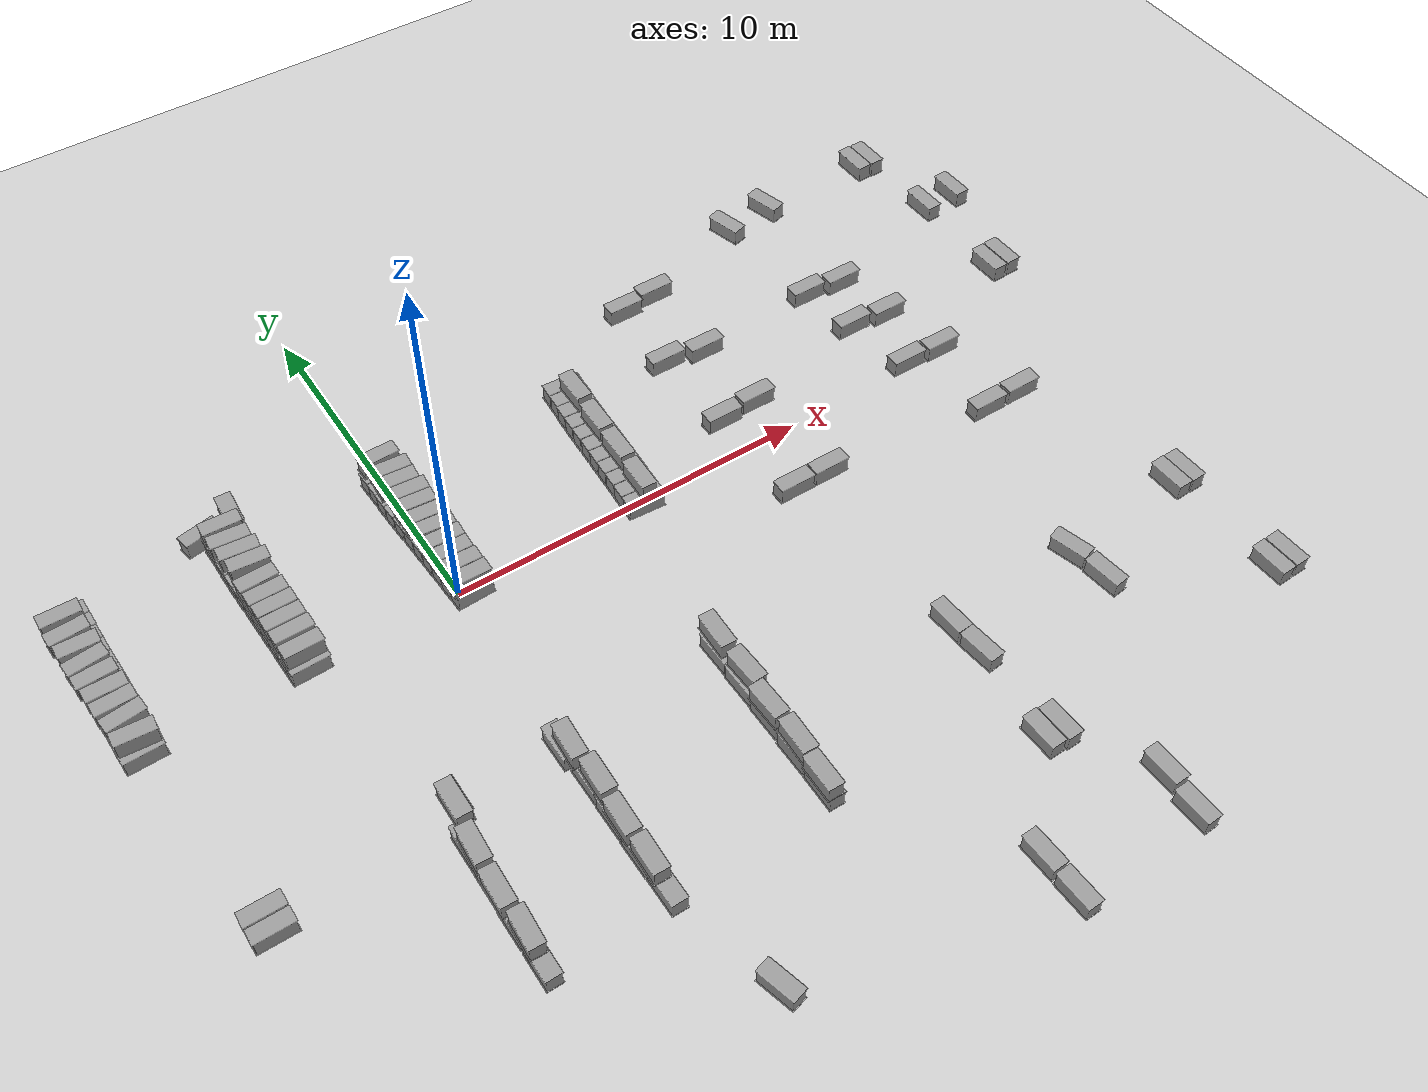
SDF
<sdf version="1.7">
 <world name="default">
  <light name="sun" type="directional">
   <pose>0 0 10 0 -0 0</pose>
   <diffuse>0.8 0.8 0.8 1</diffuse>
   <specular>0.2 0.2 0.2 1</specular>
   <attenuation>
    <range>1000</range>
    <constant>0.9</constant>
    <linear>0.01</linear>
    <quadratic>0.001</quadratic>
   </attenuation>
   <direction>-0.5 0.1 -0.9</direction>
   <spot><inner_angle>0</inner_angle><outer_angle>0</outer_angle><falloff>0</falloff></spot>
  </light>
  <model name="ground_plane">
   <static>1</static>
   <link name="link">
    <collision name="collision">
     <geometry><plane><normal>0 0 1</normal><size>100 100</size></plane></geometry>
     <surface>
      <contact><collide_bitmask>65535</collide_bitmask></contact>
      <friction><ode><mu>100</mu><mu2>50</mu2></ode></friction>
     </surface>
    </collision>
    <visual name="visual">
     <cast_shadows>0</cast_shadows>
     <geometry><plane><normal>0 0 1</normal><size>100 100</size></plane></geometry>
     <material>
      <script><uri>file://media/materials/scripts/gazebo.material</uri><name>Gazebo/Grey</name></script>
     </material>
    </visual>
   </link>
  </model>
  <gravity>0 0 -9.8</gravity>
  <magnetic_field>6e-06 2.3e-05 -4.2e-05</magnetic_field>
  <atmosphere type="adiabatic"/>
  <physics type="ode">
   <max_step_size>0.001</max_step_size>
   <real_time_factor>1</real_time_factor>
   <real_time_update_rate>1000</real_time_update_rate>
  </physics>
  <scene><ambient>0.4 0.4 0.4 1</ambient><background>0.7 0.7 0.7 1</background><shadows>1</shadows></scene>
  <spherical_coordinates>
   <surface_model>EARTH_WGS84</surface_model>
   <latitude_deg>0</latitude_deg>
   <longitude_deg>0</longitude_deg>
   <elevation>0</elevation>
   <heading_deg>0</heading_deg>
  </spherical_coordinates>
  <model name="cotton_heng">
   <model name="cotton_me">
    <link name="link_1">
     <inertial>
      <mass>1</mass>
      <inertia>
       <ixx>0.166667</ixx>
       <ixy>0</ixy>
       <ixz>0</ixz>
       <iyy>0.166667</iyy>
       <iyz>0</iyz>
       <izz>0.166667</izz>
      </inertia>
     </inertial>
     <visual name="visual">
      <geometry><mesh><uri>/home/cyun/cotton_box.stl</uri><scale>1 1 1</scale></mesh></geometry>
      <material>
       <lighting>1</lighting>
       <script><uri>file://media/materials/scripts/gazebo.material</uri><name>Gazebo/Grey</name></script>
       <shader type="pixel"/>
      </material>
     </visual>
     <collision name="collision">
      <geometry><mesh><uri>/home/cyun/cotton_box.stl</uri><scale>1 1 1</scale></mesh></geometry>
      <surface>
       <friction>
        <ode><mu>1</mu><mu2>1</mu2><fdir1>0 0 0</fdir1><slip1>0</slip1><slip2>0</slip2></ode>
        <torsional>
         <coefficient>1</coefficient>
         <patch_radius>0</patch_radius>
         <surface_radius>0</surface_radius>
         <use_patch_radius>1</use_patch_radius>
         <ode><slip>0</slip></ode>
        </torsional>
       </friction>
       <bounce><restitution_coefficient>0</restitution_coefficient><threshold>1e+06</threshold></bounce>
       <contact>
        <collide_without_contact>0</collide_without_contact>
        <collide_without_contact_bitmask>1</collide_without_contact_bitmask>
        <collide_bitmask>1</collide_bitmask>
        <ode>
         <soft_cfm>0</soft_cfm>
         <soft_erp>0.2</soft_erp>
         <kp>1e+13</kp>
         <kd>1</kd>
         <max_vel>0.01</max_vel>
         <min_depth>0</min_depth>
        </ode>
        <bullet>
         <split_impulse>1</split_impulse>
         <split_impulse_penetration_threshold>-0.01</split_impulse_penetration_threshold>
         <soft_cfm>0</soft_cfm>
         <soft_erp>0.2</soft_erp>
         <kp>1e+13</kp>
         <kd>1</kd>
        </bullet>
       </contact>
      </surface>
     </collision>
    </link>
    <static>0</static>
    <pose>-1.77996 -0.007813 0 0 -0 0</pose>
   </model>
   <model name="cotton_me_clone">
    <link name="link_1">
     <inertial>
      <mass>1</mass>
      <inertia>
       <ixx>0.166667</ixx>
       <ixy>0</ixy>
       <ixz>0</ixz>
       <iyy>0.166667</iyy>
       <iyz>0</iyz>
       <izz>0.166667</izz>
      </inertia>
     </inertial>
     <visual name="visual">
      <geometry><mesh><uri>/home/cyun/cotton_box.stl</uri><scale>1 1 1</scale></mesh></geometry>
      <material>
       <lighting>1</lighting>
       <script><uri>file://media/materials/scripts/gazebo.material</uri><name>Gazebo/Grey</name></script>
       <shader type="pixel"/>
      </material>
     </visual>
     <collision name="collision">
      <geometry><mesh><uri>/home/cyun/cotton_box.stl</uri><scale>1 1 1</scale></mesh></geometry>
      <surface>
       <friction>
        <ode><mu>1</mu><mu2>1</mu2><fdir1>0 0 0</fdir1><slip1>0</slip1><slip2>0</slip2></ode>
        <torsional>
         <coefficient>1</coefficient>
         <patch_radius>0</patch_radius>
         <surface_radius>0</surface_radius>
         <use_patch_radius>1</use_patch_radius>
         <ode><slip>0</slip></ode>
        </torsional>
       </friction>
       <bounce><restitution_coefficient>0</restitution_coefficient><threshold>1e+06</threshold></bounce>
       <contact>
        <collide_without_contact>0</collide_without_contact>
        <collide_without_contact_bitmask>1</collide_without_contact_bitmask>
        <collide_bitmask>1</collide_bitmask>
        <ode>
         <soft_cfm>0</soft_cfm>
         <soft_erp>0.2</soft_erp>
         <kp>1e+13</kp>
         <kd>1</kd>
         <max_vel>0.01</max_vel>
         <min_depth>0</min_depth>
        </ode>
        <bullet>
         <split_impulse>1</split_impulse>
         <split_impulse_penetration_threshold>-0.01</split_impulse_penetration_threshold>
         <soft_cfm>0</soft_cfm>
         <soft_erp>0.2</soft_erp>
         <kp>1e+13</kp>
         <kd>1</kd>
        </bullet>
       </contact>
      </surface>
     </collision>
    </link>
    <static>0</static>
    <pose>-1.33368 -0.009895 0 0 -0 0</pose>
   </model>
   <model name="cotton_me_clone_0">
    <link name="link_1">
     <inertial>
      <mass>1</mass>
      <inertia>
       <ixx>0.166667</ixx>
       <ixy>0</ixy>
       <ixz>0</ixz>
       <iyy>0.166667</iyy>
       <iyz>0</iyz>
       <izz>0.166667</izz>
      </inertia>
     </inertial>
     <visual name="visual">
      <geometry><mesh><uri>/home/cyun/cotton_box.stl</uri><scale>1 1 1</scale></mesh></geometry>
      <material>
       <lighting>1</lighting>
       <script><uri>file://media/materials/scripts/gazebo.material</uri><name>Gazebo/Grey</name></script>
       <shader type="pixel"/>
      </material>
     </visual>
     <collision name="collision">
      <geometry><mesh><uri>/home/cyun/cotton_box.stl</uri><scale>1 1 1</scale></mesh></geometry>
      <surface>
       <friction>
        <ode><mu>1</mu><mu2>1</mu2><fdir1>0 0 0</fdir1><slip1>0</slip1><slip2>0</slip2></ode>
        <torsional>
         <coefficient>1</coefficient>
         <patch_radius>0</patch_radius>
         <surface_radius>0</surface_radius>
         <use_patch_radius>1</use_patch_radius>
         <ode><slip>0</slip></ode>
        </torsional>
       </friction>
       <bounce><restitution_coefficient>0</restitution_coefficient><threshold>1e+06</threshold></bounce>
       <contact>
        <collide_without_contact>0</collide_without_contact>
        <collide_without_contact_bitmask>1</collide_without_contact_bitmask>
        <collide_bitmask>1</collide_bitmask>
        <ode>
         <soft_cfm>0</soft_cfm>
         <soft_erp>0.2</soft_erp>
         <kp>1e+13</kp>
         <kd>1</kd>
         <max_vel>0.01</max_vel>
         <min_depth>0</min_depth>
        </ode>
        <bullet>
         <split_impulse>1</split_impulse>
         <split_impulse_penetration_threshold>-0.01</split_impulse_penetration_threshold>
         <soft_cfm>0</soft_cfm>
         <soft_erp>0.2</soft_erp>
         <kp>1e+13</kp>
         <kd>1</kd>
        </bullet>
       </contact>
      </surface>
     </collision>
    </link>
    <static>0</static>
    <pose>-0.889452 -0.005774 0 0 -0 0</pose>
   </model>
   <model name="cotton_me_clone_1">
    <link name="link_1">
     <inertial>
      <mass>1</mass>
      <inertia>
       <ixx>0.166667</ixx>
       <ixy>0</ixy>
       <ixz>0</ixz>
       <iyy>0.166667</iyy>
       <iyz>0</iyz>
       <izz>0.166667</izz>
      </inertia>
     </inertial>
     <visual name="visual">
      <geometry><mesh><uri>/home/cyun/cotton_box.stl</uri><scale>1 1 1</scale></mesh></geometry>
      <material>
       <lighting>1</lighting>
       <script><uri>file://media/materials/scripts/gazebo.material</uri><name>Gazebo/Grey</name></script>
       <shader type="pixel"/>
      </material>
     </visual>
     <collision name="collision">
      <geometry><mesh><uri>/home/cyun/cotton_box.stl</uri><scale>1 1 1</scale></mesh></geometry>
      <surface>
       <friction>
        <ode><mu>1</mu><mu2>1</mu2><fdir1>0 0 0</fdir1><slip1>0</slip1><slip2>0</slip2></ode>
        <torsional>
         <coefficient>1</coefficient>
         <patch_radius>0</patch_radius>
         <surface_radius>0</surface_radius>
         <use_patch_radius>1</use_patch_radius>
         <ode><slip>0</slip></ode>
        </torsional>
       </friction>
       <bounce><restitution_coefficient>0</restitution_coefficient><threshold>1e+06</threshold></bounce>
       <contact>
        <collide_without_contact>0</collide_without_contact>
        <collide_without_contact_bitmask>1</collide_without_contact_bitmask>
        <collide_bitmask>1</collide_bitmask>
        <ode>
         <soft_cfm>0</soft_cfm>
         <soft_erp>0.2</soft_erp>
         <kp>1e+13</kp>
         <kd>1</kd>
         <max_vel>0.01</max_vel>
         <min_depth>0</min_depth>
        </ode>
        <bullet>
         <split_impulse>1</split_impulse>
         <split_impulse_penetration_threshold>-0.01</split_impulse_penetration_threshold>
         <soft_cfm>0</soft_cfm>
         <soft_erp>0.2</soft_erp>
         <kp>1e+13</kp>
         <kd>1</kd>
        </bullet>
       </contact>
      </surface>
     </collision>
    </link>
    <static>0</static>
    <pose>-0.445737 -0.001627 0 0 -0 0</pose>
   </model>
   <model name="cotton_me_clone_2">
    <link name="link_1">
     <inertial>
      <mass>1</mass>
      <inertia>
       <ixx>0.166667</ixx>
       <ixy>0</ixy>
       <ixz>0</ixz>
       <iyy>0.166667</iyy>
       <iyz>0</iyz>
       <izz>0.166667</izz>
      </inertia>
     </inertial>
     <visual name="visual">
      <geometry><mesh><uri>/home/cyun/cotton_box.stl</uri><scale>1 1 1</scale></mesh></geometry>
      <material>
       <lighting>1</lighting>
       <script><uri>file://media/materials/scripts/gazebo.material</uri><name>Gazebo/Grey</name></script>
       <shader type="pixel"/>
      </material>
     </visual>
     <collision name="collision">
      <geometry><mesh><uri>/home/cyun/cotton_box.stl</uri><scale>1 1 1</scale></mesh></geometry>
      <surface>
       <friction>
        <ode><mu>1</mu><mu2>1</mu2><fdir1>0 0 0</fdir1><slip1>0</slip1><slip2>0</slip2></ode>
        <torsional>
         <coefficient>1</coefficient>
         <patch_radius>0</patch_radius>
         <surface_radius>0</surface_radius>
         <use_patch_radius>1</use_patch_radius>
         <ode><slip>0</slip></ode>
        </torsional>
       </friction>
       <bounce><restitution_coefficient>0</restitution_coefficient><threshold>1e+06</threshold></bounce>
       <contact>
        <collide_without_contact>0</collide_without_contact>
        <collide_without_contact_bitmask>1</collide_without_contact_bitmask>
        <collide_bitmask>1</collide_bitmask>
        <ode>
         <soft_cfm>0</soft_cfm>
         <soft_erp>0.2</soft_erp>
         <kp>1e+13</kp>
         <kd>1</kd>
         <max_vel>0.01</max_vel>
         <min_depth>0</min_depth>
        </ode>
        <bullet>
         <split_impulse>1</split_impulse>
         <split_impulse_penetration_threshold>-0.01</split_impulse_penetration_threshold>
         <soft_cfm>0</soft_cfm>
         <soft_erp>0.2</soft_erp>
         <kp>1e+13</kp>
         <kd>1</kd>
        </bullet>
       </contact>
      </surface>
     </collision>
    </link>
    <static>0</static>
    <pose>0.001194 0.000886 0 0 -0 0</pose>
   </model>
   <model name="cotton_me_clone_3">
    <link name="link_1">
     <inertial>
      <mass>1</mass>
      <inertia>
       <ixx>0.166667</ixx>
       <ixy>0</ixy>
       <ixz>0</ixz>
       <iyy>0.166667</iyy>
       <iyz>0</iyz>
       <izz>0.166667</izz>
      </inertia>
     </inertial>
     <visual name="visual">
      <geometry><mesh><uri>/home/cyun/cotton_box.stl</uri><scale>1 1 1</scale></mesh></geometry>
      <material>
       <lighting>1</lighting>
       <script><uri>file://media/materials/scripts/gazebo.material</uri><name>Gazebo/Grey</name></script>
       <shader type="pixel"/>
      </material>
     </visual>
     <collision name="collision">
      <geometry><mesh><uri>/home/cyun/cotton_box.stl</uri><scale>1 1 1</scale></mesh></geometry>
      <surface>
       <friction>
        <ode><mu>1</mu><mu2>1</mu2><fdir1>0 0 0</fdir1><slip1>0</slip1><slip2>0</slip2></ode>
        <torsional>
         <coefficient>1</coefficient>
         <patch_radius>0</patch_radius>
         <surface_radius>0</surface_radius>
         <use_patch_radius>1</use_patch_radius>
         <ode><slip>0</slip></ode>
        </torsional>
       </friction>
       <bounce><restitution_coefficient>0</restitution_coefficient><threshold>1e+06</threshold></bounce>
       <contact>
        <collide_without_contact>0</collide_without_contact>
        <collide_without_contact_bitmask>1</collide_without_contact_bitmask>
        <collide_bitmask>1</collide_bitmask>
        <ode>
         <soft_cfm>0</soft_cfm>
         <soft_erp>0.2</soft_erp>
         <kp>1e+13</kp>
         <kd>1</kd>
         <max_vel>0.01</max_vel>
         <min_depth>0</min_depth>
        </ode>
        <bullet>
         <split_impulse>1</split_impulse>
         <split_impulse_penetration_threshold>-0.01</split_impulse_penetration_threshold>
         <soft_cfm>0</soft_cfm>
         <soft_erp>0.2</soft_erp>
         <kp>1e+13</kp>
         <kd>1</kd>
        </bullet>
       </contact>
      </surface>
     </collision>
    </link>
    <static>0</static>
    <pose>0.448503 0.010252 0 0 -0 0</pose>
   </model>
   <model name="cotton_me_clone_4">
    <link name="link_1">
     <inertial>
      <mass>1</mass>
      <inertia>
       <ixx>0.166667</ixx>
       <ixy>0</ixy>
       <ixz>0</ixz>
       <iyy>0.166667</iyy>
       <iyz>0</iyz>
       <izz>0.166667</izz>
      </inertia>
     </inertial>
     <visual name="visual">
      <geometry><mesh><uri>/home/cyun/cotton_box.stl</uri><scale>1 1 1</scale></mesh></geometry>
      <material>
       <lighting>1</lighting>
       <script><uri>file://media/materials/scripts/gazebo.material</uri><name>Gazebo/Grey</name></script>
       <shader type="pixel"/>
      </material>
     </visual>
     <collision name="collision">
      <geometry><mesh><uri>/home/cyun/cotton_box.stl</uri><scale>1 1 1</scale></mesh></geometry>
      <surface>
       <friction>
        <ode><mu>1</mu><mu2>1</mu2><fdir1>0 0 0</fdir1><slip1>0</slip1><slip2>0</slip2></ode>
        <torsional>
         <coefficient>1</coefficient>
         <patch_radius>0</patch_radius>
         <surface_radius>0</surface_radius>
         <use_patch_radius>1</use_patch_radius>
         <ode><slip>0</slip></ode>
        </torsional>
       </friction>
       <bounce><restitution_coefficient>0</restitution_coefficient><threshold>1e+06</threshold></bounce>
       <contact>
        <collide_without_contact>0</collide_without_contact>
        <collide_without_contact_bitmask>1</collide_without_contact_bitmask>
        <collide_bitmask>1</collide_bitmask>
        <ode>
         <soft_cfm>0</soft_cfm>
         <soft_erp>0.2</soft_erp>
         <kp>1e+13</kp>
         <kd>1</kd>
         <max_vel>0.01</max_vel>
         <min_depth>0</min_depth>
        </ode>
        <bullet>
         <split_impulse>1</split_impulse>
         <split_impulse_penetration_threshold>-0.01</split_impulse_penetration_threshold>
         <soft_cfm>0</soft_cfm>
         <soft_erp>0.2</soft_erp>
         <kp>1e+13</kp>
         <kd>1</kd>
        </bullet>
       </contact>
      </surface>
     </collision>
    </link>
    <static>0</static>
    <pose>0.894659 0.014624 0 0 -0 0</pose>
   </model>
   <model name="cotton_me_clone_5">
    <link name="link_1">
     <inertial>
      <mass>1</mass>
      <inertia>
       <ixx>0.166667</ixx>
       <ixy>0</ixy>
       <ixz>0</ixz>
       <iyy>0.166667</iyy>
       <iyz>0</iyz>
       <izz>0.166667</izz>
      </inertia>
     </inertial>
     <visual name="visual">
      <geometry><mesh><uri>/home/cyun/cotton_box.stl</uri><scale>1 1 1</scale></mesh></geometry>
      <material>
       <lighting>1</lighting>
       <script><uri>file://media/materials/scripts/gazebo.material</uri><name>Gazebo/Grey</name></script>
       <shader type="pixel"/>
      </material>
     </visual>
     <collision name="collision">
      <geometry><mesh><uri>/home/cyun/cotton_box.stl</uri><scale>1 1 1</scale></mesh></geometry>
      <surface>
       <friction>
        <ode><mu>1</mu><mu2>1</mu2><fdir1>0 0 0</fdir1><slip1>0</slip1><slip2>0</slip2></ode>
        <torsional>
         <coefficient>1</coefficient>
         <patch_radius>0</patch_radius>
         <surface_radius>0</surface_radius>
         <use_patch_radius>1</use_patch_radius>
         <ode><slip>0</slip></ode>
        </torsional>
       </friction>
       <bounce><restitution_coefficient>0</restitution_coefficient><threshold>1e+06</threshold></bounce>
       <contact>
        <collide_without_contact>0</collide_without_contact>
        <collide_without_contact_bitmask>1</collide_without_contact_bitmask>
        <collide_bitmask>1</collide_bitmask>
        <ode>
         <soft_cfm>0</soft_cfm>
         <soft_erp>0.2</soft_erp>
         <kp>1e+13</kp>
         <kd>1</kd>
         <max_vel>0.01</max_vel>
         <min_depth>0</min_depth>
        </ode>
        <bullet>
         <split_impulse>1</split_impulse>
         <split_impulse_penetration_threshold>-0.01</split_impulse_penetration_threshold>
         <soft_cfm>0</soft_cfm>
         <soft_erp>0.2</soft_erp>
         <kp>1e+13</kp>
         <kd>1</kd>
        </bullet>
       </contact>
      </surface>
     </collision>
    </link>
    <static>0</static>
    <pose>1.33945 0.013464 0 0 -0 0</pose>
   </model>
   <model name="cotton_me_clone_6">
    <link name="link_1">
     <inertial>
      <mass>1</mass>
      <inertia>
       <ixx>0.166667</ixx>
       <ixy>0</ixy>
       <ixz>0</ixz>
       <iyy>0.166667</iyy>
       <iyz>0</iyz>
       <izz>0.166667</izz>
      </inertia>
     </inertial>
     <visual name="visual">
      <geometry><mesh><uri>/home/cyun/cotton_box.stl</uri><scale>1 1 1</scale></mesh></geometry>
      <material>
       <lighting>1</lighting>
       <script><uri>file://media/materials/scripts/gazebo.material</uri><name>Gazebo/Grey</name></script>
       <shader type="pixel"/>
      </material>
     </visual>
     <collision name="collision">
      <geometry><mesh><uri>/home/cyun/cotton_box.stl</uri><scale>1 1 1</scale></mesh></geometry>
      <surface>
       <friction>
        <ode><mu>1</mu><mu2>1</mu2><fdir1>0 0 0</fdir1><slip1>0</slip1><slip2>0</slip2></ode>
        <torsional>
         <coefficient>1</coefficient>
         <patch_radius>0</patch_radius>
         <surface_radius>0</surface_radius>
         <use_patch_radius>1</use_patch_radius>
         <ode><slip>0</slip></ode>
        </torsional>
       </friction>
       <bounce><restitution_coefficient>0</restitution_coefficient><threshold>1e+06</threshold></bounce>
       <contact>
        <collide_without_contact>0</collide_without_contact>
        <collide_without_contact_bitmask>1</collide_without_contact_bitmask>
        <collide_bitmask>1</collide_bitmask>
        <ode>
         <soft_cfm>0</soft_cfm>
         <soft_erp>0.2</soft_erp>
         <kp>1e+13</kp>
         <kd>1</kd>
         <max_vel>0.01</max_vel>
         <min_depth>0</min_depth>
        </ode>
        <bullet>
         <split_impulse>1</split_impulse>
         <split_impulse_penetration_threshold>-0.01</split_impulse_penetration_threshold>
         <soft_cfm>0</soft_cfm>
         <soft_erp>0.2</soft_erp>
         <kp>1e+13</kp>
         <kd>1</kd>
        </bullet>
       </contact>
      </surface>
     </collision>
    </link>
    <static>0</static>
    <pose>1.77292 -0.000762 0 0 -0 0</pose>
   </model>
   <model name="cotton_me_clone_7">
    <link name="link_1">
     <inertial>
      <mass>1</mass>
      <inertia>
       <ixx>0.166667</ixx>
       <ixy>0</ixy>
       <ixz>0</ixz>
       <iyy>0.166667</iyy>
       <iyz>0</iyz>
       <izz>0.166667</izz>
      </inertia>
     </inertial>
     <visual name="visual">
      <geometry><mesh><uri>/home/cyun/cotton_box.stl</uri><scale>1 1 1</scale></mesh></geometry>
      <material>
       <lighting>1</lighting>
       <script><uri>file://media/materials/scripts/gazebo.material</uri><name>Gazebo/Grey</name></script>
       <shader type="pixel"/>
      </material>
     </visual>
     <collision name="collision">
      <geometry><mesh><uri>/home/cyun/cotton_box.stl</uri><scale>1 1 1</scale></mesh></geometry>
      <surface>
       <friction>
        <ode><mu>1</mu><mu2>1</mu2><fdir1>0 0 0</fdir1><slip1>0</slip1><slip2>0</slip2></ode>
        <torsional>
         <coefficient>1</coefficient>
         <patch_radius>0</patch_radius>
         <surface_radius>0</surface_radius>
         <use_patch_radius>1</use_patch_radius>
         <ode><slip>0</slip></ode>
        </torsional>
       </friction>
       <bounce><restitution_coefficient>0</restitution_coefficient><threshold>1e+06</threshold></bounce>
       <contact>
        <collide_without_contact>0</collide_without_contact>
        <collide_without_contact_bitmask>1</collide_without_contact_bitmask>
        <collide_bitmask>1</collide_bitmask>
        <ode>
         <soft_cfm>0</soft_cfm>
         <soft_erp>0.2</soft_erp>
         <kp>1e+13</kp>
         <kd>1</kd>
         <max_vel>0.01</max_vel>
         <min_depth>0</min_depth>
        </ode>
        <bullet>
         <split_impulse>1</split_impulse>
         <split_impulse_penetration_threshold>-0.01</split_impulse_penetration_threshold>
         <soft_cfm>0</soft_cfm>
         <soft_erp>0.2</soft_erp>
         <kp>1e+13</kp>
         <kd>1</kd>
        </bullet>
       </contact>
      </surface>
     </collision>
    </link>
    <static>0</static>
    <pose>2.21576 -0.001881 0 0 -0 0</pose>
   </model>
   <model name="cotton_me_clone_8">
    <link name="link_1">
     <inertial>
      <mass>1</mass>
      <inertia>
       <ixx>0.166667</ixx>
       <ixy>0</ixy>
       <ixz>0</ixz>
       <iyy>0.166667</iyy>
       <iyz>0</iyz>
       <izz>0.166667</izz>
      </inertia>
     </inertial>
     <visual name="visual">
      <geometry><mesh><uri>/home/cyun/cotton_box.stl</uri><scale>1 1 1</scale></mesh></geometry>
      <material>
       <lighting>1</lighting>
       <script><uri>file://media/materials/scripts/gazebo.material</uri><name>Gazebo/Grey</name></script>
       <shader type="pixel"/>
      </material>
     </visual>
     <collision name="collision">
      <geometry><mesh><uri>/home/cyun/cotton_box.stl</uri><scale>1 1 1</scale></mesh></geometry>
      <surface>
       <friction>
        <ode><mu>1</mu><mu2>1</mu2><fdir1>0 0 0</fdir1><slip1>0</slip1><slip2>0</slip2></ode>
        <torsional>
         <coefficient>1</coefficient>
         <patch_radius>0</patch_radius>
         <surface_radius>0</surface_radius>
         <use_patch_radius>1</use_patch_radius>
         <ode><slip>0</slip></ode>
        </torsional>
       </friction>
       <bounce><restitution_coefficient>0</restitution_coefficient><threshold>1e+06</threshold></bounce>
       <contact>
        <collide_without_contact>0</collide_without_contact>
        <collide_without_contact_bitmask>1</collide_without_contact_bitmask>
        <collide_bitmask>1</collide_bitmask>
        <ode>
         <soft_cfm>0</soft_cfm>
         <soft_erp>0.2</soft_erp>
         <kp>1e+13</kp>
         <kd>1</kd>
         <max_vel>0.01</max_vel>
         <min_depth>0</min_depth>
        </ode>
        <bullet>
         <split_impulse>1</split_impulse>
         <split_impulse_penetration_threshold>-0.01</split_impulse_penetration_threshold>
         <soft_cfm>0</soft_cfm>
         <soft_erp>0.2</soft_erp>
         <kp>1e+13</kp>
         <kd>1</kd>
        </bullet>
       </contact>
      </surface>
     </collision>
    </link>
    <static>0</static>
    <pose>-2.22367 -0.011477 0 0 -0 0</pose>
   </model>
   <static>0</static>
   <pose>-8.18289 2.03525 0.01999 -1e-06 -0 1.59641</pose>
  </model>
  <model name="cotton_heng_clone">
   <model name="cotton_me">
    <link name="link_1">
     <inertial>
      <mass>1</mass>
      <inertia>
       <ixx>0.166667</ixx>
       <ixy>0</ixy>
       <ixz>0</ixz>
       <iyy>0.166667</iyy>
       <iyz>0</iyz>
       <izz>0.166667</izz>
      </inertia>
     </inertial>
     <visual name="visual">
      <geometry><mesh><uri>/home/cyun/cotton_box.stl</uri><scale>1 1 1</scale></mesh></geometry>
      <material>
       <lighting>1</lighting>
       <script><uri>file://media/materials/scripts/gazebo.material</uri><name>Gazebo/Grey</name></script>
       <shader type="pixel"/>
      </material>
     </visual>
     <collision name="collision">
      <geometry><mesh><uri>/home/cyun/cotton_box.stl</uri><scale>1 1 1</scale></mesh></geometry>
      <surface>
       <friction>
        <ode><mu>1</mu><mu2>1</mu2><fdir1>0 0 0</fdir1><slip1>0</slip1><slip2>0</slip2></ode>
        <torsional>
         <coefficient>1</coefficient>
         <patch_radius>0</patch_radius>
         <surface_radius>0</surface_radius>
         <use_patch_radius>1</use_patch_radius>
         <ode><slip>0</slip></ode>
        </torsional>
       </friction>
       <bounce><restitution_coefficient>0</restitution_coefficient><threshold>1e+06</threshold></bounce>
       <contact>
        <collide_without_contact>0</collide_without_contact>
        <collide_without_contact_bitmask>1</collide_without_contact_bitmask>
        <collide_bitmask>1</collide_bitmask>
        <ode>
         <soft_cfm>0</soft_cfm>
         <soft_erp>0.2</soft_erp>
         <kp>1e+13</kp>
         <kd>1</kd>
         <max_vel>0.01</max_vel>
         <min_depth>0</min_depth>
        </ode>
        <bullet>
         <split_impulse>1</split_impulse>
         <split_impulse_penetration_threshold>-0.01</split_impulse_penetration_threshold>
         <soft_cfm>0</soft_cfm>
         <soft_erp>0.2</soft_erp>
         <kp>1e+13</kp>
         <kd>1</kd>
        </bullet>
       </contact>
      </surface>
     </collision>
    </link>
    <static>0</static>
    <pose>-1.77996 -0.007813 0 0 -0 0</pose>
   </model>
   <model name="cotton_me_clone">
    <link name="link_1">
     <inertial>
      <mass>1</mass>
      <inertia>
       <ixx>0.166667</ixx>
       <ixy>0</ixy>
       <ixz>0</ixz>
       <iyy>0.166667</iyy>
       <iyz>0</iyz>
       <izz>0.166667</izz>
      </inertia>
     </inertial>
     <visual name="visual">
      <geometry><mesh><uri>/home/cyun/cotton_box.stl</uri><scale>1 1 1</scale></mesh></geometry>
      <material>
       <lighting>1</lighting>
       <script><uri>file://media/materials/scripts/gazebo.material</uri><name>Gazebo/Grey</name></script>
       <shader type="pixel"/>
      </material>
     </visual>
     <collision name="collision">
      <geometry><mesh><uri>/home/cyun/cotton_box.stl</uri><scale>1 1 1</scale></mesh></geometry>
      <surface>
       <friction>
        <ode><mu>1</mu><mu2>1</mu2><fdir1>0 0 0</fdir1><slip1>0</slip1><slip2>0</slip2></ode>
        <torsional>
         <coefficient>1</coefficient>
         <patch_radius>0</patch_radius>
         <surface_radius>0</surface_radius>
         <use_patch_radius>1</use_patch_radius>
         <ode><slip>0</slip></ode>
        </torsional>
       </friction>
       <bounce><restitution_coefficient>0</restitution_coefficient><threshold>1e+06</threshold></bounce>
       <contact>
        <collide_without_contact>0</collide_without_contact>
        <collide_without_contact_bitmask>1</collide_without_contact_bitmask>
        <collide_bitmask>1</collide_bitmask>
        <ode>
         <soft_cfm>0</soft_cfm>
         <soft_erp>0.2</soft_erp>
         <kp>1e+13</kp>
         <kd>1</kd>
         <max_vel>0.01</max_vel>
         <min_depth>0</min_depth>
        </ode>
        <bullet>
         <split_impulse>1</split_impulse>
         <split_impulse_penetration_threshold>-0.01</split_impulse_penetration_threshold>
         <soft_cfm>0</soft_cfm>
         <soft_erp>0.2</soft_erp>
         <kp>1e+13</kp>
         <kd>1</kd>
        </bullet>
       </contact>
      </surface>
     </collision>
    </link>
    <static>0</static>
    <pose>-1.33368 -0.009895 0 0 -0 0</pose>
   </model>
   <model name="cotton_me_clone_0">
    <link name="link_1">
     <inertial>
      <mass>1</mass>
      <inertia>
       <ixx>0.166667</ixx>
       <ixy>0</ixy>
       <ixz>0</ixz>
       <iyy>0.166667</iyy>
       <iyz>0</iyz>
       <izz>0.166667</izz>
      </inertia>
     </inertial>
     <visual name="visual">
      <geometry><mesh><uri>/home/cyun/cotton_box.stl</uri><scale>1 1 1</scale></mesh></geometry>
      <material>
       <lighting>1</lighting>
       <script><uri>file://media/materials/scripts/gazebo.material</uri><name>Gazebo/Grey</name></script>
       <shader type="pixel"/>
      </material>
     </visual>
     <collision name="collision">
      <geometry><mesh><uri>/home/cyun/cotton_box.stl</uri><scale>1 1 1</scale></mesh></geometry>
      <surface>
       <friction>
        <ode><mu>1</mu><mu2>1</mu2><fdir1>0 0 0</fdir1><slip1>0</slip1><slip2>0</slip2></ode>
        <torsional>
         <coefficient>1</coefficient>
         <patch_radius>0</patch_radius>
         <surface_radius>0</surface_radius>
         <use_patch_radius>1</use_patch_radius>
         <ode><slip>0</slip></ode>
        </torsional>
       </friction>
       <bounce><restitution_coefficient>0</restitution_coefficient><threshold>1e+06</threshold></bounce>
       <contact>
        <collide_without_contact>0</collide_without_contact>
        <collide_without_contact_bitmask>1</collide_without_contact_bitmask>
        <collide_bitmask>1</collide_bitmask>
        <ode>
         <soft_cfm>0</soft_cfm>
         <soft_erp>0.2</soft_erp>
         <kp>1e+13</kp>
         <kd>1</kd>
         <max_vel>0.01</max_vel>
         <min_depth>0</min_depth>
        </ode>
        <bullet>
         <split_impulse>1</split_impulse>
         <split_impulse_penetration_threshold>-0.01</split_impulse_penetration_threshold>
         <soft_cfm>0</soft_cfm>
         <soft_erp>0.2</soft_erp>
         <kp>1e+13</kp>
         <kd>1</kd>
        </bullet>
       </contact>
      </surface>
     </collision>
    </link>
    <static>0</static>
    <pose>-0.889452 -0.005774 0 0 -0 0</pose>
   </model>
   <model name="cotton_me_clone_1">
    <link name="link_1">
     <inertial>
      <mass>1</mass>
      <inertia>
       <ixx>0.166667</ixx>
       <ixy>0</ixy>
       <ixz>0</ixz>
       <iyy>0.166667</iyy>
       <iyz>0</iyz>
       <izz>0.166667</izz>
      </inertia>
     </inertial>
     <visual name="visual">
      <geometry><mesh><uri>/home/cyun/cotton_box.stl</uri><scale>1 1 1</scale></mesh></geometry>
      <material>
       <lighting>1</lighting>
       <script><uri>file://media/materials/scripts/gazebo.material</uri><name>Gazebo/Grey</name></script>
       <shader type="pixel"/>
      </material>
     </visual>
     <collision name="collision">
      <geometry><mesh><uri>/home/cyun/cotton_box.stl</uri><scale>1 1 1</scale></mesh></geometry>
      <surface>
       <friction>
        <ode><mu>1</mu><mu2>1</mu2><fdir1>0 0 0</fdir1><slip1>0</slip1><slip2>0</slip2></ode>
        <torsional>
         <coefficient>1</coefficient>
         <patch_radius>0</patch_radius>
         <surface_radius>0</surface_radius>
         <use_patch_radius>1</use_patch_radius>
         <ode><slip>0</slip></ode>
        </torsional>
       </friction>
       <bounce><restitution_coefficient>0</restitution_coefficient><threshold>1e+06</threshold></bounce>
       <contact>
        <collide_without_contact>0</collide_without_contact>
        <collide_without_contact_bitmask>1</collide_without_contact_bitmask>
        <collide_bitmask>1</collide_bitmask>
        <ode>
         <soft_cfm>0</soft_cfm>
         <soft_erp>0.2</soft_erp>
         <kp>1e+13</kp>
         <kd>1</kd>
         <max_vel>0.01</max_vel>
         <min_depth>0</min_depth>
        </ode>
        <bullet>
         <split_impulse>1</split_impulse>
         <split_impulse_penetration_threshold>-0.01</split_impulse_penetration_threshold>
         <soft_cfm>0</soft_cfm>
         <soft_erp>0.2</soft_erp>
         <kp>1e+13</kp>
         <kd>1</kd>
        </bullet>
       </contact>
      </surface>
     </collision>
    </link>
    <static>0</static>
    <pose>-0.445737 -0.001627 0 0 -0 0</pose>
   </model>
   <model name="cotton_me_clone_2">
    <link name="link_1">
     <inertial>
      <mass>1</mass>
      <inertia>
       <ixx>0.166667</ixx>
       <ixy>0</ixy>
       <ixz>0</ixz>
       <iyy>0.166667</iyy>
       <iyz>0</iyz>
       <izz>0.166667</izz>
      </inertia>
     </inertial>
     <visual name="visual">
      <geometry><mesh><uri>/home/cyun/cotton_box.stl</uri><scale>1 1 1</scale></mesh></geometry>
      <material>
       <lighting>1</lighting>
       <script><uri>file://media/materials/scripts/gazebo.material</uri><name>Gazebo/Grey</name></script>
       <shader type="pixel"/>
      </material>
     </visual>
     <collision name="collision">
      <geometry><mesh><uri>/home/cyun/cotton_box.stl</uri><scale>1 1 1</scale></mesh></geometry>
      <surface>
       <friction>
        <ode><mu>1</mu><mu2>1</mu2><fdir1>0 0 0</fdir1><slip1>0</slip1><slip2>0</slip2></ode>
        <torsional>
         <coefficient>1</coefficient>
         <patch_radius>0</patch_radius>
         <surface_radius>0</surface_radius>
         <use_patch_radius>1</use_patch_radius>
         <ode><slip>0</slip></ode>
        </torsional>
       </friction>
       <bounce><restitution_coefficient>0</restitution_coefficient><threshold>1e+06</threshold></bounce>
       <contact>
        <collide_without_contact>0</collide_without_contact>
        <collide_without_contact_bitmask>1</collide_without_contact_bitmask>
        <collide_bitmask>1</collide_bitmask>
        <ode>
         <soft_cfm>0</soft_cfm>
         <soft_erp>0.2</soft_erp>
         <kp>1e+13</kp>
         <kd>1</kd>
         <max_vel>0.01</max_vel>
         <min_depth>0</min_depth>
        </ode>
        <bullet>
         <split_impulse>1</split_impulse>
         <split_impulse_penetration_threshold>-0.01</split_impulse_penetration_threshold>
         <soft_cfm>0</soft_cfm>
         <soft_erp>0.2</soft_erp>
         <kp>1e+13</kp>
         <kd>1</kd>
        </bullet>
       </contact>
      </surface>
     </collision>
    </link>
    <static>0</static>
    <pose>0.001194 0.000886 0 0 -0 0</pose>
   </model>
   <model name="cotton_me_clone_3">
    <link name="link_1">
     <inertial>
      <mass>1</mass>
      <inertia>
       <ixx>0.166667</ixx>
       <ixy>0</ixy>
       <ixz>0</ixz>
       <iyy>0.166667</iyy>
       <iyz>0</iyz>
       <izz>0.166667</izz>
      </inertia>
     </inertial>
     <visual name="visual">
      <geometry><mesh><uri>/home/cyun/cotton_box.stl</uri><scale>1 1 1</scale></mesh></geometry>
      <material>
       <lighting>1</lighting>
       <script><uri>file://media/materials/scripts/gazebo.material</uri><name>Gazebo/Grey</name></script>
       <shader type="pixel"/>
      </material>
     </visual>
     <collision name="collision">
      <geometry><mesh><uri>/home/cyun/cotton_box.stl</uri><scale>1 1 1</scale></mesh></geometry>
      <surface>
       <friction>
        <ode><mu>1</mu><mu2>1</mu2><fdir1>0 0 0</fdir1><slip1>0</slip1><slip2>0</slip2></ode>
        <torsional>
         <coefficient>1</coefficient>
         <patch_radius>0</patch_radius>
         <surface_radius>0</surface_radius>
         <use_patch_radius>1</use_patch_radius>
         <ode><slip>0</slip></ode>
        </torsional>
       </friction>
       <bounce><restitution_coefficient>0</restitution_coefficient><threshold>1e+06</threshold></bounce>
       <contact>
        <collide_without_contact>0</collide_without_contact>
        <collide_without_contact_bitmask>1</collide_without_contact_bitmask>
        <collide_bitmask>1</collide_bitmask>
        <ode>
         <soft_cfm>0</soft_cfm>
         <soft_erp>0.2</soft_erp>
         <kp>1e+13</kp>
         <kd>1</kd>
         <max_vel>0.01</max_vel>
         <min_depth>0</min_depth>
        </ode>
        <bullet>
         <split_impulse>1</split_impulse>
         <split_impulse_penetration_threshold>-0.01</split_impulse_penetration_threshold>
         <soft_cfm>0</soft_cfm>
         <soft_erp>0.2</soft_erp>
         <kp>1e+13</kp>
         <kd>1</kd>
        </bullet>
       </contact>
      </surface>
     </collision>
    </link>
    <static>0</static>
    <pose>0.448503 0.010252 0 0 -0 0</pose>
   </model>
   <model name="cotton_me_clone_4">
    <link name="link_1">
     <inertial>
      <mass>1</mass>
      <inertia>
       <ixx>0.166667</ixx>
       <ixy>0</ixy>
       <ixz>0</ixz>
       <iyy>0.166667</iyy>
       <iyz>0</iyz>
       <izz>0.166667</izz>
      </inertia>
     </inertial>
     <visual name="visual">
      <geometry><mesh><uri>/home/cyun/cotton_box.stl</uri><scale>1 1 1</scale></mesh></geometry>
      <material>
       <lighting>1</lighting>
       <script><uri>file://media/materials/scripts/gazebo.material</uri><name>Gazebo/Grey</name></script>
       <shader type="pixel"/>
      </material>
     </visual>
     <collision name="collision">
      <geometry><mesh><uri>/home/cyun/cotton_box.stl</uri><scale>1 1 1</scale></mesh></geometry>
      <surface>
       <friction>
        <ode><mu>1</mu><mu2>1</mu2><fdir1>0 0 0</fdir1><slip1>0</slip1><slip2>0</slip2></ode>
        <torsional>
         <coefficient>1</coefficient>
         <patch_radius>0</patch_radius>
         <surface_radius>0</surface_radius>
         <use_patch_radius>1</use_patch_radius>
         <ode><slip>0</slip></ode>
        </torsional>
       </friction>
       <bounce><restitution_coefficient>0</restitution_coefficient><threshold>1e+06</threshold></bounce>
       <contact>
        <collide_without_contact>0</collide_without_contact>
        <collide_without_contact_bitmask>1</collide_without_contact_bitmask>
        <collide_bitmask>1</collide_bitmask>
        <ode>
         <soft_cfm>0</soft_cfm>
         <soft_erp>0.2</soft_erp>
         <kp>1e+13</kp>
         <kd>1</kd>
         <max_vel>0.01</max_vel>
         <min_depth>0</min_depth>
        </ode>
        <bullet>
         <split_impulse>1</split_impulse>
         <split_impulse_penetration_threshold>-0.01</split_impulse_penetration_threshold>
         <soft_cfm>0</soft_cfm>
         <soft_erp>0.2</soft_erp>
         <kp>1e+13</kp>
         <kd>1</kd>
        </bullet>
       </contact>
      </surface>
     </collision>
    </link>
    <static>0</static>
    <pose>0.894659 0.014624 0 0 -0 0</pose>
   </model>
   <model name="cotton_me_clone_5">
    <link name="link_1">
     <inertial>
      <mass>1</mass>
      <inertia>
       <ixx>0.166667</ixx>
       <ixy>0</ixy>
       <ixz>0</ixz>
       <iyy>0.166667</iyy>
       <iyz>0</iyz>
       <izz>0.166667</izz>
      </inertia>
     </inertial>
     <visual name="visual">
      <geometry><mesh><uri>/home/cyun/cotton_box.stl</uri><scale>1 1 1</scale></mesh></geometry>
      <material>
       <lighting>1</lighting>
       <script><uri>file://media/materials/scripts/gazebo.material</uri><name>Gazebo/Grey</name></script>
       <shader type="pixel"/>
      </material>
     </visual>
     <collision name="collision">
      <geometry><mesh><uri>/home/cyun/cotton_box.stl</uri><scale>1 1 1</scale></mesh></geometry>
      <surface>
       <friction>
        <ode><mu>1</mu><mu2>1</mu2><fdir1>0 0 0</fdir1><slip1>0</slip1><slip2>0</slip2></ode>
        <torsional>
         <coefficient>1</coefficient>
         <patch_radius>0</patch_radius>
         <surface_radius>0</surface_radius>
         <use_patch_radius>1</use_patch_radius>
         <ode><slip>0</slip></ode>
        </torsional>
       </friction>
       <bounce><restitution_coefficient>0</restitution_coefficient><threshold>1e+06</threshold></bounce>
       <contact>
        <collide_without_contact>0</collide_without_contact>
        <collide_without_contact_bitmask>1</collide_without_contact_bitmask>
        <collide_bitmask>1</collide_bitmask>
        <ode>
         <soft_cfm>0</soft_cfm>
         <soft_erp>0.2</soft_erp>
         <kp>1e+13</kp>
         <kd>1</kd>
         <max_vel>0.01</max_vel>
         <min_depth>0</min_depth>
        </ode>
        <bullet>
         <split_impulse>1</split_impulse>
         <split_impulse_penetration_threshold>-0.01</split_impulse_penetration_threshold>
         <soft_cfm>0</soft_cfm>
         <soft_erp>0.2</soft_erp>
         <kp>1e+13</kp>
         <kd>1</kd>
        </bullet>
       </contact>
      </surface>
     </collision>
    </link>
    <static>0</static>
    <pose>1.33945 0.013464 0 0 -0 0</pose>
   </model>
   <model name="cotton_me_clone_6">
    <link name="link_1">
     <inertial>
      <mass>1</mass>
      <inertia>
       <ixx>0.166667</ixx>
       <ixy>0</ixy>
       <ixz>0</ixz>
       <iyy>0.166667</iyy>
       <iyz>0</iyz>
       <izz>0.166667</izz>
      </inertia>
     </inertial>
     <visual name="visual">
      <geometry><mesh><uri>/home/cyun/cotton_box.stl</uri><scale>1 1 1</scale></mesh></geometry>
      <material>
       <lighting>1</lighting>
       <script><uri>file://media/materials/scripts/gazebo.material</uri><name>Gazebo/Grey</name></script>
       <shader type="pixel"/>
      </material>
     </visual>
     <collision name="collision">
      <geometry><mesh><uri>/home/cyun/cotton_box.stl</uri><scale>1 1 1</scale></mesh></geometry>
      <surface>
       <friction>
        <ode><mu>1</mu><mu2>1</mu2><fdir1>0 0 0</fdir1><slip1>0</slip1><slip2>0</slip2></ode>
        <torsional>
         <coefficient>1</coefficient>
         <patch_radius>0</patch_radius>
         <surface_radius>0</surface_radius>
         <use_patch_radius>1</use_patch_radius>
         <ode><slip>0</slip></ode>
        </torsional>
       </friction>
       <bounce><restitution_coefficient>0</restitution_coefficient><threshold>1e+06</threshold></bounce>
       <contact>
        <collide_without_contact>0</collide_without_contact>
        <collide_without_contact_bitmask>1</collide_without_contact_bitmask>
        <collide_bitmask>1</collide_bitmask>
        <ode>
         <soft_cfm>0</soft_cfm>
         <soft_erp>0.2</soft_erp>
         <kp>1e+13</kp>
         <kd>1</kd>
         <max_vel>0.01</max_vel>
         <min_depth>0</min_depth>
        </ode>
        <bullet>
         <split_impulse>1</split_impulse>
         <split_impulse_penetration_threshold>-0.01</split_impulse_penetration_threshold>
         <soft_cfm>0</soft_cfm>
         <soft_erp>0.2</soft_erp>
         <kp>1e+13</kp>
         <kd>1</kd>
        </bullet>
       </contact>
      </surface>
     </collision>
    </link>
    <static>0</static>
    <pose>1.77292 -0.000762 0 0 -0 0</pose>
   </model>
   <model name="cotton_me_clone_7">
    <link name="link_1">
     <inertial>
      <mass>1</mass>
      <inertia>
       <ixx>0.166667</ixx>
       <ixy>0</ixy>
       <ixz>0</ixz>
       <iyy>0.166667</iyy>
       <iyz>0</iyz>
       <izz>0.166667</izz>
      </inertia>
     </inertial>
     <visual name="visual">
      <geometry><mesh><uri>/home/cyun/cotton_box.stl</uri><scale>1 1 1</scale></mesh></geometry>
      <material>
       <lighting>1</lighting>
       <script><uri>file://media/materials/scripts/gazebo.material</uri><name>Gazebo/Grey</name></script>
       <shader type="pixel"/>
      </material>
     </visual>
     <collision name="collision">
      <geometry><mesh><uri>/home/cyun/cotton_box.stl</uri><scale>1 1 1</scale></mesh></geometry>
      <surface>
       <friction>
        <ode><mu>1</mu><mu2>1</mu2><fdir1>0 0 0</fdir1><slip1>0</slip1><slip2>0</slip2></ode>
        <torsional>
         <coefficient>1</coefficient>
         <patch_radius>0</patch_radius>
         <surface_radius>0</surface_radius>
         <use_patch_radius>1</use_patch_radius>
         <ode><slip>0</slip></ode>
        </torsional>
       </friction>
       <bounce><restitution_coefficient>0</restitution_coefficient><threshold>1e+06</threshold></bounce>
       <contact>
        <collide_without_contact>0</collide_without_contact>
        <collide_without_contact_bitmask>1</collide_without_contact_bitmask>
        <collide_bitmask>1</collide_bitmask>
        <ode>
         <soft_cfm>0</soft_cfm>
         <soft_erp>0.2</soft_erp>
         <kp>1e+13</kp>
         <kd>1</kd>
         <max_vel>0.01</max_vel>
         <min_depth>0</min_depth>
        </ode>
        <bullet>
         <split_impulse>1</split_impulse>
         <split_impulse_penetration_threshold>-0.01</split_impulse_penetration_threshold>
         <soft_cfm>0</soft_cfm>
         <soft_erp>0.2</soft_erp>
         <kp>1e+13</kp>
         <kd>1</kd>
        </bullet>
       </contact>
      </surface>
     </collision>
    </link>
    <static>0</static>
    <pose>2.21576 -0.001881 0 0 -0 0</pose>
   </model>
   <model name="cotton_me_clone_8">
    <link name="link_1">
     <inertial>
      <mass>1</mass>
      <inertia>
       <ixx>0.166667</ixx>
       <ixy>0</ixy>
       <ixz>0</ixz>
       <iyy>0.166667</iyy>
       <iyz>0</iyz>
       <izz>0.166667</izz>
      </inertia>
     </inertial>
     <visual name="visual">
      <geometry><mesh><uri>/home/cyun/cotton_box.stl</uri><scale>1 1 1</scale></mesh></geometry>
      <material>
       <lighting>1</lighting>
       <script><uri>file://media/materials/scripts/gazebo.material</uri><name>Gazebo/Grey</name></script>
       <shader type="pixel"/>
      </material>
     </visual>
     <collision name="collision">
      <geometry><mesh><uri>/home/cyun/cotton_box.stl</uri><scale>1 1 1</scale></mesh></geometry>
      <surface>
       <friction>
        <ode><mu>1</mu><mu2>1</mu2><fdir1>0 0 0</fdir1><slip1>0</slip1><slip2>0</slip2></ode>
        <torsional>
         <coefficient>1</coefficient>
         <patch_radius>0</patch_radius>
         <surface_radius>0</surface_radius>
         <use_patch_radius>1</use_patch_radius>
         <ode><slip>0</slip></ode>
        </torsional>
       </friction>
       <bounce><restitution_coefficient>0</restitution_coefficient><threshold>1e+06</threshold></bounce>
       <contact>
        <collide_without_contact>0</collide_without_contact>
        <collide_without_contact_bitmask>1</collide_without_contact_bitmask>
        <collide_bitmask>1</collide_bitmask>
        <ode>
         <soft_cfm>0</soft_cfm>
         <soft_erp>0.2</soft_erp>
         <kp>1e+13</kp>
         <kd>1</kd>
         <max_vel>0.01</max_vel>
         <min_depth>0</min_depth>
        </ode>
        <bullet>
         <split_impulse>1</split_impulse>
         <split_impulse_penetration_threshold>-0.01</split_impulse_penetration_threshold>
         <soft_cfm>0</soft_cfm>
         <soft_erp>0.2</soft_erp>
         <kp>1e+13</kp>
         <kd>1</kd>
        </bullet>
       </contact>
      </surface>
     </collision>
    </link>
    <static>0</static>
    <pose>-2.22367 -0.011477 0 0 -0 0</pose>
   </model>
   <static>0</static>
   <pose>-4.05646 2.15955 0.019994 -1.1e-05 -0 1.59908</pose>
  </model>
  <model name="cotton_heng_0">
   <model name="cotton_me">
    <link name="link_1">
     <inertial>
      <mass>1</mass>
      <inertia>
       <ixx>0.166667</ixx>
       <ixy>0</ixy>
       <ixz>0</ixz>
       <iyy>0.166667</iyy>
       <iyz>0</iyz>
       <izz>0.166667</izz>
      </inertia>
     </inertial>
     <visual name="visual">
      <geometry><mesh><uri>/home/cyun/cotton_box.stl</uri><scale>1 1 1</scale></mesh></geometry>
      <material>
       <lighting>1</lighting>
       <script><uri>file://media/materials/scripts/gazebo.material</uri><name>Gazebo/Grey</name></script>
       <shader type="pixel"/>
      </material>
     </visual>
     <collision name="collision">
      <geometry><mesh><uri>/home/cyun/cotton_box.stl</uri><scale>1 1 1</scale></mesh></geometry>
      <surface>
       <friction>
        <ode><mu>1</mu><mu2>1</mu2><fdir1>0 0 0</fdir1><slip1>0</slip1><slip2>0</slip2></ode>
        <torsional>
         <coefficient>1</coefficient>
         <patch_radius>0</patch_radius>
         <surface_radius>0</surface_radius>
         <use_patch_radius>1</use_patch_radius>
         <ode><slip>0</slip></ode>
        </torsional>
       </friction>
       <bounce><restitution_coefficient>0</restitution_coefficient><threshold>1e+06</threshold></bounce>
       <contact>
        <collide_without_contact>0</collide_without_contact>
        <collide_without_contact_bitmask>1</collide_without_contact_bitmask>
        <collide_bitmask>1</collide_bitmask>
        <ode>
         <soft_cfm>0</soft_cfm>
         <soft_erp>0.2</soft_erp>
         <kp>1e+13</kp>
         <kd>1</kd>
         <max_vel>0.01</max_vel>
         <min_depth>0</min_depth>
        </ode>
        <bullet>
         <split_impulse>1</split_impulse>
         <split_impulse_penetration_threshold>-0.01</split_impulse_penetration_threshold>
         <soft_cfm>0</soft_cfm>
         <soft_erp>0.2</soft_erp>
         <kp>1e+13</kp>
         <kd>1</kd>
        </bullet>
       </contact>
      </surface>
     </collision>
    </link>
    <static>0</static>
    <pose>-1.77996 -0.007813 0 0 -0 0</pose>
   </model>
   <model name="cotton_me_clone">
    <link name="link_1">
     <inertial>
      <mass>1</mass>
      <inertia>
       <ixx>0.166667</ixx>
       <ixy>0</ixy>
       <ixz>0</ixz>
       <iyy>0.166667</iyy>
       <iyz>0</iyz>
       <izz>0.166667</izz>
      </inertia>
     </inertial>
     <visual name="visual">
      <geometry><mesh><uri>/home/cyun/cotton_box.stl</uri><scale>1 1 1</scale></mesh></geometry>
      <material>
       <lighting>1</lighting>
       <script><uri>file://media/materials/scripts/gazebo.material</uri><name>Gazebo/Grey</name></script>
       <shader type="pixel"/>
      </material>
     </visual>
     <collision name="collision">
      <geometry><mesh><uri>/home/cyun/cotton_box.stl</uri><scale>1 1 1</scale></mesh></geometry>
      <surface>
       <friction>
        <ode><mu>1</mu><mu2>1</mu2><fdir1>0 0 0</fdir1><slip1>0</slip1><slip2>0</slip2></ode>
        <torsional>
         <coefficient>1</coefficient>
         <patch_radius>0</patch_radius>
         <surface_radius>0</surface_radius>
         <use_patch_radius>1</use_patch_radius>
         <ode><slip>0</slip></ode>
        </torsional>
       </friction>
       <bounce><restitution_coefficient>0</restitution_coefficient><threshold>1e+06</threshold></bounce>
       <contact>
        <collide_without_contact>0</collide_without_contact>
        <collide_without_contact_bitmask>1</collide_without_contact_bitmask>
        <collide_bitmask>1</collide_bitmask>
        <ode>
         <soft_cfm>0</soft_cfm>
         <soft_erp>0.2</soft_erp>
         <kp>1e+13</kp>
         <kd>1</kd>
         <max_vel>0.01</max_vel>
         <min_depth>0</min_depth>
        </ode>
        <bullet>
         <split_impulse>1</split_impulse>
         <split_impulse_penetration_threshold>-0.01</split_impulse_penetration_threshold>
         <soft_cfm>0</soft_cfm>
         <soft_erp>0.2</soft_erp>
         <kp>1e+13</kp>
         <kd>1</kd>
        </bullet>
       </contact>
      </surface>
     </collision>
    </link>
    <static>0</static>
    <pose>-1.33368 -0.009895 0 0 -0 0</pose>
   </model>
   <model name="cotton_me_clone_0">
    <link name="link_1">
     <inertial>
      <mass>1</mass>
      <inertia>
       <ixx>0.166667</ixx>
       <ixy>0</ixy>
       <ixz>0</ixz>
       <iyy>0.166667</iyy>
       <iyz>0</iyz>
       <izz>0.166667</izz>
      </inertia>
     </inertial>
     <visual name="visual">
      <geometry><mesh><uri>/home/cyun/cotton_box.stl</uri><scale>1 1 1</scale></mesh></geometry>
      <material>
       <lighting>1</lighting>
       <script><uri>file://media/materials/scripts/gazebo.material</uri><name>Gazebo/Grey</name></script>
       <shader type="pixel"/>
      </material>
     </visual>
     <collision name="collision">
      <geometry><mesh><uri>/home/cyun/cotton_box.stl</uri><scale>1 1 1</scale></mesh></geometry>
      <surface>
       <friction>
        <ode><mu>1</mu><mu2>1</mu2><fdir1>0 0 0</fdir1><slip1>0</slip1><slip2>0</slip2></ode>
        <torsional>
         <coefficient>1</coefficient>
         <patch_radius>0</patch_radius>
         <surface_radius>0</surface_radius>
         <use_patch_radius>1</use_patch_radius>
         <ode><slip>0</slip></ode>
        </torsional>
       </friction>
       <bounce><restitution_coefficient>0</restitution_coefficient><threshold>1e+06</threshold></bounce>
       <contact>
        <collide_without_contact>0</collide_without_contact>
        <collide_without_contact_bitmask>1</collide_without_contact_bitmask>
        <collide_bitmask>1</collide_bitmask>
        <ode>
         <soft_cfm>0</soft_cfm>
         <soft_erp>0.2</soft_erp>
         <kp>1e+13</kp>
         <kd>1</kd>
         <max_vel>0.01</max_vel>
         <min_depth>0</min_depth>
        </ode>
        <bullet>
         <split_impulse>1</split_impulse>
         <split_impulse_penetration_threshold>-0.01</split_impulse_penetration_threshold>
         <soft_cfm>0</soft_cfm>
         <soft_erp>0.2</soft_erp>
         <kp>1e+13</kp>
         <kd>1</kd>
        </bullet>
       </contact>
      </surface>
     </collision>
    </link>
    <static>0</static>
    <pose>-0.889452 -0.005774 0 0 -0 0</pose>
   </model>
   <model name="cotton_me_clone_1">
    <link name="link_1">
     <inertial>
      <mass>1</mass>
      <inertia>
       <ixx>0.166667</ixx>
       <ixy>0</ixy>
       <ixz>0</ixz>
       <iyy>0.166667</iyy>
       <iyz>0</iyz>
       <izz>0.166667</izz>
      </inertia>
     </inertial>
     <visual name="visual">
      <geometry><mesh><uri>/home/cyun/cotton_box.stl</uri><scale>1 1 1</scale></mesh></geometry>
      <material>
       <lighting>1</lighting>
       <script><uri>file://media/materials/scripts/gazebo.material</uri><name>Gazebo/Grey</name></script>
       <shader type="pixel"/>
      </material>
     </visual>
     <collision name="collision">
      <geometry><mesh><uri>/home/cyun/cotton_box.stl</uri><scale>1 1 1</scale></mesh></geometry>
      <surface>
       <friction>
        <ode><mu>1</mu><mu2>1</mu2><fdir1>0 0 0</fdir1><slip1>0</slip1><slip2>0</slip2></ode>
        <torsional>
         <coefficient>1</coefficient>
         <patch_radius>0</patch_radius>
         <surface_radius>0</surface_radius>
         <use_patch_radius>1</use_patch_radius>
         <ode><slip>0</slip></ode>
        </torsional>
       </friction>
       <bounce><restitution_coefficient>0</restitution_coefficient><threshold>1e+06</threshold></bounce>
       <contact>
        <collide_without_contact>0</collide_without_contact>
        <collide_without_contact_bitmask>1</collide_without_contact_bitmask>
        <collide_bitmask>1</collide_bitmask>
        <ode>
         <soft_cfm>0</soft_cfm>
         <soft_erp>0.2</soft_erp>
         <kp>1e+13</kp>
         <kd>1</kd>
         <max_vel>0.01</max_vel>
         <min_depth>0</min_depth>
        </ode>
        <bullet>
         <split_impulse>1</split_impulse>
         <split_impulse_penetration_threshold>-0.01</split_impulse_penetration_threshold>
         <soft_cfm>0</soft_cfm>
         <soft_erp>0.2</soft_erp>
         <kp>1e+13</kp>
         <kd>1</kd>
        </bullet>
       </contact>
      </surface>
     </collision>
    </link>
    <static>0</static>
    <pose>-0.445737 -0.001627 0 0 -0 0</pose>
   </model>
   <model name="cotton_me_clone_2">
    <link name="link_1">
     <inertial>
      <mass>1</mass>
      <inertia>
       <ixx>0.166667</ixx>
       <ixy>0</ixy>
       <ixz>0</ixz>
       <iyy>0.166667</iyy>
       <iyz>0</iyz>
       <izz>0.166667</izz>
      </inertia>
     </inertial>
     <visual name="visual">
      <geometry><mesh><uri>/home/cyun/cotton_box.stl</uri><scale>1 1 1</scale></mesh></geometry>
      <material>
       <lighting>1</lighting>
       <script><uri>file://media/materials/scripts/gazebo.material</uri><name>Gazebo/Grey</name></script>
       <shader type="pixel"/>
      </material>
     </visual>
     <collision name="collision">
      <geometry><mesh><uri>/home/cyun/cotton_box.stl</uri><scale>1 1 1</scale></mesh></geometry>
      <surface>
       <friction>
        <ode><mu>1</mu><mu2>1</mu2><fdir1>0 0 0</fdir1><slip1>0</slip1><slip2>0</slip2></ode>
        <torsional>
         <coefficient>1</coefficient>
         <patch_radius>0</patch_radius>
         <surface_radius>0</surface_radius>
         <use_patch_radius>1</use_patch_radius>
         <ode><slip>0</slip></ode>
        </torsional>
       </friction>
       <bounce><restitution_coefficient>0</restitution_coefficient><threshold>1e+06</threshold></bounce>
       <contact>
        <collide_without_contact>0</collide_without_contact>
        <collide_without_contact_bitmask>1</collide_without_contact_bitmask>
        <collide_bitmask>1</collide_bitmask>
        <ode>
         <soft_cfm>0</soft_cfm>
         <soft_erp>0.2</soft_erp>
         <kp>1e+13</kp>
         <kd>1</kd>
         <max_vel>0.01</max_vel>
         <min_depth>0</min_depth>
        </ode>
        <bullet>
         <split_impulse>1</split_impulse>
         <split_impulse_penetration_threshold>-0.01</split_impulse_penetration_threshold>
         <soft_cfm>0</soft_cfm>
         <soft_erp>0.2</soft_erp>
         <kp>1e+13</kp>
         <kd>1</kd>
        </bullet>
       </contact>
      </surface>
     </collision>
    </link>
    <static>0</static>
    <pose>0.001194 0.000886 0 0 -0 0</pose>
   </model>
   <model name="cotton_me_clone_3">
    <link name="link_1">
     <inertial>
      <mass>1</mass>
      <inertia>
       <ixx>0.166667</ixx>
       <ixy>0</ixy>
       <ixz>0</ixz>
       <iyy>0.166667</iyy>
       <iyz>0</iyz>
       <izz>0.166667</izz>
      </inertia>
     </inertial>
     <visual name="visual">
      <geometry><mesh><uri>/home/cyun/cotton_box.stl</uri><scale>1 1 1</scale></mesh></geometry>
      <material>
       <lighting>1</lighting>
       <script><uri>file://media/materials/scripts/gazebo.material</uri><name>Gazebo/Grey</name></script>
       <shader type="pixel"/>
      </material>
     </visual>
     <collision name="collision">
      <geometry><mesh><uri>/home/cyun/cotton_box.stl</uri><scale>1 1 1</scale></mesh></geometry>
      <surface>
       <friction>
        <ode><mu>1</mu><mu2>1</mu2><fdir1>0 0 0</fdir1><slip1>0</slip1><slip2>0</slip2></ode>
        <torsional>
         <coefficient>1</coefficient>
         <patch_radius>0</patch_radius>
         <surface_radius>0</surface_radius>
         <use_patch_radius>1</use_patch_radius>
         <ode><slip>0</slip></ode>
        </torsional>
       </friction>
       <bounce><restitution_coefficient>0</restitution_coefficient><threshold>1e+06</threshold></bounce>
       <contact>
        <collide_without_contact>0</collide_without_contact>
        <collide_without_contact_bitmask>1</collide_without_contact_bitmask>
        <collide_bitmask>1</collide_bitmask>
        <ode>
         <soft_cfm>0</soft_cfm>
         <soft_erp>0.2</soft_erp>
         <kp>1e+13</kp>
         <kd>1</kd>
         <max_vel>0.01</max_vel>
         <min_depth>0</min_depth>
        </ode>
        <bullet>
         <split_impulse>1</split_impulse>
         <split_impulse_penetration_threshold>-0.01</split_impulse_penetration_threshold>
         <soft_cfm>0</soft_cfm>
         <soft_erp>0.2</soft_erp>
         <kp>1e+13</kp>
         <kd>1</kd>
        </bullet>
       </contact>
      </surface>
     </collision>
    </link>
    <static>0</static>
    <pose>0.448503 0.010252 0 0 -0 0</pose>
   </model>
   <model name="cotton_me_clone_4">
    <link name="link_1">
     <inertial>
      <mass>1</mass>
      <inertia>
       <ixx>0.166667</ixx>
       <ixy>0</ixy>
       <ixz>0</ixz>
       <iyy>0.166667</iyy>
       <iyz>0</iyz>
       <izz>0.166667</izz>
      </inertia>
     </inertial>
     <visual name="visual">
      <geometry><mesh><uri>/home/cyun/cotton_box.stl</uri><scale>1 1 1</scale></mesh></geometry>
      <material>
       <lighting>1</lighting>
       <script><uri>file://media/materials/scripts/gazebo.material</uri><name>Gazebo/Grey</name></script>
       <shader type="pixel"/>
      </material>
     </visual>
     <collision name="collision">
      <geometry><mesh><uri>/home/cyun/cotton_box.stl</uri><scale>1 1 1</scale></mesh></geometry>
      <surface>
       <friction>
        <ode><mu>1</mu><mu2>1</mu2><fdir1>0 0 0</fdir1><slip1>0</slip1><slip2>0</slip2></ode>
        <torsional>
         <coefficient>1</coefficient>
         <patch_radius>0</patch_radius>
         <surface_radius>0</surface_radius>
         <use_patch_radius>1</use_patch_radius>
         <ode><slip>0</slip></ode>
        </torsional>
       </friction>
       <bounce><restitution_coefficient>0</restitution_coefficient><threshold>1e+06</threshold></bounce>
       <contact>
        <collide_without_contact>0</collide_without_contact>
        <collide_without_contact_bitmask>1</collide_without_contact_bitmask>
        <collide_bitmask>1</collide_bitmask>
        <ode>
         <soft_cfm>0</soft_cfm>
         <soft_erp>0.2</soft_erp>
         <kp>1e+13</kp>
         <kd>1</kd>
         <max_vel>0.01</max_vel>
         <min_depth>0</min_depth>
        </ode>
        <bullet>
         <split_impulse>1</split_impulse>
         <split_impulse_penetration_threshold>-0.01</split_impulse_penetration_threshold>
         <soft_cfm>0</soft_cfm>
         <soft_erp>0.2</soft_erp>
         <kp>1e+13</kp>
         <kd>1</kd>
        </bullet>
       </contact>
      </surface>
     </collision>
    </link>
    <static>0</static>
    <pose>0.894659 0.014624 0 0 -0 0</pose>
   </model>
   <model name="cotton_me_clone_5">
    <link name="link_1">
     <inertial>
      <mass>1</mass>
      <inertia>
       <ixx>0.166667</ixx>
       <ixy>0</ixy>
       <ixz>0</ixz>
       <iyy>0.166667</iyy>
       <iyz>0</iyz>
       <izz>0.166667</izz>
      </inertia>
     </inertial>
     <visual name="visual">
      <geometry><mesh><uri>/home/cyun/cotton_box.stl</uri><scale>1 1 1</scale></mesh></geometry>
      <material>
       <lighting>1</lighting>
       <script><uri>file://media/materials/scripts/gazebo.material</uri><name>Gazebo/Grey</name></script>
       <shader type="pixel"/>
      </material>
     </visual>
     <collision name="collision">
      <geometry><mesh><uri>/home/cyun/cotton_box.stl</uri><scale>1 1 1</scale></mesh></geometry>
      <surface>
       <friction>
        <ode><mu>1</mu><mu2>1</mu2><fdir1>0 0 0</fdir1><slip1>0</slip1><slip2>0</slip2></ode>
        <torsional>
         <coefficient>1</coefficient>
         <patch_radius>0</patch_radius>
         <surface_radius>0</surface_radius>
         <use_patch_radius>1</use_patch_radius>
         <ode><slip>0</slip></ode>
        </torsional>
       </friction>
       <bounce><restitution_coefficient>0</restitution_coefficient><threshold>1e+06</threshold></bounce>
       <contact>
        <collide_without_contact>0</collide_without_contact>
        <collide_without_contact_bitmask>1</collide_without_contact_bitmask>
        <collide_bitmask>1</collide_bitmask>
        <ode>
         <soft_cfm>0</soft_cfm>
         <soft_erp>0.2</soft_erp>
         <kp>1e+13</kp>
         <kd>1</kd>
         <max_vel>0.01</max_vel>
         <min_depth>0</min_depth>
        </ode>
        <bullet>
         <split_impulse>1</split_impulse>
         <split_impulse_penetration_threshold>-0.01</split_impulse_penetration_threshold>
         <soft_cfm>0</soft_cfm>
         <soft_erp>0.2</soft_erp>
         <kp>1e+13</kp>
         <kd>1</kd>
        </bullet>
       </contact>
      </surface>
     </collision>
    </link>
    <static>0</static>
    <pose>1.33945 0.013464 0 0 -0 0</pose>
   </model>
   <model name="cotton_me_clone_6">
    <link name="link_1">
     <inertial>
      <mass>1</mass>
      <inertia>
       <ixx>0.166667</ixx>
       <ixy>0</ixy>
       <ixz>0</ixz>
       <iyy>0.166667</iyy>
       <iyz>0</iyz>
       <izz>0.166667</izz>
      </inertia>
     </inertial>
     <visual name="visual">
      <geometry><mesh><uri>/home/cyun/cotton_box.stl</uri><scale>1 1 1</scale></mesh></geometry>
      <material>
       <lighting>1</lighting>
       <script><uri>file://media/materials/scripts/gazebo.material</uri><name>Gazebo/Grey</name></script>
       <shader type="pixel"/>
      </material>
     </visual>
     <collision name="collision">
      <geometry><mesh><uri>/home/cyun/cotton_box.stl</uri><scale>1 1 1</scale></mesh></geometry>
      <surface>
       <friction>
        <ode><mu>1</mu><mu2>1</mu2><fdir1>0 0 0</fdir1><slip1>0</slip1><slip2>0</slip2></ode>
        <torsional>
         <coefficient>1</coefficient>
         <patch_radius>0</patch_radius>
         <surface_radius>0</surface_radius>
         <use_patch_radius>1</use_patch_radius>
         <ode><slip>0</slip></ode>
        </torsional>
       </friction>
       <bounce><restitution_coefficient>0</restitution_coefficient><threshold>1e+06</threshold></bounce>
       <contact>
        <collide_without_contact>0</collide_without_contact>
        <collide_without_contact_bitmask>1</collide_without_contact_bitmask>
        <collide_bitmask>1</collide_bitmask>
        <ode>
         <soft_cfm>0</soft_cfm>
         <soft_erp>0.2</soft_erp>
         <kp>1e+13</kp>
         <kd>1</kd>
         <max_vel>0.01</max_vel>
         <min_depth>0</min_depth>
        </ode>
        <bullet>
         <split_impulse>1</split_impulse>
         <split_impulse_penetration_threshold>-0.01</split_impulse_penetration_threshold>
         <soft_cfm>0</soft_cfm>
         <soft_erp>0.2</soft_erp>
         <kp>1e+13</kp>
         <kd>1</kd>
        </bullet>
       </contact>
      </surface>
     </collision>
    </link>
    <static>0</static>
    <pose>1.77292 -0.000762 0 0 -0 0</pose>
   </model>
   <model name="cotton_me_clone_7">
    <link name="link_1">
     <inertial>
      <mass>1</mass>
      <inertia>
       <ixx>0.166667</ixx>
       <ixy>0</ixy>
       <ixz>0</ixz>
       <iyy>0.166667</iyy>
       <iyz>0</iyz>
       <izz>0.166667</izz>
      </inertia>
     </inertial>
     <visual name="visual">
      <geometry><mesh><uri>/home/cyun/cotton_box.stl</uri><scale>1 1 1</scale></mesh></geometry>
      <material>
       <lighting>1</lighting>
       <script><uri>file://media/materials/scripts/gazebo.material</uri><name>Gazebo/Grey</name></script>
       <shader type="pixel"/>
      </material>
     </visual>
     <collision name="collision">
      <geometry><mesh><uri>/home/cyun/cotton_box.stl</uri><scale>1 1 1</scale></mesh></geometry>
      <surface>
       <friction>
        <ode><mu>1</mu><mu2>1</mu2><fdir1>0 0 0</fdir1><slip1>0</slip1><slip2>0</slip2></ode>
        <torsional>
         <coefficient>1</coefficient>
         <patch_radius>0</patch_radius>
         <surface_radius>0</surface_radius>
         <use_patch_radius>1</use_patch_radius>
         <ode><slip>0</slip></ode>
        </torsional>
       </friction>
       <bounce><restitution_coefficient>0</restitution_coefficient><threshold>1e+06</threshold></bounce>
       <contact>
        <collide_without_contact>0</collide_without_contact>
        <collide_without_contact_bitmask>1</collide_without_contact_bitmask>
        <collide_bitmask>1</collide_bitmask>
        <ode>
         <soft_cfm>0</soft_cfm>
         <soft_erp>0.2</soft_erp>
         <kp>1e+13</kp>
         <kd>1</kd>
         <max_vel>0.01</max_vel>
         <min_depth>0</min_depth>
        </ode>
        <bullet>
         <split_impulse>1</split_impulse>
         <split_impulse_penetration_threshold>-0.01</split_impulse_penetration_threshold>
         <soft_cfm>0</soft_cfm>
         <soft_erp>0.2</soft_erp>
         <kp>1e+13</kp>
         <kd>1</kd>
        </bullet>
       </contact>
      </surface>
     </collision>
    </link>
    <static>0</static>
    <pose>2.21576 -0.001881 0 0 -0 0</pose>
   </model>
   <model name="cotton_me_clone_8">
    <link name="link_1">
     <inertial>
      <mass>1</mass>
      <inertia>
       <ixx>0.166667</ixx>
       <ixy>0</ixy>
       <ixz>0</ixz>
       <iyy>0.166667</iyy>
       <iyz>0</iyz>
       <izz>0.166667</izz>
      </inertia>
     </inertial>
     <visual name="visual">
      <geometry><mesh><uri>/home/cyun/cotton_box.stl</uri><scale>1 1 1</scale></mesh></geometry>
      <material>
       <lighting>1</lighting>
       <script><uri>file://media/materials/scripts/gazebo.material</uri><name>Gazebo/Grey</name></script>
       <shader type="pixel"/>
      </material>
     </visual>
     <collision name="collision">
      <geometry><mesh><uri>/home/cyun/cotton_box.stl</uri><scale>1 1 1</scale></mesh></geometry>
      <surface>
       <friction>
        <ode><mu>1</mu><mu2>1</mu2><fdir1>0 0 0</fdir1><slip1>0</slip1><slip2>0</slip2></ode>
        <torsional>
         <coefficient>1</coefficient>
         <patch_radius>0</patch_radius>
         <surface_radius>0</surface_radius>
         <use_patch_radius>1</use_patch_radius>
         <ode><slip>0</slip></ode>
        </torsional>
       </friction>
       <bounce><restitution_coefficient>0</restitution_coefficient><threshold>1e+06</threshold></bounce>
       <contact>
        <collide_without_contact>0</collide_without_contact>
        <collide_without_contact_bitmask>1</collide_without_contact_bitmask>
        <collide_bitmask>1</collide_bitmask>
        <ode>
         <soft_cfm>0</soft_cfm>
         <soft_erp>0.2</soft_erp>
         <kp>1e+13</kp>
         <kd>1</kd>
         <max_vel>0.01</max_vel>
         <min_depth>0</min_depth>
        </ode>
        <bullet>
         <split_impulse>1</split_impulse>
         <split_impulse_penetration_threshold>-0.01</split_impulse_penetration_threshold>
         <soft_cfm>0</soft_cfm>
         <soft_erp>0.2</soft_erp>
         <kp>1e+13</kp>
         <kd>1</kd>
        </bullet>
       </contact>
      </surface>
     </collision>
    </link>
    <static>0</static>
    <pose>-2.22367 -0.011477 0 0 -0 0</pose>
   </model>
   <static>0</static>
   <pose>0.161631 1.9892 0.020013 1.5e-05 -1.1e-05 1.61594</pose>
  </model>
  <model name="cotton_me_0_clone_6_clone_0_clone">
   <link name="link_1">
    <inertial>
     <mass>1</mass>
     <inertia>
      <ixx>0.166667</ixx>
      <ixy>0</ixy>
      <ixz>0</ixz>
      <iyy>0.166667</iyy>
      <iyz>0</iyz>
      <izz>0.166667</izz>
     </inertia>
    </inertial>
    <visual name="visual">
     <geometry><mesh><uri>/home/cyun/cotton_box.stl</uri><scale>1 1 1</scale></mesh></geometry>
     <material>
      <lighting>1</lighting>
      <script><uri>file://media/materials/scripts/gazebo.material</uri><name>Gazebo/Grey</name></script>
      <shader type="pixel"/>
     </material>
    </visual>
    <collision name="collision">
     <geometry><mesh><uri>/home/cyun/cotton_box.stl</uri><scale>1 1 1</scale></mesh></geometry>
     <surface>
      <friction>
       <ode><mu>1</mu><mu2>1</mu2><fdir1>0 0 0</fdir1><slip1>0</slip1><slip2>0</slip2></ode>
       <torsional>
        <coefficient>1</coefficient>
        <patch_radius>0</patch_radius>
        <surface_radius>0</surface_radius>
        <use_patch_radius>1</use_patch_radius>
        <ode><slip>0</slip></ode>
       </torsional>
      </friction>
      <bounce><restitution_coefficient>0</restitution_coefficient><threshold>1e+06</threshold></bounce>
      <contact>
       <collide_without_contact>0</collide_without_contact>
       <collide_without_contact_bitmask>1</collide_without_contact_bitmask>
       <collide_bitmask>1</collide_bitmask>
       <ode>
        <soft_cfm>0</soft_cfm>
        <soft_erp>0.2</soft_erp>
        <kp>1e+13</kp>
        <kd>1</kd>
        <max_vel>0.01</max_vel>
        <min_depth>0</min_depth>
       </ode>
       <bullet>
        <split_impulse>1</split_impulse>
        <split_impulse_penetration_threshold>-0.01</split_impulse_penetration_threshold>
        <soft_cfm>0</soft_cfm>
        <soft_erp>0.2</soft_erp>
        <kp>1e+13</kp>
        <kd>1</kd>
       </bullet>
      </contact>
     </surface>
    </collision>
   </link>
   <static>0</static>
   <pose>0.113616 4.32157 0.509992 -0 1.3e-05 1.59785</pose>
  </model>
  <model name="cotton_me_0_clone_6_clone_0_clone_clone">
   <link name="link_1">
    <inertial>
     <mass>1</mass>
     <inertia>
      <ixx>0.166667</ixx>
      <ixy>0</ixy>
      <ixz>0</ixz>
      <iyy>0.166667</iyy>
      <iyz>0</iyz>
      <izz>0.166667</izz>
     </inertia>
    </inertial>
    <visual name="visual">
     <geometry><mesh><uri>/home/cyun/cotton_box.stl</uri><scale>1 1 1</scale></mesh></geometry>
     <material>
      <lighting>1</lighting>
      <script><uri>file://media/materials/scripts/gazebo.material</uri><name>Gazebo/Grey</name></script>
      <shader type="pixel"/>
     </material>
    </visual>
    <collision name="collision">
     <geometry><mesh><uri>/home/cyun/cotton_box.stl</uri><scale>1 1 1</scale></mesh></geometry>
     <surface>
      <friction>
       <ode><mu>1</mu><mu2>1</mu2><fdir1>0 0 0</fdir1><slip1>0</slip1><slip2>0</slip2></ode>
       <torsional>
        <coefficient>1</coefficient>
        <patch_radius>0</patch_radius>
        <surface_radius>0</surface_radius>
        <use_patch_radius>1</use_patch_radius>
        <ode><slip>0</slip></ode>
       </torsional>
      </friction>
      <bounce><restitution_coefficient>0</restitution_coefficient><threshold>1e+06</threshold></bounce>
      <contact>
       <collide_without_contact>0</collide_without_contact>
       <collide_without_contact_bitmask>1</collide_without_contact_bitmask>
       <collide_bitmask>1</collide_bitmask>
       <ode>
        <soft_cfm>0</soft_cfm>
        <soft_erp>0.2</soft_erp>
        <kp>1e+13</kp>
        <kd>1</kd>
        <max_vel>0.01</max_vel>
        <min_depth>0</min_depth>
       </ode>
       <bullet>
        <split_impulse>1</split_impulse>
        <split_impulse_penetration_threshold>-0.01</split_impulse_penetration_threshold>
        <soft_cfm>0</soft_cfm>
        <soft_erp>0.2</soft_erp>
        <kp>1e+13</kp>
        <kd>1</kd>
       </bullet>
      </contact>
     </surface>
    </collision>
   </link>
   <static>0</static>
   <pose>0.187807 3.78887 0.509994 1.1e-05 -4e-06 1.49023</pose>
  </model>
  <model name="cotton_me_0_clone_6_clone_0_clone_clone_0">
   <link name="link_1">
    <inertial>
     <mass>1</mass>
     <inertia>
      <ixx>0.166667</ixx>
      <ixy>0</ixy>
      <ixz>0</ixz>
      <iyy>0.166667</iyy>
      <iyz>0</iyz>
      <izz>0.166667</izz>
     </inertia>
    </inertial>
    <visual name="visual">
     <geometry><mesh><uri>/home/cyun/cotton_box.stl</uri><scale>1 1 1</scale></mesh></geometry>
     <material>
      <lighting>1</lighting>
      <script><uri>file://media/materials/scripts/gazebo.material</uri><name>Gazebo/Grey</name></script>
      <shader type="pixel"/>
     </material>
    </visual>
    <collision name="collision">
     <geometry><mesh><uri>/home/cyun/cotton_box.stl</uri><scale>1 1 1</scale></mesh></geometry>
     <surface>
      <friction>
       <ode><mu>1</mu><mu2>1</mu2><fdir1>0 0 0</fdir1><slip1>0</slip1><slip2>0</slip2></ode>
       <torsional>
        <coefficient>1</coefficient>
        <patch_radius>0</patch_radius>
        <surface_radius>0</surface_radius>
        <use_patch_radius>1</use_patch_radius>
        <ode><slip>0</slip></ode>
       </torsional>
      </friction>
      <bounce><restitution_coefficient>0</restitution_coefficient><threshold>1e+06</threshold></bounce>
      <contact>
       <collide_without_contact>0</collide_without_contact>
       <collide_without_contact_bitmask>1</collide_without_contact_bitmask>
       <collide_bitmask>1</collide_bitmask>
       <ode>
        <soft_cfm>0</soft_cfm>
        <soft_erp>0.2</soft_erp>
        <kp>1e+13</kp>
        <kd>1</kd>
        <max_vel>0.01</max_vel>
        <min_depth>0</min_depth>
       </ode>
       <bullet>
        <split_impulse>1</split_impulse>
        <split_impulse_penetration_threshold>-0.01</split_impulse_penetration_threshold>
        <soft_cfm>0</soft_cfm>
        <soft_erp>0.2</soft_erp>
        <kp>1e+13</kp>
        <kd>1</kd>
       </bullet>
      </contact>
     </surface>
    </collision>
   </link>
   <static>0</static>
   <pose>0.160537 3.34932 0.510002 -1.4e-05 -7e-06 1.48968</pose>
  </model>
  <model name="cotton_me_0_clone_6_clone_0_clone_clone_1">
   <link name="link_1">
    <inertial>
     <mass>1</mass>
     <inertia>
      <ixx>0.166667</ixx>
      <ixy>0</ixy>
      <ixz>0</ixz>
      <iyy>0.166667</iyy>
      <iyz>0</iyz>
      <izz>0.166667</izz>
     </inertia>
    </inertial>
    <visual name="visual">
     <geometry><mesh><uri>/home/cyun/cotton_box.stl</uri><scale>1 1 1</scale></mesh></geometry>
     <material>
      <lighting>1</lighting>
      <script><uri>file://media/materials/scripts/gazebo.material</uri><name>Gazebo/Grey</name></script>
      <shader type="pixel"/>
     </material>
    </visual>
    <collision name="collision">
     <geometry><mesh><uri>/home/cyun/cotton_box.stl</uri><scale>1 1 1</scale></mesh></geometry>
     <surface>
      <friction>
       <ode><mu>1</mu><mu2>1</mu2><fdir1>0 0 0</fdir1><slip1>0</slip1><slip2>0</slip2></ode>
       <torsional>
        <coefficient>1</coefficient>
        <patch_radius>0</patch_radius>
        <surface_radius>0</surface_radius>
        <use_patch_radius>1</use_patch_radius>
        <ode><slip>0</slip></ode>
       </torsional>
      </friction>
      <bounce><restitution_coefficient>0</restitution_coefficient><threshold>1e+06</threshold></bounce>
      <contact>
       <collide_without_contact>0</collide_without_contact>
       <collide_without_contact_bitmask>1</collide_without_contact_bitmask>
       <collide_bitmask>1</collide_bitmask>
       <ode>
        <soft_cfm>0</soft_cfm>
        <soft_erp>0.2</soft_erp>
        <kp>1e+13</kp>
        <kd>1</kd>
        <max_vel>0.01</max_vel>
        <min_depth>0</min_depth>
       </ode>
       <bullet>
        <split_impulse>1</split_impulse>
        <split_impulse_penetration_threshold>-0.01</split_impulse_penetration_threshold>
        <soft_cfm>0</soft_cfm>
        <soft_erp>0.2</soft_erp>
        <kp>1e+13</kp>
        <kd>1</kd>
       </bullet>
      </contact>
     </surface>
    </collision>
   </link>
   <static>0</static>
   <pose>0.22634 2.9025 0.509992 1.8e-05 -0 1.48964</pose>
  </model>
  <model name="cotton_me_0_clone_6_clone_0_clone_clone_2">
   <link name="link_1">
    <inertial>
     <mass>1</mass>
     <inertia>
      <ixx>0.166667</ixx>
      <ixy>0</ixy>
      <ixz>0</ixz>
      <iyy>0.166667</iyy>
      <iyz>0</iyz>
      <izz>0.166667</izz>
     </inertia>
    </inertial>
    <visual name="visual">
     <geometry><mesh><uri>/home/cyun/cotton_box.stl</uri><scale>1 1 1</scale></mesh></geometry>
     <material>
      <lighting>1</lighting>
      <script><uri>file://media/materials/scripts/gazebo.material</uri><name>Gazebo/Grey</name></script>
      <shader type="pixel"/>
     </material>
    </visual>
    <collision name="collision">
     <geometry><mesh><uri>/home/cyun/cotton_box.stl</uri><scale>1 1 1</scale></mesh></geometry>
     <surface>
      <friction>
       <ode><mu>1</mu><mu2>1</mu2><fdir1>0 0 0</fdir1><slip1>0</slip1><slip2>0</slip2></ode>
       <torsional>
        <coefficient>1</coefficient>
        <patch_radius>0</patch_radius>
        <surface_radius>0</surface_radius>
        <use_patch_radius>1</use_patch_radius>
        <ode><slip>0</slip></ode>
       </torsional>
      </friction>
      <bounce><restitution_coefficient>0</restitution_coefficient><threshold>1e+06</threshold></bounce>
      <contact>
       <collide_without_contact>0</collide_without_contact>
       <collide_without_contact_bitmask>1</collide_without_contact_bitmask>
       <collide_bitmask>1</collide_bitmask>
       <ode>
        <soft_cfm>0</soft_cfm>
        <soft_erp>0.2</soft_erp>
        <kp>1e+13</kp>
        <kd>1</kd>
        <max_vel>0.01</max_vel>
        <min_depth>0</min_depth>
       </ode>
       <bullet>
        <split_impulse>1</split_impulse>
        <split_impulse_penetration_threshold>-0.01</split_impulse_penetration_threshold>
        <soft_cfm>0</soft_cfm>
        <soft_erp>0.2</soft_erp>
        <kp>1e+13</kp>
        <kd>1</kd>
       </bullet>
      </contact>
     </surface>
    </collision>
   </link>
   <static>0</static>
   <pose>0.187746 2.46297 0.51 0 2e-06 1.48846</pose>
  </model>
  <model name="cotton_me_0_clone_6_clone_0_clone_clone_3">
   <link name="link_1">
    <inertial>
     <mass>1</mass>
     <inertia>
      <ixx>0.166667</ixx>
      <ixy>0</ixy>
      <ixz>0</ixz>
      <iyy>0.166667</iyy>
      <iyz>0</iyz>
      <izz>0.166667</izz>
     </inertia>
    </inertial>
    <visual name="visual">
     <geometry><mesh><uri>/home/cyun/cotton_box.stl</uri><scale>1 1 1</scale></mesh></geometry>
     <material>
      <lighting>1</lighting>
      <script><uri>file://media/materials/scripts/gazebo.material</uri><name>Gazebo/Grey</name></script>
      <shader type="pixel"/>
     </material>
    </visual>
    <collision name="collision">
     <geometry><mesh><uri>/home/cyun/cotton_box.stl</uri><scale>1 1 1</scale></mesh></geometry>
     <surface>
      <friction>
       <ode><mu>1</mu><mu2>1</mu2><fdir1>0 0 0</fdir1><slip1>0</slip1><slip2>0</slip2></ode>
       <torsional>
        <coefficient>1</coefficient>
        <patch_radius>0</patch_radius>
        <surface_radius>0</surface_radius>
        <use_patch_radius>1</use_patch_radius>
        <ode><slip>0</slip></ode>
       </torsional>
      </friction>
      <bounce><restitution_coefficient>0</restitution_coefficient><threshold>1e+06</threshold></bounce>
      <contact>
       <collide_without_contact>0</collide_without_contact>
       <collide_without_contact_bitmask>1</collide_without_contact_bitmask>
       <collide_bitmask>1</collide_bitmask>
       <ode>
        <soft_cfm>0</soft_cfm>
        <soft_erp>0.2</soft_erp>
        <kp>1e+13</kp>
        <kd>1</kd>
        <max_vel>0.01</max_vel>
        <min_depth>0</min_depth>
       </ode>
       <bullet>
        <split_impulse>1</split_impulse>
        <split_impulse_penetration_threshold>-0.01</split_impulse_penetration_threshold>
        <soft_cfm>0</soft_cfm>
        <soft_erp>0.2</soft_erp>
        <kp>1e+13</kp>
        <kd>1</kd>
       </bullet>
      </contact>
     </surface>
    </collision>
   </link>
   <static>0</static>
   <pose>0.192483 2.00629 0.509991 0 -0 1.49517</pose>
  </model>
  <model name="cotton_me_0_clone_6_clone_0_clone_clone_4">
   <link name="link_1">
    <inertial>
     <mass>1</mass>
     <inertia>
      <ixx>0.166667</ixx>
      <ixy>0</ixy>
      <ixz>0</ixz>
      <iyy>0.166667</iyy>
      <iyz>0</iyz>
      <izz>0.166667</izz>
     </inertia>
    </inertial>
    <visual name="visual">
     <geometry><mesh><uri>/home/cyun/cotton_box.stl</uri><scale>1 1 1</scale></mesh></geometry>
     <material>
      <lighting>1</lighting>
      <script><uri>file://media/materials/scripts/gazebo.material</uri><name>Gazebo/Grey</name></script>
      <shader type="pixel"/>
     </material>
    </visual>
    <collision name="collision">
     <geometry><mesh><uri>/home/cyun/cotton_box.stl</uri><scale>1 1 1</scale></mesh></geometry>
     <surface>
      <friction>
       <ode><mu>1</mu><mu2>1</mu2><fdir1>0 0 0</fdir1><slip1>0</slip1><slip2>0</slip2></ode>
       <torsional>
        <coefficient>1</coefficient>
        <patch_radius>0</patch_radius>
        <surface_radius>0</surface_radius>
        <use_patch_radius>1</use_patch_radius>
        <ode><slip>0</slip></ode>
       </torsional>
      </friction>
      <bounce><restitution_coefficient>0</restitution_coefficient><threshold>1e+06</threshold></bounce>
      <contact>
       <collide_without_contact>0</collide_without_contact>
       <collide_without_contact_bitmask>1</collide_without_contact_bitmask>
       <collide_bitmask>1</collide_bitmask>
       <ode>
        <soft_cfm>0</soft_cfm>
        <soft_erp>0.2</soft_erp>
        <kp>1e+13</kp>
        <kd>1</kd>
        <max_vel>0.01</max_vel>
        <min_depth>0</min_depth>
       </ode>
       <bullet>
        <split_impulse>1</split_impulse>
        <split_impulse_penetration_threshold>-0.01</split_impulse_penetration_threshold>
        <soft_cfm>0</soft_cfm>
        <soft_erp>0.2</soft_erp>
        <kp>1e+13</kp>
        <kd>1</kd>
       </bullet>
      </contact>
     </surface>
    </collision>
   </link>
   <static>0</static>
   <pose>0.247416 1.55695 0.509955 -1e-05 2e-06 1.48764</pose>
  </model>
  <model name="cotton_me_0_clone_6_clone_0_clone_clone_5">
   <link name="link_1">
    <inertial>
     <mass>1</mass>
     <inertia>
      <ixx>0.166667</ixx>
      <ixy>0</ixy>
      <ixz>0</ixz>
      <iyy>0.166667</iyy>
      <iyz>0</iyz>
      <izz>0.166667</izz>
     </inertia>
    </inertial>
    <visual name="visual">
     <geometry><mesh><uri>/home/cyun/cotton_box.stl</uri><scale>1 1 1</scale></mesh></geometry>
     <material>
      <lighting>1</lighting>
      <script><uri>file://media/materials/scripts/gazebo.material</uri><name>Gazebo/Grey</name></script>
      <shader type="pixel"/>
     </material>
    </visual>
    <collision name="collision">
     <geometry><mesh><uri>/home/cyun/cotton_box.stl</uri><scale>1 1 1</scale></mesh></geometry>
     <surface>
      <friction>
       <ode><mu>1</mu><mu2>1</mu2><fdir1>0 0 0</fdir1><slip1>0</slip1><slip2>0</slip2></ode>
       <torsional>
        <coefficient>1</coefficient>
        <patch_radius>0</patch_radius>
        <surface_radius>0</surface_radius>
        <use_patch_radius>1</use_patch_radius>
        <ode><slip>0</slip></ode>
       </torsional>
      </friction>
      <bounce><restitution_coefficient>0</restitution_coefficient><threshold>1e+06</threshold></bounce>
      <contact>
       <collide_without_contact>0</collide_without_contact>
       <collide_without_contact_bitmask>1</collide_without_contact_bitmask>
       <collide_bitmask>1</collide_bitmask>
       <ode>
        <soft_cfm>0</soft_cfm>
        <soft_erp>0.2</soft_erp>
        <kp>1e+13</kp>
        <kd>1</kd>
        <max_vel>0.01</max_vel>
        <min_depth>0</min_depth>
       </ode>
       <bullet>
        <split_impulse>1</split_impulse>
        <split_impulse_penetration_threshold>-0.01</split_impulse_penetration_threshold>
        <soft_cfm>0</soft_cfm>
        <soft_erp>0.2</soft_erp>
        <kp>1e+13</kp>
        <kd>1</kd>
       </bullet>
      </contact>
     </surface>
    </collision>
   </link>
   <static>0</static>
   <pose>0.241419 1.09602 0.50991 -5.9e-05 -4.8e-05 1.52784</pose>
  </model>
  <model name="cotton_me_0_clone_6_clone_0_clone_clone_6">
   <link name="link_1">
    <inertial>
     <mass>1</mass>
     <inertia>
      <ixx>0.166667</ixx>
      <ixy>0</ixy>
      <ixz>0</ixz>
      <iyy>0.166667</iyy>
      <iyz>0</iyz>
      <izz>0.166667</izz>
     </inertia>
    </inertial>
    <visual name="visual">
     <geometry><mesh><uri>/home/cyun/cotton_box.stl</uri><scale>1 1 1</scale></mesh></geometry>
     <material>
      <lighting>1</lighting>
      <script><uri>file://media/materials/scripts/gazebo.material</uri><name>Gazebo/Grey</name></script>
      <shader type="pixel"/>
     </material>
    </visual>
    <collision name="collision">
     <geometry><mesh><uri>/home/cyun/cotton_box.stl</uri><scale>1 1 1</scale></mesh></geometry>
     <surface>
      <friction>
       <ode><mu>1</mu><mu2>1</mu2><fdir1>0 0 0</fdir1><slip1>0</slip1><slip2>0</slip2></ode>
       <torsional>
        <coefficient>1</coefficient>
        <patch_radius>0</patch_radius>
        <surface_radius>0</surface_radius>
        <use_patch_radius>1</use_patch_radius>
        <ode><slip>0</slip></ode>
       </torsional>
      </friction>
      <bounce><restitution_coefficient>0</restitution_coefficient><threshold>1e+06</threshold></bounce>
      <contact>
       <collide_without_contact>0</collide_without_contact>
       <collide_without_contact_bitmask>1</collide_without_contact_bitmask>
       <collide_bitmask>1</collide_bitmask>
       <ode>
        <soft_cfm>0</soft_cfm>
        <soft_erp>0.2</soft_erp>
        <kp>1e+13</kp>
        <kd>1</kd>
        <max_vel>0.01</max_vel>
        <min_depth>0</min_depth>
       </ode>
       <bullet>
        <split_impulse>1</split_impulse>
        <split_impulse_penetration_threshold>-0.01</split_impulse_penetration_threshold>
        <soft_cfm>0</soft_cfm>
        <soft_erp>0.2</soft_erp>
        <kp>1e+13</kp>
        <kd>1</kd>
       </bullet>
      </contact>
     </surface>
    </collision>
   </link>
   <static>0</static>
   <pose>0.220381 0.648071 0.509977 -3.9e-05 -2.8e-05 1.54405</pose>
  </model>
  <model name="cotton_me_0_clone_6_clone_0_clone_clone_7">
   <link name="link_1">
    <inertial>
     <mass>1</mass>
     <inertia>
      <ixx>0.166667</ixx>
      <ixy>0</ixy>
      <ixz>0</ixz>
      <iyy>0.166667</iyy>
      <iyz>0</iyz>
      <izz>0.166667</izz>
     </inertia>
    </inertial>
    <visual name="visual">
     <geometry><mesh><uri>/home/cyun/cotton_box.stl</uri><scale>1 1 1</scale></mesh></geometry>
     <material>
      <lighting>1</lighting>
      <script><uri>file://media/materials/scripts/gazebo.material</uri><name>Gazebo/Grey</name></script>
      <shader type="pixel"/>
     </material>
    </visual>
    <collision name="collision">
     <geometry><mesh><uri>/home/cyun/cotton_box.stl</uri><scale>1 1 1</scale></mesh></geometry>
     <surface>
      <friction>
       <ode><mu>1</mu><mu2>1</mu2><fdir1>0 0 0</fdir1><slip1>0</slip1><slip2>0</slip2></ode>
       <torsional>
        <coefficient>1</coefficient>
        <patch_radius>0</patch_radius>
        <surface_radius>0</surface_radius>
        <use_patch_radius>1</use_patch_radius>
        <ode><slip>0</slip></ode>
       </torsional>
      </friction>
      <bounce><restitution_coefficient>0</restitution_coefficient><threshold>1e+06</threshold></bounce>
      <contact>
       <collide_without_contact>0</collide_without_contact>
       <collide_without_contact_bitmask>1</collide_without_contact_bitmask>
       <collide_bitmask>1</collide_bitmask>
       <ode>
        <soft_cfm>0</soft_cfm>
        <soft_erp>0.2</soft_erp>
        <kp>1e+13</kp>
        <kd>1</kd>
        <max_vel>0.01</max_vel>
        <min_depth>0</min_depth>
       </ode>
       <bullet>
        <split_impulse>1</split_impulse>
        <split_impulse_penetration_threshold>-0.01</split_impulse_penetration_threshold>
        <soft_cfm>0</soft_cfm>
        <soft_erp>0.2</soft_erp>
        <kp>1e+13</kp>
        <kd>1</kd>
       </bullet>
      </contact>
     </surface>
    </collision>
   </link>
   <static>0</static>
   <pose>0.236929 0.206373 0.509993 2.7e-05 -6.2e-05 1.54621</pose>
  </model>
  <model name="cotton_me_0_clone_6_clone_0_clone_clone_8">
   <link name="link_1">
    <inertial>
     <mass>1</mass>
     <inertia>
      <ixx>0.166667</ixx>
      <ixy>0</ixy>
      <ixz>0</ixz>
      <iyy>0.166667</iyy>
      <iyz>0</iyz>
      <izz>0.166667</izz>
     </inertia>
    </inertial>
    <visual name="visual">
     <geometry><mesh><uri>/home/cyun/cotton_box.stl</uri><scale>1 1 1</scale></mesh></geometry>
     <material>
      <lighting>1</lighting>
      <script><uri>file://media/materials/scripts/gazebo.material</uri><name>Gazebo/Grey</name></script>
      <shader type="pixel"/>
     </material>
    </visual>
    <collision name="collision">
     <geometry><mesh><uri>/home/cyun/cotton_box.stl</uri><scale>1 1 1</scale></mesh></geometry>
     <surface>
      <friction>
       <ode><mu>1</mu><mu2>1</mu2><fdir1>0 0 0</fdir1><slip1>0</slip1><slip2>0</slip2></ode>
       <torsional>
        <coefficient>1</coefficient>
        <patch_radius>0</patch_radius>
        <surface_radius>0</surface_radius>
        <use_patch_radius>1</use_patch_radius>
        <ode><slip>0</slip></ode>
       </torsional>
      </friction>
      <bounce><restitution_coefficient>0</restitution_coefficient><threshold>1e+06</threshold></bounce>
      <contact>
       <collide_without_contact>0</collide_without_contact>
       <collide_without_contact_bitmask>1</collide_without_contact_bitmask>
       <collide_bitmask>1</collide_bitmask>
       <ode>
        <soft_cfm>0</soft_cfm>
        <soft_erp>0.2</soft_erp>
        <kp>1e+13</kp>
        <kd>1</kd>
        <max_vel>0.01</max_vel>
        <min_depth>0</min_depth>
       </ode>
       <bullet>
        <split_impulse>1</split_impulse>
        <split_impulse_penetration_threshold>-0.01</split_impulse_penetration_threshold>
        <soft_cfm>0</soft_cfm>
        <soft_erp>0.2</soft_erp>
        <kp>1e+13</kp>
        <kd>1</kd>
       </bullet>
      </contact>
     </surface>
    </collision>
   </link>
   <static>0</static>
   <pose>0.24907 -0.240373 0.509978 8e-06 -0 1.55568</pose>
  </model>
  <model name="cotton_me_0_clone_6_clone_0_clone_clone_9">
   <link name="link_1">
    <inertial>
     <mass>1</mass>
     <inertia>
      <ixx>0.166667</ixx>
      <ixy>0</ixy>
      <ixz>0</ixz>
      <iyy>0.166667</iyy>
      <iyz>0</iyz>
      <izz>0.166667</izz>
     </inertia>
    </inertial>
    <visual name="visual">
     <geometry><mesh><uri>/home/cyun/cotton_box.stl</uri><scale>1 1 1</scale></mesh></geometry>
     <material>
      <lighting>1</lighting>
      <script><uri>file://media/materials/scripts/gazebo.material</uri><name>Gazebo/Grey</name></script>
      <shader type="pixel"/>
     </material>
    </visual>
    <collision name="collision">
     <geometry><mesh><uri>/home/cyun/cotton_box.stl</uri><scale>1 1 1</scale></mesh></geometry>
     <surface>
      <friction>
       <ode><mu>1</mu><mu2>1</mu2><fdir1>0 0 0</fdir1><slip1>0</slip1><slip2>0</slip2></ode>
       <torsional>
        <coefficient>1</coefficient>
        <patch_radius>0</patch_radius>
        <surface_radius>0</surface_radius>
        <use_patch_radius>1</use_patch_radius>
        <ode><slip>0</slip></ode>
       </torsional>
      </friction>
      <bounce><restitution_coefficient>0</restitution_coefficient><threshold>1e+06</threshold></bounce>
      <contact>
       <collide_without_contact>0</collide_without_contact>
       <collide_without_contact_bitmask>1</collide_without_contact_bitmask>
       <collide_bitmask>1</collide_bitmask>
       <ode>
        <soft_cfm>0</soft_cfm>
        <soft_erp>0.2</soft_erp>
        <kp>1e+13</kp>
        <kd>1</kd>
        <max_vel>0.01</max_vel>
        <min_depth>0</min_depth>
       </ode>
       <bullet>
        <split_impulse>1</split_impulse>
        <split_impulse_penetration_threshold>-0.01</split_impulse_penetration_threshold>
        <soft_cfm>0</soft_cfm>
        <soft_erp>0.2</soft_erp>
        <kp>1e+13</kp>
        <kd>1</kd>
       </bullet>
      </contact>
     </surface>
    </collision>
   </link>
   <static>0</static>
   <pose>-4.57797 4.86756 0.01995 -4e-06 -3e-06 1.75819</pose>
  </model>
  <model name="cotton_me_0_clone_6_clone_0_clone_clone_10">
   <link name="link_1">
    <inertial>
     <mass>1</mass>
     <inertia>
      <ixx>0.166667</ixx>
      <ixy>0</ixy>
      <ixz>0</ixz>
      <iyy>0.166667</iyy>
      <iyz>0</iyz>
      <izz>0.166667</izz>
     </inertia>
    </inertial>
    <visual name="visual">
     <geometry><mesh><uri>/home/cyun/cotton_box.stl</uri><scale>1 1 1</scale></mesh></geometry>
     <material>
      <lighting>1</lighting>
      <script><uri>file://media/materials/scripts/gazebo.material</uri><name>Gazebo/Grey</name></script>
      <shader type="pixel"/>
     </material>
    </visual>
    <collision name="collision">
     <geometry><mesh><uri>/home/cyun/cotton_box.stl</uri><scale>1 1 1</scale></mesh></geometry>
     <surface>
      <friction>
       <ode><mu>1</mu><mu2>1</mu2><fdir1>0 0 0</fdir1><slip1>0</slip1><slip2>0</slip2></ode>
       <torsional>
        <coefficient>1</coefficient>
        <patch_radius>0</patch_radius>
        <surface_radius>0</surface_radius>
        <use_patch_radius>1</use_patch_radius>
        <ode><slip>0</slip></ode>
       </torsional>
      </friction>
      <bounce><restitution_coefficient>0</restitution_coefficient><threshold>1e+06</threshold></bounce>
      <contact>
       <collide_without_contact>0</collide_without_contact>
       <collide_without_contact_bitmask>1</collide_without_contact_bitmask>
       <collide_bitmask>1</collide_bitmask>
       <ode>
        <soft_cfm>0</soft_cfm>
        <soft_erp>0.2</soft_erp>
        <kp>1e+13</kp>
        <kd>1</kd>
        <max_vel>0.01</max_vel>
        <min_depth>0</min_depth>
       </ode>
       <bullet>
        <split_impulse>1</split_impulse>
        <split_impulse_penetration_threshold>-0.01</split_impulse_penetration_threshold>
        <soft_cfm>0</soft_cfm>
        <soft_erp>0.2</soft_erp>
        <kp>1e+13</kp>
        <kd>1</kd>
       </bullet>
      </contact>
     </surface>
    </collision>
   </link>
   <static>0</static>
   <pose>-3.66472 5.14197 0.019995 1e-05 -0 3.08184</pose>
  </model>
  <model name="cotton_me_0_clone_6_clone_0_clone_clone_11">
   <link name="link_1">
    <inertial>
     <mass>1</mass>
     <inertia>
      <ixx>0.166667</ixx>
      <ixy>0</ixy>
      <ixz>0</ixz>
      <iyy>0.166667</iyy>
      <iyz>0</iyz>
      <izz>0.166667</izz>
     </inertia>
    </inertial>
    <visual name="visual">
     <geometry><mesh><uri>/home/cyun/cotton_box.stl</uri><scale>1 1 1</scale></mesh></geometry>
     <material>
      <lighting>1</lighting>
      <script><uri>file://media/materials/scripts/gazebo.material</uri><name>Gazebo/Grey</name></script>
      <shader type="pixel"/>
     </material>
    </visual>
    <collision name="collision">
     <geometry><mesh><uri>/home/cyun/cotton_box.stl</uri><scale>1 1 1</scale></mesh></geometry>
     <surface>
      <friction>
       <ode><mu>1</mu><mu2>1</mu2><fdir1>0 0 0</fdir1><slip1>0</slip1><slip2>0</slip2></ode>
       <torsional>
        <coefficient>1</coefficient>
        <patch_radius>0</patch_radius>
        <surface_radius>0</surface_radius>
        <use_patch_radius>1</use_patch_radius>
        <ode><slip>0</slip></ode>
       </torsional>
      </friction>
      <bounce><restitution_coefficient>0</restitution_coefficient><threshold>1e+06</threshold></bounce>
      <contact>
       <collide_without_contact>0</collide_without_contact>
       <collide_without_contact_bitmask>1</collide_without_contact_bitmask>
       <collide_bitmask>1</collide_bitmask>
       <ode>
        <soft_cfm>0</soft_cfm>
        <soft_erp>0.2</soft_erp>
        <kp>1e+13</kp>
        <kd>1</kd>
        <max_vel>0.01</max_vel>
        <min_depth>0</min_depth>
       </ode>
       <bullet>
        <split_impulse>1</split_impulse>
        <split_impulse_penetration_threshold>-0.01</split_impulse_penetration_threshold>
        <soft_cfm>0</soft_cfm>
        <soft_erp>0.2</soft_erp>
        <kp>1e+13</kp>
        <kd>1</kd>
       </bullet>
      </contact>
     </surface>
    </collision>
   </link>
   <static>0</static>
   <pose>-4.11314 4.44843 0.509962 -3e-06 2.8e-05 1.52488</pose>
  </model>
  <model name="cotton_me_0_clone_6_clone_0_clone_clone_12">
   <link name="link_1">
    <inertial>
     <mass>1</mass>
     <inertia>
      <ixx>0.166667</ixx>
      <ixy>0</ixy>
      <ixz>0</ixz>
      <iyy>0.166667</iyy>
      <iyz>0</iyz>
      <izz>0.166667</izz>
     </inertia>
    </inertial>
    <visual name="visual">
     <geometry><mesh><uri>/home/cyun/cotton_box.stl</uri><scale>1 1 1</scale></mesh></geometry>
     <material>
      <lighting>1</lighting>
      <script><uri>file://media/materials/scripts/gazebo.material</uri><name>Gazebo/Grey</name></script>
      <shader type="pixel"/>
     </material>
    </visual>
    <collision name="collision">
     <geometry><mesh><uri>/home/cyun/cotton_box.stl</uri><scale>1 1 1</scale></mesh></geometry>
     <surface>
      <friction>
       <ode><mu>1</mu><mu2>1</mu2><fdir1>0 0 0</fdir1><slip1>0</slip1><slip2>0</slip2></ode>
       <torsional>
        <coefficient>1</coefficient>
        <patch_radius>0</patch_radius>
        <surface_radius>0</surface_radius>
        <use_patch_radius>1</use_patch_radius>
        <ode><slip>0</slip></ode>
       </torsional>
      </friction>
      <bounce><restitution_coefficient>0</restitution_coefficient><threshold>1e+06</threshold></bounce>
      <contact>
       <collide_without_contact>0</collide_without_contact>
       <collide_without_contact_bitmask>1</collide_without_contact_bitmask>
       <collide_bitmask>1</collide_bitmask>
       <ode>
        <soft_cfm>0</soft_cfm>
        <soft_erp>0.2</soft_erp>
        <kp>1e+13</kp>
        <kd>1</kd>
        <max_vel>0.01</max_vel>
        <min_depth>0</min_depth>
       </ode>
       <bullet>
        <split_impulse>1</split_impulse>
        <split_impulse_penetration_threshold>-0.01</split_impulse_penetration_threshold>
        <soft_cfm>0</soft_cfm>
        <soft_erp>0.2</soft_erp>
        <kp>1e+13</kp>
        <kd>1</kd>
       </bullet>
      </contact>
     </surface>
    </collision>
   </link>
   <static>0</static>
   <pose>-4.11657 3.93839 0.509972 -6.3e-05 2.2e-05 1.47719</pose>
  </model>
  <model name="cotton_me_0_clone_6_clone_0_clone_clone_13">
   <link name="link_1">
    <inertial>
     <mass>1</mass>
     <inertia>
      <ixx>0.166667</ixx>
      <ixy>0</ixy>
      <ixz>0</ixz>
      <iyy>0.166667</iyy>
      <iyz>0</iyz>
      <izz>0.166667</izz>
     </inertia>
    </inertial>
    <visual name="visual">
     <geometry><mesh><uri>/home/cyun/cotton_box.stl</uri><scale>1 1 1</scale></mesh></geometry>
     <material>
      <lighting>1</lighting>
      <script><uri>file://media/materials/scripts/gazebo.material</uri><name>Gazebo/Grey</name></script>
      <shader type="pixel"/>
     </material>
    </visual>
    <collision name="collision">
     <geometry><mesh><uri>/home/cyun/cotton_box.stl</uri><scale>1 1 1</scale></mesh></geometry>
     <surface>
      <friction>
       <ode><mu>1</mu><mu2>1</mu2><fdir1>0 0 0</fdir1><slip1>0</slip1><slip2>0</slip2></ode>
       <torsional>
        <coefficient>1</coefficient>
        <patch_radius>0</patch_radius>
        <surface_radius>0</surface_radius>
        <use_patch_radius>1</use_patch_radius>
        <ode><slip>0</slip></ode>
       </torsional>
      </friction>
      <bounce><restitution_coefficient>0</restitution_coefficient><threshold>1e+06</threshold></bounce>
      <contact>
       <collide_without_contact>0</collide_without_contact>
       <collide_without_contact_bitmask>1</collide_without_contact_bitmask>
       <collide_bitmask>1</collide_bitmask>
       <ode>
        <soft_cfm>0</soft_cfm>
        <soft_erp>0.2</soft_erp>
        <kp>1e+13</kp>
        <kd>1</kd>
        <max_vel>0.01</max_vel>
        <min_depth>0</min_depth>
       </ode>
       <bullet>
        <split_impulse>1</split_impulse>
        <split_impulse_penetration_threshold>-0.01</split_impulse_penetration_threshold>
        <soft_cfm>0</soft_cfm>
        <soft_erp>0.2</soft_erp>
        <kp>1e+13</kp>
        <kd>1</kd>
       </bullet>
      </contact>
     </surface>
    </collision>
   </link>
   <static>0</static>
   <pose>-4.06809 3.49144 0.509993 -1e-06 -2e-06 1.47637</pose>
  </model>
  <model name="cotton_me_0_clone_6_clone_0_clone_clone_14">
   <link name="link_1">
    <inertial>
     <mass>1</mass>
     <inertia>
      <ixx>0.166667</ixx>
      <ixy>0</ixy>
      <ixz>0</ixz>
      <iyy>0.166667</iyy>
      <iyz>0</iyz>
      <izz>0.166667</izz>
     </inertia>
    </inertial>
    <visual name="visual">
     <geometry><mesh><uri>/home/cyun/cotton_box.stl</uri><scale>1 1 1</scale></mesh></geometry>
     <material>
      <lighting>1</lighting>
      <script><uri>file://media/materials/scripts/gazebo.material</uri><name>Gazebo/Grey</name></script>
      <shader type="pixel"/>
     </material>
    </visual>
    <collision name="collision">
     <geometry><mesh><uri>/home/cyun/cotton_box.stl</uri><scale>1 1 1</scale></mesh></geometry>
     <surface>
      <friction>
       <ode><mu>1</mu><mu2>1</mu2><fdir1>0 0 0</fdir1><slip1>0</slip1><slip2>0</slip2></ode>
       <torsional>
        <coefficient>1</coefficient>
        <patch_radius>0</patch_radius>
        <surface_radius>0</surface_radius>
        <use_patch_radius>1</use_patch_radius>
        <ode><slip>0</slip></ode>
       </torsional>
      </friction>
      <bounce><restitution_coefficient>0</restitution_coefficient><threshold>1e+06</threshold></bounce>
      <contact>
       <collide_without_contact>0</collide_without_contact>
       <collide_without_contact_bitmask>1</collide_without_contact_bitmask>
       <collide_bitmask>1</collide_bitmask>
       <ode>
        <soft_cfm>0</soft_cfm>
        <soft_erp>0.2</soft_erp>
        <kp>1e+13</kp>
        <kd>1</kd>
        <max_vel>0.01</max_vel>
        <min_depth>0</min_depth>
       </ode>
       <bullet>
        <split_impulse>1</split_impulse>
        <split_impulse_penetration_threshold>-0.01</split_impulse_penetration_threshold>
        <soft_cfm>0</soft_cfm>
        <soft_erp>0.2</soft_erp>
        <kp>1e+13</kp>
        <kd>1</kd>
       </bullet>
      </contact>
     </surface>
    </collision>
   </link>
   <static>0</static>
   <pose>-4.00128 3.03965 0.510071 -0.000101 -2.1e-05 1.48195</pose>
  </model>
  <model name="cotton_me_0_clone_6_clone_0_clone_clone_15">
   <link name="link_1">
    <inertial>
     <mass>1</mass>
     <inertia>
      <ixx>0.166667</ixx>
      <ixy>0</ixy>
      <ixz>0</ixz>
      <iyy>0.166667</iyy>
      <iyz>0</iyz>
      <izz>0.166667</izz>
     </inertia>
    </inertial>
    <visual name="visual">
     <geometry><mesh><uri>/home/cyun/cotton_box.stl</uri><scale>1 1 1</scale></mesh></geometry>
     <material>
      <lighting>1</lighting>
      <script><uri>file://media/materials/scripts/gazebo.material</uri><name>Gazebo/Grey</name></script>
      <shader type="pixel"/>
     </material>
    </visual>
    <collision name="collision">
     <geometry><mesh><uri>/home/cyun/cotton_box.stl</uri><scale>1 1 1</scale></mesh></geometry>
     <surface>
      <friction>
       <ode><mu>1</mu><mu2>1</mu2><fdir1>0 0 0</fdir1><slip1>0</slip1><slip2>0</slip2></ode>
       <torsional>
        <coefficient>1</coefficient>
        <patch_radius>0</patch_radius>
        <surface_radius>0</surface_radius>
        <use_patch_radius>1</use_patch_radius>
        <ode><slip>0</slip></ode>
       </torsional>
      </friction>
      <bounce><restitution_coefficient>0</restitution_coefficient><threshold>1e+06</threshold></bounce>
      <contact>
       <collide_without_contact>0</collide_without_contact>
       <collide_without_contact_bitmask>1</collide_without_contact_bitmask>
       <collide_bitmask>1</collide_bitmask>
       <ode>
        <soft_cfm>0</soft_cfm>
        <soft_erp>0.2</soft_erp>
        <kp>1e+13</kp>
        <kd>1</kd>
        <max_vel>0.01</max_vel>
        <min_depth>0</min_depth>
       </ode>
       <bullet>
        <split_impulse>1</split_impulse>
        <split_impulse_penetration_threshold>-0.01</split_impulse_penetration_threshold>
        <soft_cfm>0</soft_cfm>
        <soft_erp>0.2</soft_erp>
        <kp>1e+13</kp>
        <kd>1</kd>
       </bullet>
      </contact>
     </surface>
    </collision>
   </link>
   <static>0</static>
   <pose>-3.97472 0.085833 0.509999 1.1e-05 -0.000355 1.5813</pose>
  </model>
  <model name="cotton_me_0_clone_6_clone_0_clone_clone_16">
   <link name="link_1">
    <inertial>
     <mass>1</mass>
     <inertia>
      <ixx>0.166667</ixx>
      <ixy>0</ixy>
      <ixz>0</ixz>
      <iyy>0.166667</iyy>
      <iyz>0</iyz>
      <izz>0.166667</izz>
     </inertia>
    </inertial>
    <visual name="visual">
     <geometry><mesh><uri>/home/cyun/cotton_box.stl</uri><scale>1 1 1</scale></mesh></geometry>
     <material>
      <lighting>1</lighting>
      <script><uri>file://media/materials/scripts/gazebo.material</uri><name>Gazebo/Grey</name></script>
      <shader type="pixel"/>
     </material>
    </visual>
    <collision name="collision">
     <geometry><mesh><uri>/home/cyun/cotton_box.stl</uri><scale>1 1 1</scale></mesh></geometry>
     <surface>
      <friction>
       <ode><mu>1</mu><mu2>1</mu2><fdir1>0 0 0</fdir1><slip1>0</slip1><slip2>0</slip2></ode>
       <torsional>
        <coefficient>1</coefficient>
        <patch_radius>0</patch_radius>
        <surface_radius>0</surface_radius>
        <use_patch_radius>1</use_patch_radius>
        <ode><slip>0</slip></ode>
       </torsional>
      </friction>
      <bounce><restitution_coefficient>0</restitution_coefficient><threshold>1e+06</threshold></bounce>
      <contact>
       <collide_without_contact>0</collide_without_contact>
       <collide_without_contact_bitmask>1</collide_without_contact_bitmask>
       <collide_bitmask>1</collide_bitmask>
       <ode>
        <soft_cfm>0</soft_cfm>
        <soft_erp>0.2</soft_erp>
        <kp>1e+13</kp>
        <kd>1</kd>
        <max_vel>0.01</max_vel>
        <min_depth>0</min_depth>
       </ode>
       <bullet>
        <split_impulse>1</split_impulse>
        <split_impulse_penetration_threshold>-0.01</split_impulse_penetration_threshold>
        <soft_cfm>0</soft_cfm>
        <soft_erp>0.2</soft_erp>
        <kp>1e+13</kp>
        <kd>1</kd>
       </bullet>
      </contact>
     </surface>
    </collision>
   </link>
   <static>0</static>
   <pose>-3.98503 0.585185 0.510009 1.5e-05 8.8e-05 1.57835</pose>
  </model>
  <model name="cotton_me_0_clone_6_clone_0_clone_clone_17">
   <link name="link_1">
    <inertial>
     <mass>1</mass>
     <inertia>
      <ixx>0.166667</ixx>
      <ixy>0</ixy>
      <ixz>0</ixz>
      <iyy>0.166667</iyy>
      <iyz>0</iyz>
      <izz>0.166667</izz>
     </inertia>
    </inertial>
    <visual name="visual">
     <geometry><mesh><uri>/home/cyun/cotton_box.stl</uri><scale>1 1 1</scale></mesh></geometry>
     <material>
      <lighting>1</lighting>
      <script><uri>file://media/materials/scripts/gazebo.material</uri><name>Gazebo/Grey</name></script>
      <shader type="pixel"/>
     </material>
    </visual>
    <collision name="collision">
     <geometry><mesh><uri>/home/cyun/cotton_box.stl</uri><scale>1 1 1</scale></mesh></geometry>
     <surface>
      <friction>
       <ode><mu>1</mu><mu2>1</mu2><fdir1>0 0 0</fdir1><slip1>0</slip1><slip2>0</slip2></ode>
       <torsional>
        <coefficient>1</coefficient>
        <patch_radius>0</patch_radius>
        <surface_radius>0</surface_radius>
        <use_patch_radius>1</use_patch_radius>
        <ode><slip>0</slip></ode>
       </torsional>
      </friction>
      <bounce><restitution_coefficient>0</restitution_coefficient><threshold>1e+06</threshold></bounce>
      <contact>
       <collide_without_contact>0</collide_without_contact>
       <collide_without_contact_bitmask>1</collide_without_contact_bitmask>
       <collide_bitmask>1</collide_bitmask>
       <ode>
        <soft_cfm>0</soft_cfm>
        <soft_erp>0.2</soft_erp>
        <kp>1e+13</kp>
        <kd>1</kd>
        <max_vel>0.01</max_vel>
        <min_depth>0</min_depth>
       </ode>
       <bullet>
        <split_impulse>1</split_impulse>
        <split_impulse_penetration_threshold>-0.01</split_impulse_penetration_threshold>
        <soft_cfm>0</soft_cfm>
        <soft_erp>0.2</soft_erp>
        <kp>1e+13</kp>
        <kd>1</kd>
       </bullet>
      </contact>
     </surface>
    </collision>
   </link>
   <static>0</static>
   <pose>-4.00699 1.03979 0.509985 -4e-06 0.000538 1.57658</pose>
  </model>
  <model name="cotton_me_0_clone_6_clone_0_clone_clone_18">
   <link name="link_1">
    <inertial>
     <mass>1</mass>
     <inertia>
      <ixx>0.166667</ixx>
      <ixy>0</ixy>
      <ixz>0</ixz>
      <iyy>0.166667</iyy>
      <iyz>0</iyz>
      <izz>0.166667</izz>
     </inertia>
    </inertial>
    <visual name="visual">
     <geometry><mesh><uri>/home/cyun/cotton_box.stl</uri><scale>1 1 1</scale></mesh></geometry>
     <material>
      <lighting>1</lighting>
      <script><uri>file://media/materials/scripts/gazebo.material</uri><name>Gazebo/Grey</name></script>
      <shader type="pixel"/>
     </material>
    </visual>
    <collision name="collision">
     <geometry><mesh><uri>/home/cyun/cotton_box.stl</uri><scale>1 1 1</scale></mesh></geometry>
     <surface>
      <friction>
       <ode><mu>1</mu><mu2>1</mu2><fdir1>0 0 0</fdir1><slip1>0</slip1><slip2>0</slip2></ode>
       <torsional>
        <coefficient>1</coefficient>
        <patch_radius>0</patch_radius>
        <surface_radius>0</surface_radius>
        <use_patch_radius>1</use_patch_radius>
        <ode><slip>0</slip></ode>
       </torsional>
      </friction>
      <bounce><restitution_coefficient>0</restitution_coefficient><threshold>1e+06</threshold></bounce>
      <contact>
       <collide_without_contact>0</collide_without_contact>
       <collide_without_contact_bitmask>1</collide_without_contact_bitmask>
       <collide_bitmask>1</collide_bitmask>
       <ode>
        <soft_cfm>0</soft_cfm>
        <soft_erp>0.2</soft_erp>
        <kp>1e+13</kp>
        <kd>1</kd>
        <max_vel>0.01</max_vel>
        <min_depth>0</min_depth>
       </ode>
       <bullet>
        <split_impulse>1</split_impulse>
        <split_impulse_penetration_threshold>-0.01</split_impulse_penetration_threshold>
        <soft_cfm>0</soft_cfm>
        <soft_erp>0.2</soft_erp>
        <kp>1e+13</kp>
        <kd>1</kd>
       </bullet>
      </contact>
     </surface>
    </collision>
   </link>
   <static>0</static>
   <pose>-4.01398 1.4895 0.510001 -1e-06 9e-06 1.57219</pose>
  </model>
  <model name="cotton_me_0_clone_6_clone_0_clone_clone_19">
   <link name="link_1">
    <inertial>
     <mass>1</mass>
     <inertia>
      <ixx>0.166667</ixx>
      <ixy>0</ixy>
      <ixz>0</ixz>
      <iyy>0.166667</iyy>
      <iyz>0</iyz>
      <izz>0.166667</izz>
     </inertia>
    </inertial>
    <visual name="visual">
     <geometry><mesh><uri>/home/cyun/cotton_box.stl</uri><scale>1 1 1</scale></mesh></geometry>
     <material>
      <lighting>1</lighting>
      <script><uri>file://media/materials/scripts/gazebo.material</uri><name>Gazebo/Grey</name></script>
      <shader type="pixel"/>
     </material>
    </visual>
    <collision name="collision">
     <geometry><mesh><uri>/home/cyun/cotton_box.stl</uri><scale>1 1 1</scale></mesh></geometry>
     <surface>
      <friction>
       <ode><mu>1</mu><mu2>1</mu2><fdir1>0 0 0</fdir1><slip1>0</slip1><slip2>0</slip2></ode>
       <torsional>
        <coefficient>1</coefficient>
        <patch_radius>0</patch_radius>
        <surface_radius>0</surface_radius>
        <use_patch_radius>1</use_patch_radius>
        <ode><slip>0</slip></ode>
       </torsional>
      </friction>
      <bounce><restitution_coefficient>0</restitution_coefficient><threshold>1e+06</threshold></bounce>
      <contact>
       <collide_without_contact>0</collide_without_contact>
       <collide_without_contact_bitmask>1</collide_without_contact_bitmask>
       <collide_bitmask>1</collide_bitmask>
       <ode>
        <soft_cfm>0</soft_cfm>
        <soft_erp>0.2</soft_erp>
        <kp>1e+13</kp>
        <kd>1</kd>
        <max_vel>0.01</max_vel>
        <min_depth>0</min_depth>
       </ode>
       <bullet>
        <split_impulse>1</split_impulse>
        <split_impulse_penetration_threshold>-0.01</split_impulse_penetration_threshold>
        <soft_cfm>0</soft_cfm>
        <soft_erp>0.2</soft_erp>
        <kp>1e+13</kp>
        <kd>1</kd>
       </bullet>
      </contact>
     </surface>
    </collision>
   </link>
   <static>0</static>
   <pose>-4.03504 1.93044 0.510039 1.7e-05 -0.000168 1.5728</pose>
  </model>
  <model name="cotton_me_0_clone_6_clone_0_clone_clone_20">
   <link name="link_1">
    <inertial>
     <mass>1</mass>
     <inertia>
      <ixx>0.166667</ixx>
      <ixy>0</ixy>
      <ixz>0</ixz>
      <iyy>0.166667</iyy>
      <iyz>0</iyz>
      <izz>0.166667</izz>
     </inertia>
    </inertial>
    <visual name="visual">
     <geometry><mesh><uri>/home/cyun/cotton_box.stl</uri><scale>1 1 1</scale></mesh></geometry>
     <material>
      <lighting>1</lighting>
      <script><uri>file://media/materials/scripts/gazebo.material</uri><name>Gazebo/Grey</name></script>
      <shader type="pixel"/>
     </material>
    </visual>
    <collision name="collision">
     <geometry><mesh><uri>/home/cyun/cotton_box.stl</uri><scale>1 1 1</scale></mesh></geometry>
     <surface>
      <friction>
       <ode><mu>1</mu><mu2>1</mu2><fdir1>0 0 0</fdir1><slip1>0</slip1><slip2>0</slip2></ode>
       <torsional>
        <coefficient>1</coefficient>
        <patch_radius>0</patch_radius>
        <surface_radius>0</surface_radius>
        <use_patch_radius>1</use_patch_radius>
        <ode><slip>0</slip></ode>
       </torsional>
      </friction>
      <bounce><restitution_coefficient>0</restitution_coefficient><threshold>1e+06</threshold></bounce>
      <contact>
       <collide_without_contact>0</collide_without_contact>
       <collide_without_contact_bitmask>1</collide_without_contact_bitmask>
       <collide_bitmask>1</collide_bitmask>
       <ode>
        <soft_cfm>0</soft_cfm>
        <soft_erp>0.2</soft_erp>
        <kp>1e+13</kp>
        <kd>1</kd>
        <max_vel>0.01</max_vel>
        <min_depth>0</min_depth>
       </ode>
       <bullet>
        <split_impulse>1</split_impulse>
        <split_impulse_penetration_threshold>-0.01</split_impulse_penetration_threshold>
        <soft_cfm>0</soft_cfm>
        <soft_erp>0.2</soft_erp>
        <kp>1e+13</kp>
        <kd>1</kd>
       </bullet>
      </contact>
     </surface>
    </collision>
   </link>
   <static>0</static>
   <pose>-4.06584 2.41153 0.51006 0.000143 -5.6e-05 1.6107</pose>
  </model>
  <model name="cotton_me_0_clone_6_clone_0_clone_clone_21">
   <link name="link_1">
    <inertial>
     <mass>1</mass>
     <inertia>
      <ixx>0.166667</ixx>
      <ixy>0</ixy>
      <ixz>0</ixz>
      <iyy>0.166667</iyy>
      <iyz>0</iyz>
      <izz>0.166667</izz>
     </inertia>
    </inertial>
    <visual name="visual">
     <geometry><mesh><uri>/home/cyun/cotton_box.stl</uri><scale>1 1 1</scale></mesh></geometry>
     <material>
      <lighting>1</lighting>
      <script><uri>file://media/materials/scripts/gazebo.material</uri><name>Gazebo/Grey</name></script>
      <shader type="pixel"/>
     </material>
    </visual>
    <collision name="collision">
     <geometry><mesh><uri>/home/cyun/cotton_box.stl</uri><scale>1 1 1</scale></mesh></geometry>
     <surface>
      <friction>
       <ode><mu>1</mu><mu2>1</mu2><fdir1>0 0 0</fdir1><slip1>0</slip1><slip2>0</slip2></ode>
       <torsional>
        <coefficient>1</coefficient>
        <patch_radius>0</patch_radius>
        <surface_radius>0</surface_radius>
        <use_patch_radius>1</use_patch_radius>
        <ode><slip>0</slip></ode>
       </torsional>
      </friction>
      <bounce><restitution_coefficient>0</restitution_coefficient><threshold>1e+06</threshold></bounce>
      <contact>
       <collide_without_contact>0</collide_without_contact>
       <collide_without_contact_bitmask>1</collide_without_contact_bitmask>
       <collide_bitmask>1</collide_bitmask>
       <ode>
        <soft_cfm>0</soft_cfm>
        <soft_erp>0.2</soft_erp>
        <kp>1e+13</kp>
        <kd>1</kd>
        <max_vel>0.01</max_vel>
        <min_depth>0</min_depth>
       </ode>
       <bullet>
        <split_impulse>1</split_impulse>
        <split_impulse_penetration_threshold>-0.01</split_impulse_penetration_threshold>
        <soft_cfm>0</soft_cfm>
        <soft_erp>0.2</soft_erp>
        <kp>1e+13</kp>
        <kd>1</kd>
       </bullet>
      </contact>
     </surface>
    </collision>
   </link>
   <static>0</static>
   <pose>-8.10782 -0.038324 0.51 0 -1e-06 1.49665</pose>
  </model>
  <model name="cotton_me_0_clone_6_clone_0_clone_clone_22">
   <link name="link_1">
    <inertial>
     <mass>1</mass>
     <inertia>
      <ixx>0.166667</ixx>
      <ixy>0</ixy>
      <ixz>0</ixz>
      <iyy>0.166667</iyy>
      <iyz>0</iyz>
      <izz>0.166667</izz>
     </inertia>
    </inertial>
    <visual name="visual">
     <geometry><mesh><uri>/home/cyun/cotton_box.stl</uri><scale>1 1 1</scale></mesh></geometry>
     <material>
      <lighting>1</lighting>
      <script><uri>file://media/materials/scripts/gazebo.material</uri><name>Gazebo/Grey</name></script>
      <shader type="pixel"/>
     </material>
    </visual>
    <collision name="collision">
     <geometry><mesh><uri>/home/cyun/cotton_box.stl</uri><scale>1 1 1</scale></mesh></geometry>
     <surface>
      <friction>
       <ode><mu>1</mu><mu2>1</mu2><fdir1>0 0 0</fdir1><slip1>0</slip1><slip2>0</slip2></ode>
       <torsional>
        <coefficient>1</coefficient>
        <patch_radius>0</patch_radius>
        <surface_radius>0</surface_radius>
        <use_patch_radius>1</use_patch_radius>
        <ode><slip>0</slip></ode>
       </torsional>
      </friction>
      <bounce><restitution_coefficient>0</restitution_coefficient><threshold>1e+06</threshold></bounce>
      <contact>
       <collide_without_contact>0</collide_without_contact>
       <collide_without_contact_bitmask>1</collide_without_contact_bitmask>
       <collide_bitmask>1</collide_bitmask>
       <ode>
        <soft_cfm>0</soft_cfm>
        <soft_erp>0.2</soft_erp>
        <kp>1e+13</kp>
        <kd>1</kd>
        <max_vel>0.01</max_vel>
        <min_depth>0</min_depth>
       </ode>
       <bullet>
        <split_impulse>1</split_impulse>
        <split_impulse_penetration_threshold>-0.01</split_impulse_penetration_threshold>
        <soft_cfm>0</soft_cfm>
        <soft_erp>0.2</soft_erp>
        <kp>1e+13</kp>
        <kd>1</kd>
       </bullet>
      </contact>
     </surface>
    </collision>
   </link>
   <static>0</static>
   <pose>-8.13808 0.500494 0.510014 1.1e-05 7.3e-05 1.68525</pose>
  </model>
  <model name="cotton_me_0_clone_6_clone_0_clone_clone_23">
   <link name="link_1">
    <inertial>
     <mass>1</mass>
     <inertia>
      <ixx>0.166667</ixx>
      <ixy>0</ixy>
      <ixz>0</ixz>
      <iyy>0.166667</iyy>
      <iyz>0</iyz>
      <izz>0.166667</izz>
     </inertia>
    </inertial>
    <visual name="visual">
     <geometry><mesh><uri>/home/cyun/cotton_box.stl</uri><scale>1 1 1</scale></mesh></geometry>
     <material>
      <lighting>1</lighting>
      <script><uri>file://media/materials/scripts/gazebo.material</uri><name>Gazebo/Grey</name></script>
      <shader type="pixel"/>
     </material>
    </visual>
    <collision name="collision">
     <geometry><mesh><uri>/home/cyun/cotton_box.stl</uri><scale>1 1 1</scale></mesh></geometry>
     <surface>
      <friction>
       <ode><mu>1</mu><mu2>1</mu2><fdir1>0 0 0</fdir1><slip1>0</slip1><slip2>0</slip2></ode>
       <torsional>
        <coefficient>1</coefficient>
        <patch_radius>0</patch_radius>
        <surface_radius>0</surface_radius>
        <use_patch_radius>1</use_patch_radius>
        <ode><slip>0</slip></ode>
       </torsional>
      </friction>
      <bounce><restitution_coefficient>0</restitution_coefficient><threshold>1e+06</threshold></bounce>
      <contact>
       <collide_without_contact>0</collide_without_contact>
       <collide_without_contact_bitmask>1</collide_without_contact_bitmask>
       <collide_bitmask>1</collide_bitmask>
       <ode>
        <soft_cfm>0</soft_cfm>
        <soft_erp>0.2</soft_erp>
        <kp>1e+13</kp>
        <kd>1</kd>
        <max_vel>0.01</max_vel>
        <min_depth>0</min_depth>
       </ode>
       <bullet>
        <split_impulse>1</split_impulse>
        <split_impulse_penetration_threshold>-0.01</split_impulse_penetration_threshold>
        <soft_cfm>0</soft_cfm>
        <soft_erp>0.2</soft_erp>
        <kp>1e+13</kp>
        <kd>1</kd>
       </bullet>
      </contact>
     </surface>
    </collision>
   </link>
   <static>0</static>
   <pose>-8.18548 0.984813 0.509982 1.1e-05 -5e-06 1.59391</pose>
  </model>
  <model name="cotton_me_0_clone_6_clone_0_clone_clone_24">
   <link name="link_1">
    <inertial>
     <mass>1</mass>
     <inertia>
      <ixx>0.166667</ixx>
      <ixy>0</ixy>
      <ixz>0</ixz>
      <iyy>0.166667</iyy>
      <iyz>0</iyz>
      <izz>0.166667</izz>
     </inertia>
    </inertial>
    <visual name="visual">
     <geometry><mesh><uri>/home/cyun/cotton_box.stl</uri><scale>1 1 1</scale></mesh></geometry>
     <material>
      <lighting>1</lighting>
      <script><uri>file://media/materials/scripts/gazebo.material</uri><name>Gazebo/Grey</name></script>
      <shader type="pixel"/>
     </material>
    </visual>
    <collision name="collision">
     <geometry><mesh><uri>/home/cyun/cotton_box.stl</uri><scale>1 1 1</scale></mesh></geometry>
     <surface>
      <friction>
       <ode><mu>1</mu><mu2>1</mu2><fdir1>0 0 0</fdir1><slip1>0</slip1><slip2>0</slip2></ode>
       <torsional>
        <coefficient>1</coefficient>
        <patch_radius>0</patch_radius>
        <surface_radius>0</surface_radius>
        <use_patch_radius>1</use_patch_radius>
        <ode><slip>0</slip></ode>
       </torsional>
      </friction>
      <bounce><restitution_coefficient>0</restitution_coefficient><threshold>1e+06</threshold></bounce>
      <contact>
       <collide_without_contact>0</collide_without_contact>
       <collide_without_contact_bitmask>1</collide_without_contact_bitmask>
       <collide_bitmask>1</collide_bitmask>
       <ode>
        <soft_cfm>0</soft_cfm>
        <soft_erp>0.2</soft_erp>
        <kp>1e+13</kp>
        <kd>1</kd>
        <max_vel>0.01</max_vel>
        <min_depth>0</min_depth>
       </ode>
       <bullet>
        <split_impulse>1</split_impulse>
        <split_impulse_penetration_threshold>-0.01</split_impulse_penetration_threshold>
        <soft_cfm>0</soft_cfm>
        <soft_erp>0.2</soft_erp>
        <kp>1e+13</kp>
        <kd>1</kd>
       </bullet>
      </contact>
     </surface>
    </collision>
   </link>
   <static>0</static>
   <pose>-8.21067 1.44039 0.509998 -5e-06 -8e-06 1.5631</pose>
  </model>
  <model name="cotton_me_0_clone_6_clone_0_clone_clone_25">
   <link name="link_1">
    <inertial>
     <mass>1</mass>
     <inertia>
      <ixx>0.166667</ixx>
      <ixy>0</ixy>
      <ixz>0</ixz>
      <iyy>0.166667</iyy>
      <iyz>0</iyz>
      <izz>0.166667</izz>
     </inertia>
    </inertial>
    <visual name="visual">
     <geometry><mesh><uri>/home/cyun/cotton_box.stl</uri><scale>1 1 1</scale></mesh></geometry>
     <material>
      <lighting>1</lighting>
      <script><uri>file://media/materials/scripts/gazebo.material</uri><name>Gazebo/Grey</name></script>
      <shader type="pixel"/>
     </material>
    </visual>
    <collision name="collision">
     <geometry><mesh><uri>/home/cyun/cotton_box.stl</uri><scale>1 1 1</scale></mesh></geometry>
     <surface>
      <friction>
       <ode><mu>1</mu><mu2>1</mu2><fdir1>0 0 0</fdir1><slip1>0</slip1><slip2>0</slip2></ode>
       <torsional>
        <coefficient>1</coefficient>
        <patch_radius>0</patch_radius>
        <surface_radius>0</surface_radius>
        <use_patch_radius>1</use_patch_radius>
        <ode><slip>0</slip></ode>
       </torsional>
      </friction>
      <bounce><restitution_coefficient>0</restitution_coefficient><threshold>1e+06</threshold></bounce>
      <contact>
       <collide_without_contact>0</collide_without_contact>
       <collide_without_contact_bitmask>1</collide_without_contact_bitmask>
       <collide_bitmask>1</collide_bitmask>
       <ode>
        <soft_cfm>0</soft_cfm>
        <soft_erp>0.2</soft_erp>
        <kp>1e+13</kp>
        <kd>1</kd>
        <max_vel>0.01</max_vel>
        <min_depth>0</min_depth>
       </ode>
       <bullet>
        <split_impulse>1</split_impulse>
        <split_impulse_penetration_threshold>-0.01</split_impulse_penetration_threshold>
        <soft_cfm>0</soft_cfm>
        <soft_erp>0.2</soft_erp>
        <kp>1e+13</kp>
        <kd>1</kd>
       </bullet>
      </contact>
     </surface>
    </collision>
   </link>
   <static>0</static>
   <pose>-8.27325 1.91117 0.510003 1e-06 -4.7e-05 1.61187</pose>
  </model>
  <model name="cotton_me_0_clone_6_clone_0_clone_clone_26">
   <link name="link_1">
    <inertial>
     <mass>1</mass>
     <inertia>
      <ixx>0.166667</ixx>
      <ixy>0</ixy>
      <ixz>0</ixz>
      <iyy>0.166667</iyy>
      <iyz>0</iyz>
      <izz>0.166667</izz>
     </inertia>
    </inertial>
    <visual name="visual">
     <geometry><mesh><uri>/home/cyun/cotton_box.stl</uri><scale>1 1 1</scale></mesh></geometry>
     <material>
      <lighting>1</lighting>
      <script><uri>file://media/materials/scripts/gazebo.material</uri><name>Gazebo/Grey</name></script>
      <shader type="pixel"/>
     </material>
    </visual>
    <collision name="collision">
     <geometry><mesh><uri>/home/cyun/cotton_box.stl</uri><scale>1 1 1</scale></mesh></geometry>
     <surface>
      <friction>
       <ode><mu>1</mu><mu2>1</mu2><fdir1>0 0 0</fdir1><slip1>0</slip1><slip2>0</slip2></ode>
       <torsional>
        <coefficient>1</coefficient>
        <patch_radius>0</patch_radius>
        <surface_radius>0</surface_radius>
        <use_patch_radius>1</use_patch_radius>
        <ode><slip>0</slip></ode>
       </torsional>
      </friction>
      <bounce><restitution_coefficient>0</restitution_coefficient><threshold>1e+06</threshold></bounce>
      <contact>
       <collide_without_contact>0</collide_without_contact>
       <collide_without_contact_bitmask>1</collide_without_contact_bitmask>
       <collide_bitmask>1</collide_bitmask>
       <ode>
        <soft_cfm>0</soft_cfm>
        <soft_erp>0.2</soft_erp>
        <kp>1e+13</kp>
        <kd>1</kd>
        <max_vel>0.01</max_vel>
        <min_depth>0</min_depth>
       </ode>
       <bullet>
        <split_impulse>1</split_impulse>
        <split_impulse_penetration_threshold>-0.01</split_impulse_penetration_threshold>
        <soft_cfm>0</soft_cfm>
        <soft_erp>0.2</soft_erp>
        <kp>1e+13</kp>
        <kd>1</kd>
       </bullet>
      </contact>
     </surface>
    </collision>
   </link>
   <static>0</static>
   <pose>-8.31088 2.39219 0.51 -1e-06 -5e-06 1.67501</pose>
  </model>
  <model name="cotton_me_0_clone_6_clone_0_clone_clone_27">
   <link name="link_1">
    <inertial>
     <mass>1</mass>
     <inertia>
      <ixx>0.166667</ixx>
      <ixy>0</ixy>
      <ixz>0</ixz>
      <iyy>0.166667</iyy>
      <iyz>0</iyz>
      <izz>0.166667</izz>
     </inertia>
    </inertial>
    <visual name="visual">
     <geometry><mesh><uri>/home/cyun/cotton_box.stl</uri><scale>1 1 1</scale></mesh></geometry>
     <material>
      <lighting>1</lighting>
      <script><uri>file://media/materials/scripts/gazebo.material</uri><name>Gazebo/Grey</name></script>
      <shader type="pixel"/>
     </material>
    </visual>
    <collision name="collision">
     <geometry><mesh><uri>/home/cyun/cotton_box.stl</uri><scale>1 1 1</scale></mesh></geometry>
     <surface>
      <friction>
       <ode><mu>1</mu><mu2>1</mu2><fdir1>0 0 0</fdir1><slip1>0</slip1><slip2>0</slip2></ode>
       <torsional>
        <coefficient>1</coefficient>
        <patch_radius>0</patch_radius>
        <surface_radius>0</surface_radius>
        <use_patch_radius>1</use_patch_radius>
        <ode><slip>0</slip></ode>
       </torsional>
      </friction>
      <bounce><restitution_coefficient>0</restitution_coefficient><threshold>1e+06</threshold></bounce>
      <contact>
       <collide_without_contact>0</collide_without_contact>
       <collide_without_contact_bitmask>1</collide_without_contact_bitmask>
       <collide_bitmask>1</collide_bitmask>
       <ode>
        <soft_cfm>0</soft_cfm>
        <soft_erp>0.2</soft_erp>
        <kp>1e+13</kp>
        <kd>1</kd>
        <max_vel>0.01</max_vel>
        <min_depth>0</min_depth>
       </ode>
       <bullet>
        <split_impulse>1</split_impulse>
        <split_impulse_penetration_threshold>-0.01</split_impulse_penetration_threshold>
        <soft_cfm>0</soft_cfm>
        <soft_erp>0.2</soft_erp>
        <kp>1e+13</kp>
        <kd>1</kd>
       </bullet>
      </contact>
     </surface>
    </collision>
   </link>
   <static>0</static>
   <pose>-8.3148 2.91565 0.509994 -1.4e-05 -3e-06 1.53137</pose>
  </model>
  <model name="cotton_me_0_clone_6_clone_0_clone_clone_28">
   <link name="link_1">
    <inertial>
     <mass>1</mass>
     <inertia>
      <ixx>0.166667</ixx>
      <ixy>0</ixy>
      <ixz>0</ixz>
      <iyy>0.166667</iyy>
      <iyz>0</iyz>
      <izz>0.166667</izz>
     </inertia>
    </inertial>
    <visual name="visual">
     <geometry><mesh><uri>/home/cyun/cotton_box.stl</uri><scale>1 1 1</scale></mesh></geometry>
     <material>
      <lighting>1</lighting>
      <script><uri>file://media/materials/scripts/gazebo.material</uri><name>Gazebo/Grey</name></script>
      <shader type="pixel"/>
     </material>
    </visual>
    <collision name="collision">
     <geometry><mesh><uri>/home/cyun/cotton_box.stl</uri><scale>1 1 1</scale></mesh></geometry>
     <surface>
      <friction>
       <ode><mu>1</mu><mu2>1</mu2><fdir1>0 0 0</fdir1><slip1>0</slip1><slip2>0</slip2></ode>
       <torsional>
        <coefficient>1</coefficient>
        <patch_radius>0</patch_radius>
        <surface_radius>0</surface_radius>
        <use_patch_radius>1</use_patch_radius>
        <ode><slip>0</slip></ode>
       </torsional>
      </friction>
      <bounce><restitution_coefficient>0</restitution_coefficient><threshold>1e+06</threshold></bounce>
      <contact>
       <collide_without_contact>0</collide_without_contact>
       <collide_without_contact_bitmask>1</collide_without_contact_bitmask>
       <collide_bitmask>1</collide_bitmask>
       <ode>
        <soft_cfm>0</soft_cfm>
        <soft_erp>0.2</soft_erp>
        <kp>1e+13</kp>
        <kd>1</kd>
        <max_vel>0.01</max_vel>
        <min_depth>0</min_depth>
       </ode>
       <bullet>
        <split_impulse>1</split_impulse>
        <split_impulse_penetration_threshold>-0.01</split_impulse_penetration_threshold>
        <soft_cfm>0</soft_cfm>
        <soft_erp>0.2</soft_erp>
        <kp>1e+13</kp>
        <kd>1</kd>
       </bullet>
      </contact>
     </surface>
    </collision>
   </link>
   <static>0</static>
   <pose>-8.38396 3.39943 0.510002 -2.6e-05 -1.6e-05 1.62317</pose>
  </model>
  <model name="cotton_me_0_clone_6_clone_0_clone_clone_29">
   <link name="link_1">
    <inertial>
     <mass>1</mass>
     <inertia>
      <ixx>0.166667</ixx>
      <ixy>0</ixy>
      <ixz>0</ixz>
      <iyy>0.166667</iyy>
      <iyz>0</iyz>
      <izz>0.166667</izz>
     </inertia>
    </inertial>
    <visual name="visual">
     <geometry><mesh><uri>/home/cyun/cotton_box.stl</uri><scale>1 1 1</scale></mesh></geometry>
     <material>
      <lighting>1</lighting>
      <script><uri>file://media/materials/scripts/gazebo.material</uri><name>Gazebo/Grey</name></script>
      <shader type="pixel"/>
     </material>
    </visual>
    <collision name="collision">
     <geometry><mesh><uri>/home/cyun/cotton_box.stl</uri><scale>1 1 1</scale></mesh></geometry>
     <surface>
      <friction>
       <ode><mu>1</mu><mu2>1</mu2><fdir1>0 0 0</fdir1><slip1>0</slip1><slip2>0</slip2></ode>
       <torsional>
        <coefficient>1</coefficient>
        <patch_radius>0</patch_radius>
        <surface_radius>0</surface_radius>
        <use_patch_radius>1</use_patch_radius>
        <ode><slip>0</slip></ode>
       </torsional>
      </friction>
      <bounce><restitution_coefficient>0</restitution_coefficient><threshold>1e+06</threshold></bounce>
      <contact>
       <collide_without_contact>0</collide_without_contact>
       <collide_without_contact_bitmask>1</collide_without_contact_bitmask>
       <collide_bitmask>1</collide_bitmask>
       <ode>
        <soft_cfm>0</soft_cfm>
        <soft_erp>0.2</soft_erp>
        <kp>1e+13</kp>
        <kd>1</kd>
        <max_vel>0.01</max_vel>
        <min_depth>0</min_depth>
       </ode>
       <bullet>
        <split_impulse>1</split_impulse>
        <split_impulse_penetration_threshold>-0.01</split_impulse_penetration_threshold>
        <soft_cfm>0</soft_cfm>
        <soft_erp>0.2</soft_erp>
        <kp>1e+13</kp>
        <kd>1</kd>
       </bullet>
      </contact>
     </surface>
    </collision>
   </link>
   <static>0</static>
   <pose>-8.36885 3.96896 0.509994 -1.5e-05 2.5e-05 1.55353</pose>
  </model>
  <model name="cotton_heng_1">
   <model name="cotton_me">
    <link name="link_1">
     <inertial>
      <mass>1</mass>
      <inertia>
       <ixx>0.166667</ixx>
       <ixy>0</ixy>
       <ixz>0</ixz>
       <iyy>0.166667</iyy>
       <iyz>0</iyz>
       <izz>0.166667</izz>
      </inertia>
     </inertial>
     <visual name="visual">
      <geometry><mesh><uri>/home/cyun/cotton_box.stl</uri><scale>1 1 1</scale></mesh></geometry>
      <material>
       <lighting>1</lighting>
       <script><uri>file://media/materials/scripts/gazebo.material</uri><name>Gazebo/Grey</name></script>
       <shader type="pixel"/>
      </material>
     </visual>
     <collision name="collision">
      <geometry><mesh><uri>/home/cyun/cotton_box.stl</uri><scale>1 1 1</scale></mesh></geometry>
      <surface>
       <friction>
        <ode><mu>1</mu><mu2>1</mu2><fdir1>0 0 0</fdir1><slip1>0</slip1><slip2>0</slip2></ode>
        <torsional>
         <coefficient>1</coefficient>
         <patch_radius>0</patch_radius>
         <surface_radius>0</surface_radius>
         <use_patch_radius>1</use_patch_radius>
         <ode><slip>0</slip></ode>
        </torsional>
       </friction>
       <bounce><restitution_coefficient>0</restitution_coefficient><threshold>1e+06</threshold></bounce>
       <contact>
        <collide_without_contact>0</collide_without_contact>
        <collide_without_contact_bitmask>1</collide_without_contact_bitmask>
        <collide_bitmask>1</collide_bitmask>
        <ode>
         <soft_cfm>0</soft_cfm>
         <soft_erp>0.2</soft_erp>
         <kp>1e+13</kp>
         <kd>1</kd>
         <max_vel>0.01</max_vel>
         <min_depth>0</min_depth>
        </ode>
        <bullet>
         <split_impulse>1</split_impulse>
         <split_impulse_penetration_threshold>-0.01</split_impulse_penetration_threshold>
         <soft_cfm>0</soft_cfm>
         <soft_erp>0.2</soft_erp>
         <kp>1e+13</kp>
         <kd>1</kd>
        </bullet>
       </contact>
      </surface>
     </collision>
    </link>
    <static>0</static>
    <pose>-1.77996 -0.007813 0 0 -0 0</pose>
   </model>
   <model name="cotton_me_clone">
    <link name="link_1">
     <inertial>
      <mass>1</mass>
      <inertia>
       <ixx>0.166667</ixx>
       <ixy>0</ixy>
       <ixz>0</ixz>
       <iyy>0.166667</iyy>
       <iyz>0</iyz>
       <izz>0.166667</izz>
      </inertia>
     </inertial>
     <visual name="visual">
      <geometry><mesh><uri>/home/cyun/cotton_box.stl</uri><scale>1 1 1</scale></mesh></geometry>
      <material>
       <lighting>1</lighting>
       <script><uri>file://media/materials/scripts/gazebo.material</uri><name>Gazebo/Grey</name></script>
       <shader type="pixel"/>
      </material>
     </visual>
     <collision name="collision">
      <geometry><mesh><uri>/home/cyun/cotton_box.stl</uri><scale>1 1 1</scale></mesh></geometry>
      <surface>
       <friction>
        <ode><mu>1</mu><mu2>1</mu2><fdir1>0 0 0</fdir1><slip1>0</slip1><slip2>0</slip2></ode>
        <torsional>
         <coefficient>1</coefficient>
         <patch_radius>0</patch_radius>
         <surface_radius>0</surface_radius>
         <use_patch_radius>1</use_patch_radius>
         <ode><slip>0</slip></ode>
        </torsional>
       </friction>
       <bounce><restitution_coefficient>0</restitution_coefficient><threshold>1e+06</threshold></bounce>
       <contact>
        <collide_without_contact>0</collide_without_contact>
        <collide_without_contact_bitmask>1</collide_without_contact_bitmask>
        <collide_bitmask>1</collide_bitmask>
        <ode>
         <soft_cfm>0</soft_cfm>
         <soft_erp>0.2</soft_erp>
         <kp>1e+13</kp>
         <kd>1</kd>
         <max_vel>0.01</max_vel>
         <min_depth>0</min_depth>
        </ode>
        <bullet>
         <split_impulse>1</split_impulse>
         <split_impulse_penetration_threshold>-0.01</split_impulse_penetration_threshold>
         <soft_cfm>0</soft_cfm>
         <soft_erp>0.2</soft_erp>
         <kp>1e+13</kp>
         <kd>1</kd>
        </bullet>
       </contact>
      </surface>
     </collision>
    </link>
    <static>0</static>
    <pose>-1.33368 -0.009895 0 0 -0 0</pose>
   </model>
   <model name="cotton_me_clone_0">
    <link name="link_1">
     <inertial>
      <mass>1</mass>
      <inertia>
       <ixx>0.166667</ixx>
       <ixy>0</ixy>
       <ixz>0</ixz>
       <iyy>0.166667</iyy>
       <iyz>0</iyz>
       <izz>0.166667</izz>
      </inertia>
     </inertial>
     <visual name="visual">
      <geometry><mesh><uri>/home/cyun/cotton_box.stl</uri><scale>1 1 1</scale></mesh></geometry>
      <material>
       <lighting>1</lighting>
       <script><uri>file://media/materials/scripts/gazebo.material</uri><name>Gazebo/Grey</name></script>
       <shader type="pixel"/>
      </material>
     </visual>
     <collision name="collision">
      <geometry><mesh><uri>/home/cyun/cotton_box.stl</uri><scale>1 1 1</scale></mesh></geometry>
      <surface>
       <friction>
        <ode><mu>1</mu><mu2>1</mu2><fdir1>0 0 0</fdir1><slip1>0</slip1><slip2>0</slip2></ode>
        <torsional>
         <coefficient>1</coefficient>
         <patch_radius>0</patch_radius>
         <surface_radius>0</surface_radius>
         <use_patch_radius>1</use_patch_radius>
         <ode><slip>0</slip></ode>
        </torsional>
       </friction>
       <bounce><restitution_coefficient>0</restitution_coefficient><threshold>1e+06</threshold></bounce>
       <contact>
        <collide_without_contact>0</collide_without_contact>
        <collide_without_contact_bitmask>1</collide_without_contact_bitmask>
        <collide_bitmask>1</collide_bitmask>
        <ode>
         <soft_cfm>0</soft_cfm>
         <soft_erp>0.2</soft_erp>
         <kp>1e+13</kp>
         <kd>1</kd>
         <max_vel>0.01</max_vel>
         <min_depth>0</min_depth>
        </ode>
        <bullet>
         <split_impulse>1</split_impulse>
         <split_impulse_penetration_threshold>-0.01</split_impulse_penetration_threshold>
         <soft_cfm>0</soft_cfm>
         <soft_erp>0.2</soft_erp>
         <kp>1e+13</kp>
         <kd>1</kd>
        </bullet>
       </contact>
      </surface>
     </collision>
    </link>
    <static>0</static>
    <pose>-0.889452 -0.005774 0 0 -0 0</pose>
   </model>
   <model name="cotton_me_clone_1">
    <link name="link_1">
     <inertial>
      <mass>1</mass>
      <inertia>
       <ixx>0.166667</ixx>
       <ixy>0</ixy>
       <ixz>0</ixz>
       <iyy>0.166667</iyy>
       <iyz>0</iyz>
       <izz>0.166667</izz>
      </inertia>
     </inertial>
     <visual name="visual">
      <geometry><mesh><uri>/home/cyun/cotton_box.stl</uri><scale>1 1 1</scale></mesh></geometry>
      <material>
       <lighting>1</lighting>
       <script><uri>file://media/materials/scripts/gazebo.material</uri><name>Gazebo/Grey</name></script>
       <shader type="pixel"/>
      </material>
     </visual>
     <collision name="collision">
      <geometry><mesh><uri>/home/cyun/cotton_box.stl</uri><scale>1 1 1</scale></mesh></geometry>
      <surface>
       <friction>
        <ode><mu>1</mu><mu2>1</mu2><fdir1>0 0 0</fdir1><slip1>0</slip1><slip2>0</slip2></ode>
        <torsional>
         <coefficient>1</coefficient>
         <patch_radius>0</patch_radius>
         <surface_radius>0</surface_radius>
         <use_patch_radius>1</use_patch_radius>
         <ode><slip>0</slip></ode>
        </torsional>
       </friction>
       <bounce><restitution_coefficient>0</restitution_coefficient><threshold>1e+06</threshold></bounce>
       <contact>
        <collide_without_contact>0</collide_without_contact>
        <collide_without_contact_bitmask>1</collide_without_contact_bitmask>
        <collide_bitmask>1</collide_bitmask>
        <ode>
         <soft_cfm>0</soft_cfm>
         <soft_erp>0.2</soft_erp>
         <kp>1e+13</kp>
         <kd>1</kd>
         <max_vel>0.01</max_vel>
         <min_depth>0</min_depth>
        </ode>
        <bullet>
         <split_impulse>1</split_impulse>
         <split_impulse_penetration_threshold>-0.01</split_impulse_penetration_threshold>
         <soft_cfm>0</soft_cfm>
         <soft_erp>0.2</soft_erp>
         <kp>1e+13</kp>
         <kd>1</kd>
        </bullet>
       </contact>
      </surface>
     </collision>
    </link>
    <static>0</static>
    <pose>-0.445737 -0.001627 0 0 -0 0</pose>
   </model>
   <model name="cotton_me_clone_2">
    <link name="link_1">
     <inertial>
      <mass>1</mass>
      <inertia>
       <ixx>0.166667</ixx>
       <ixy>0</ixy>
       <ixz>0</ixz>
       <iyy>0.166667</iyy>
       <iyz>0</iyz>
       <izz>0.166667</izz>
      </inertia>
     </inertial>
     <visual name="visual">
      <geometry><mesh><uri>/home/cyun/cotton_box.stl</uri><scale>1 1 1</scale></mesh></geometry>
      <material>
       <lighting>1</lighting>
       <script><uri>file://media/materials/scripts/gazebo.material</uri><name>Gazebo/Grey</name></script>
       <shader type="pixel"/>
      </material>
     </visual>
     <collision name="collision">
      <geometry><mesh><uri>/home/cyun/cotton_box.stl</uri><scale>1 1 1</scale></mesh></geometry>
      <surface>
       <friction>
        <ode><mu>1</mu><mu2>1</mu2><fdir1>0 0 0</fdir1><slip1>0</slip1><slip2>0</slip2></ode>
        <torsional>
         <coefficient>1</coefficient>
         <patch_radius>0</patch_radius>
         <surface_radius>0</surface_radius>
         <use_patch_radius>1</use_patch_radius>
         <ode><slip>0</slip></ode>
        </torsional>
       </friction>
       <bounce><restitution_coefficient>0</restitution_coefficient><threshold>1e+06</threshold></bounce>
       <contact>
        <collide_without_contact>0</collide_without_contact>
        <collide_without_contact_bitmask>1</collide_without_contact_bitmask>
        <collide_bitmask>1</collide_bitmask>
        <ode>
         <soft_cfm>0</soft_cfm>
         <soft_erp>0.2</soft_erp>
         <kp>1e+13</kp>
         <kd>1</kd>
         <max_vel>0.01</max_vel>
         <min_depth>0</min_depth>
        </ode>
        <bullet>
         <split_impulse>1</split_impulse>
         <split_impulse_penetration_threshold>-0.01</split_impulse_penetration_threshold>
         <soft_cfm>0</soft_cfm>
         <soft_erp>0.2</soft_erp>
         <kp>1e+13</kp>
         <kd>1</kd>
        </bullet>
       </contact>
      </surface>
     </collision>
    </link>
    <static>0</static>
    <pose>0.001194 0.000886 0 0 -0 0</pose>
   </model>
   <model name="cotton_me_clone_3">
    <link name="link_1">
     <inertial>
      <mass>1</mass>
      <inertia>
       <ixx>0.166667</ixx>
       <ixy>0</ixy>
       <ixz>0</ixz>
       <iyy>0.166667</iyy>
       <iyz>0</iyz>
       <izz>0.166667</izz>
      </inertia>
     </inertial>
     <visual name="visual">
      <geometry><mesh><uri>/home/cyun/cotton_box.stl</uri><scale>1 1 1</scale></mesh></geometry>
      <material>
       <lighting>1</lighting>
       <script><uri>file://media/materials/scripts/gazebo.material</uri><name>Gazebo/Grey</name></script>
       <shader type="pixel"/>
      </material>
     </visual>
     <collision name="collision">
      <geometry><mesh><uri>/home/cyun/cotton_box.stl</uri><scale>1 1 1</scale></mesh></geometry>
      <surface>
       <friction>
        <ode><mu>1</mu><mu2>1</mu2><fdir1>0 0 0</fdir1><slip1>0</slip1><slip2>0</slip2></ode>
        <torsional>
         <coefficient>1</coefficient>
         <patch_radius>0</patch_radius>
         <surface_radius>0</surface_radius>
         <use_patch_radius>1</use_patch_radius>
         <ode><slip>0</slip></ode>
        </torsional>
       </friction>
       <bounce><restitution_coefficient>0</restitution_coefficient><threshold>1e+06</threshold></bounce>
       <contact>
        <collide_without_contact>0</collide_without_contact>
        <collide_without_contact_bitmask>1</collide_without_contact_bitmask>
        <collide_bitmask>1</collide_bitmask>
        <ode>
         <soft_cfm>0</soft_cfm>
         <soft_erp>0.2</soft_erp>
         <kp>1e+13</kp>
         <kd>1</kd>
         <max_vel>0.01</max_vel>
         <min_depth>0</min_depth>
        </ode>
        <bullet>
         <split_impulse>1</split_impulse>
         <split_impulse_penetration_threshold>-0.01</split_impulse_penetration_threshold>
         <soft_cfm>0</soft_cfm>
         <soft_erp>0.2</soft_erp>
         <kp>1e+13</kp>
         <kd>1</kd>
        </bullet>
       </contact>
      </surface>
     </collision>
    </link>
    <static>0</static>
    <pose>0.448503 0.010252 0 0 -0 0</pose>
   </model>
   <model name="cotton_me_clone_4">
    <link name="link_1">
     <inertial>
      <mass>1</mass>
      <inertia>
       <ixx>0.166667</ixx>
       <ixy>0</ixy>
       <ixz>0</ixz>
       <iyy>0.166667</iyy>
       <iyz>0</iyz>
       <izz>0.166667</izz>
      </inertia>
     </inertial>
     <visual name="visual">
      <geometry><mesh><uri>/home/cyun/cotton_box.stl</uri><scale>1 1 1</scale></mesh></geometry>
      <material>
       <lighting>1</lighting>
       <script><uri>file://media/materials/scripts/gazebo.material</uri><name>Gazebo/Grey</name></script>
       <shader type="pixel"/>
      </material>
     </visual>
     <collision name="collision">
      <geometry><mesh><uri>/home/cyun/cotton_box.stl</uri><scale>1 1 1</scale></mesh></geometry>
      <surface>
       <friction>
        <ode><mu>1</mu><mu2>1</mu2><fdir1>0 0 0</fdir1><slip1>0</slip1><slip2>0</slip2></ode>
        <torsional>
         <coefficient>1</coefficient>
         <patch_radius>0</patch_radius>
         <surface_radius>0</surface_radius>
         <use_patch_radius>1</use_patch_radius>
         <ode><slip>0</slip></ode>
        </torsional>
       </friction>
       <bounce><restitution_coefficient>0</restitution_coefficient><threshold>1e+06</threshold></bounce>
       <contact>
        <collide_without_contact>0</collide_without_contact>
        <collide_without_contact_bitmask>1</collide_without_contact_bitmask>
        <collide_bitmask>1</collide_bitmask>
        <ode>
         <soft_cfm>0</soft_cfm>
         <soft_erp>0.2</soft_erp>
         <kp>1e+13</kp>
         <kd>1</kd>
         <max_vel>0.01</max_vel>
         <min_depth>0</min_depth>
        </ode>
        <bullet>
         <split_impulse>1</split_impulse>
         <split_impulse_penetration_threshold>-0.01</split_impulse_penetration_threshold>
         <soft_cfm>0</soft_cfm>
         <soft_erp>0.2</soft_erp>
         <kp>1e+13</kp>
         <kd>1</kd>
        </bullet>
       </contact>
      </surface>
     </collision>
    </link>
    <static>0</static>
    <pose>0.894659 0.014624 0 0 -0 0</pose>
   </model>
   <model name="cotton_me_clone_5">
    <link name="link_1">
     <inertial>
      <mass>1</mass>
      <inertia>
       <ixx>0.166667</ixx>
       <ixy>0</ixy>
       <ixz>0</ixz>
       <iyy>0.166667</iyy>
       <iyz>0</iyz>
       <izz>0.166667</izz>
      </inertia>
     </inertial>
     <visual name="visual">
      <geometry><mesh><uri>/home/cyun/cotton_box.stl</uri><scale>1 1 1</scale></mesh></geometry>
      <material>
       <lighting>1</lighting>
       <script><uri>file://media/materials/scripts/gazebo.material</uri><name>Gazebo/Grey</name></script>
       <shader type="pixel"/>
      </material>
     </visual>
     <collision name="collision">
      <geometry><mesh><uri>/home/cyun/cotton_box.stl</uri><scale>1 1 1</scale></mesh></geometry>
      <surface>
       <friction>
        <ode><mu>1</mu><mu2>1</mu2><fdir1>0 0 0</fdir1><slip1>0</slip1><slip2>0</slip2></ode>
        <torsional>
         <coefficient>1</coefficient>
         <patch_radius>0</patch_radius>
         <surface_radius>0</surface_radius>
         <use_patch_radius>1</use_patch_radius>
         <ode><slip>0</slip></ode>
        </torsional>
       </friction>
       <bounce><restitution_coefficient>0</restitution_coefficient><threshold>1e+06</threshold></bounce>
       <contact>
        <collide_without_contact>0</collide_without_contact>
        <collide_without_contact_bitmask>1</collide_without_contact_bitmask>
        <collide_bitmask>1</collide_bitmask>
        <ode>
         <soft_cfm>0</soft_cfm>
         <soft_erp>0.2</soft_erp>
         <kp>1e+13</kp>
         <kd>1</kd>
         <max_vel>0.01</max_vel>
         <min_depth>0</min_depth>
        </ode>
        <bullet>
         <split_impulse>1</split_impulse>
         <split_impulse_penetration_threshold>-0.01</split_impulse_penetration_threshold>
         <soft_cfm>0</soft_cfm>
         <soft_erp>0.2</soft_erp>
         <kp>1e+13</kp>
         <kd>1</kd>
        </bullet>
       </contact>
      </surface>
     </collision>
    </link>
    <static>0</static>
    <pose>1.33945 0.013464 0 0 -0 0</pose>
   </model>
   <model name="cotton_me_clone_6">
    <link name="link_1">
     <inertial>
      <mass>1</mass>
      <inertia>
       <ixx>0.166667</ixx>
       <ixy>0</ixy>
       <ixz>0</ixz>
       <iyy>0.166667</iyy>
       <iyz>0</iyz>
       <izz>0.166667</izz>
      </inertia>
     </inertial>
     <visual name="visual">
      <geometry><mesh><uri>/home/cyun/cotton_box.stl</uri><scale>1 1 1</scale></mesh></geometry>
      <material>
       <lighting>1</lighting>
       <script><uri>file://media/materials/scripts/gazebo.material</uri><name>Gazebo/Grey</name></script>
       <shader type="pixel"/>
      </material>
     </visual>
     <collision name="collision">
      <geometry><mesh><uri>/home/cyun/cotton_box.stl</uri><scale>1 1 1</scale></mesh></geometry>
      <surface>
       <friction>
        <ode><mu>1</mu><mu2>1</mu2><fdir1>0 0 0</fdir1><slip1>0</slip1><slip2>0</slip2></ode>
        <torsional>
         <coefficient>1</coefficient>
         <patch_radius>0</patch_radius>
         <surface_radius>0</surface_radius>
         <use_patch_radius>1</use_patch_radius>
         <ode><slip>0</slip></ode>
        </torsional>
       </friction>
       <bounce><restitution_coefficient>0</restitution_coefficient><threshold>1e+06</threshold></bounce>
       <contact>
        <collide_without_contact>0</collide_without_contact>
        <collide_without_contact_bitmask>1</collide_without_contact_bitmask>
        <collide_bitmask>1</collide_bitmask>
        <ode>
         <soft_cfm>0</soft_cfm>
         <soft_erp>0.2</soft_erp>
         <kp>1e+13</kp>
         <kd>1</kd>
         <max_vel>0.01</max_vel>
         <min_depth>0</min_depth>
        </ode>
        <bullet>
         <split_impulse>1</split_impulse>
         <split_impulse_penetration_threshold>-0.01</split_impulse_penetration_threshold>
         <soft_cfm>0</soft_cfm>
         <soft_erp>0.2</soft_erp>
         <kp>1e+13</kp>
         <kd>1</kd>
        </bullet>
       </contact>
      </surface>
     </collision>
    </link>
    <static>0</static>
    <pose>1.77292 -0.000762 0 0 -0 0</pose>
   </model>
   <model name="cotton_me_clone_7">
    <link name="link_1">
     <inertial>
      <mass>1</mass>
      <inertia>
       <ixx>0.166667</ixx>
       <ixy>0</ixy>
       <ixz>0</ixz>
       <iyy>0.166667</iyy>
       <iyz>0</iyz>
       <izz>0.166667</izz>
      </inertia>
     </inertial>
     <visual name="visual">
      <geometry><mesh><uri>/home/cyun/cotton_box.stl</uri><scale>1 1 1</scale></mesh></geometry>
      <material>
       <lighting>1</lighting>
       <script><uri>file://media/materials/scripts/gazebo.material</uri><name>Gazebo/Grey</name></script>
       <shader type="pixel"/>
      </material>
     </visual>
     <collision name="collision">
      <geometry><mesh><uri>/home/cyun/cotton_box.stl</uri><scale>1 1 1</scale></mesh></geometry>
      <surface>
       <friction>
        <ode><mu>1</mu><mu2>1</mu2><fdir1>0 0 0</fdir1><slip1>0</slip1><slip2>0</slip2></ode>
        <torsional>
         <coefficient>1</coefficient>
         <patch_radius>0</patch_radius>
         <surface_radius>0</surface_radius>
         <use_patch_radius>1</use_patch_radius>
         <ode><slip>0</slip></ode>
        </torsional>
       </friction>
       <bounce><restitution_coefficient>0</restitution_coefficient><threshold>1e+06</threshold></bounce>
       <contact>
        <collide_without_contact>0</collide_without_contact>
        <collide_without_contact_bitmask>1</collide_without_contact_bitmask>
        <collide_bitmask>1</collide_bitmask>
        <ode>
         <soft_cfm>0</soft_cfm>
         <soft_erp>0.2</soft_erp>
         <kp>1e+13</kp>
         <kd>1</kd>
         <max_vel>0.01</max_vel>
         <min_depth>0</min_depth>
        </ode>
        <bullet>
         <split_impulse>1</split_impulse>
         <split_impulse_penetration_threshold>-0.01</split_impulse_penetration_threshold>
         <soft_cfm>0</soft_cfm>
         <soft_erp>0.2</soft_erp>
         <kp>1e+13</kp>
         <kd>1</kd>
        </bullet>
       </contact>
      </surface>
     </collision>
    </link>
    <static>0</static>
    <pose>2.21576 -0.001881 0 0 -0 0</pose>
   </model>
   <model name="cotton_me_clone_8">
    <link name="link_1">
     <inertial>
      <mass>1</mass>
      <inertia>
       <ixx>0.166667</ixx>
       <ixy>0</ixy>
       <ixz>0</ixz>
       <iyy>0.166667</iyy>
       <iyz>0</iyz>
       <izz>0.166667</izz>
      </inertia>
     </inertial>
     <visual name="visual">
      <geometry><mesh><uri>/home/cyun/cotton_box.stl</uri><scale>1 1 1</scale></mesh></geometry>
      <material>
       <lighting>1</lighting>
       <script><uri>file://media/materials/scripts/gazebo.material</uri><name>Gazebo/Grey</name></script>
       <shader type="pixel"/>
      </material>
     </visual>
     <collision name="collision">
      <geometry><mesh><uri>/home/cyun/cotton_box.stl</uri><scale>1 1 1</scale></mesh></geometry>
      <surface>
       <friction>
        <ode><mu>1</mu><mu2>1</mu2><fdir1>0 0 0</fdir1><slip1>0</slip1><slip2>0</slip2></ode>
        <torsional>
         <coefficient>1</coefficient>
         <patch_radius>0</patch_radius>
         <surface_radius>0</surface_radius>
         <use_patch_radius>1</use_patch_radius>
         <ode><slip>0</slip></ode>
        </torsional>
       </friction>
       <bounce><restitution_coefficient>0</restitution_coefficient><threshold>1e+06</threshold></bounce>
       <contact>
        <collide_without_contact>0</collide_without_contact>
        <collide_without_contact_bitmask>1</collide_without_contact_bitmask>
        <collide_bitmask>1</collide_bitmask>
        <ode>
         <soft_cfm>0</soft_cfm>
         <soft_erp>0.2</soft_erp>
         <kp>1e+13</kp>
         <kd>1</kd>
         <max_vel>0.01</max_vel>
         <min_depth>0</min_depth>
        </ode>
        <bullet>
         <split_impulse>1</split_impulse>
         <split_impulse_penetration_threshold>-0.01</split_impulse_penetration_threshold>
         <soft_cfm>0</soft_cfm>
         <soft_erp>0.2</soft_erp>
         <kp>1e+13</kp>
         <kd>1</kd>
        </bullet>
       </contact>
      </surface>
     </collision>
    </link>
    <static>0</static>
    <pose>-2.22367 -0.011477 0 0 -0 0</pose>
   </model>
   <static>0</static>
   <pose>5.34922 2.04447 0.019681 6.6e-05 4.5e-05 1.50899</pose>
  </model>
  <model name="cotton_new">
   <link name="link_0">
    <inertial>
     <mass>1</mass>
     <inertia>
      <ixx>0.166667</ixx>
      <ixy>0</ixy>
      <ixz>0</ixz>
      <iyy>0.166667</iyy>
      <iyz>0</iyz>
      <izz>0.166667</izz>
     </inertia>
    </inertial>
    <visual name="visual">
     <geometry><mesh><uri>/home/cyun/cotton_new2.obj</uri><scale>1 1 1</scale></mesh></geometry>
     <material>
      <lighting>1</lighting>
      <script><uri>file://media/materials/scripts/gazebo.material</uri><name>Gazebo/Grey</name></script>
      <shader type="pixel"/>
     </material>
    </visual>
    <collision name="collision">
     <geometry><mesh><uri>/home/cyun/cotton_new2.obj</uri><scale>1 1 1</scale></mesh></geometry>
     <surface>
      <friction>
       <ode><mu>1</mu><mu2>1</mu2><fdir1>0 0 0</fdir1><slip1>0</slip1><slip2>0</slip2></ode>
       <torsional>
        <coefficient>1</coefficient>
        <patch_radius>0</patch_radius>
        <surface_radius>0</surface_radius>
        <use_patch_radius>1</use_patch_radius>
        <ode><slip>0</slip></ode>
       </torsional>
      </friction>
      <bounce><restitution_coefficient>0</restitution_coefficient><threshold>1e+06</threshold></bounce>
      <contact>
       <collide_without_contact>0</collide_without_contact>
       <collide_without_contact_bitmask>1</collide_without_contact_bitmask>
       <collide_bitmask>1</collide_bitmask>
       <ode>
        <soft_cfm>0</soft_cfm>
        <soft_erp>0.2</soft_erp>
        <kp>1e+13</kp>
        <kd>1</kd>
        <max_vel>0.01</max_vel>
        <min_depth>0</min_depth>
       </ode>
       <bullet>
        <split_impulse>1</split_impulse>
        <split_impulse_penetration_threshold>-0.01</split_impulse_penetration_threshold>
        <soft_cfm>0</soft_cfm>
        <soft_erp>0.2</soft_erp>
        <kp>1e+13</kp>
        <kd>1</kd>
       </bullet>
      </contact>
     </surface>
    </collision>
   </link>
   <static>0</static>
   <pose>-7.46258 -5.25887 2e-06 0 6e-06 0</pose>
  </model>
  <model name="cotton_me_0">
   <link name="link_1">
    <inertial>
     <mass>1</mass>
     <inertia>
      <ixx>0.166667</ixx>
      <ixy>0</ixy>
      <ixz>0</ixz>
      <iyy>0.166667</iyy>
      <iyz>0</iyz>
      <izz>0.166667</izz>
     </inertia>
    </inertial>
    <visual name="visual">
     <geometry><mesh><uri>/home/cyun/cotton_box.stl</uri><scale>1 1 1</scale></mesh></geometry>
     <material>
      <lighting>1</lighting>
      <script><uri>file://media/materials/scripts/gazebo.material</uri><name>Gazebo/Grey</name></script>
      <shader type="pixel"/>
     </material>
    </visual>
    <collision name="collision">
     <geometry><mesh><uri>/home/cyun/cotton_box.stl</uri><scale>1 1 1</scale></mesh></geometry>
     <surface>
      <friction>
       <ode><mu>1</mu><mu2>1</mu2><fdir1>0 0 0</fdir1><slip1>0</slip1><slip2>0</slip2></ode>
       <torsional>
        <coefficient>1</coefficient>
        <patch_radius>0</patch_radius>
        <surface_radius>0</surface_radius>
        <use_patch_radius>1</use_patch_radius>
        <ode><slip>0</slip></ode>
       </torsional>
      </friction>
      <bounce><restitution_coefficient>0</restitution_coefficient><threshold>1e+06</threshold></bounce>
      <contact>
       <collide_without_contact>0</collide_without_contact>
       <collide_without_contact_bitmask>1</collide_without_contact_bitmask>
       <collide_bitmask>1</collide_bitmask>
       <ode>
        <soft_cfm>0</soft_cfm>
        <soft_erp>0.2</soft_erp>
        <kp>1e+13</kp>
        <kd>1</kd>
        <max_vel>0.01</max_vel>
        <min_depth>0</min_depth>
       </ode>
       <bullet>
        <split_impulse>1</split_impulse>
        <split_impulse_penetration_threshold>-0.01</split_impulse_penetration_threshold>
        <soft_cfm>0</soft_cfm>
        <soft_erp>0.2</soft_erp>
        <kp>1e+13</kp>
        <kd>1</kd>
       </bullet>
      </contact>
     </surface>
    </collision>
   </link>
   <static>0</static>
   <pose>-3.12252 -9.42177 0.019976 2e-06 4e-06 -0.003326</pose>
  </model>
  <model name="cotton_me_0_clone">
   <link name="link_1">
    <inertial>
     <mass>1</mass>
     <inertia>
      <ixx>0.166667</ixx>
      <ixy>0</ixy>
      <ixz>0</ixz>
      <iyy>0.166667</iyy>
      <iyz>0</iyz>
      <izz>0.166667</izz>
     </inertia>
    </inertial>
    <visual name="visual">
     <geometry><mesh><uri>/home/cyun/cotton_box.stl</uri><scale>1 1 1</scale></mesh></geometry>
     <material>
      <lighting>1</lighting>
      <script><uri>file://media/materials/scripts/gazebo.material</uri><name>Gazebo/Grey</name></script>
      <shader type="pixel"/>
     </material>
    </visual>
    <collision name="collision">
     <geometry><mesh><uri>/home/cyun/cotton_box.stl</uri><scale>1 1 1</scale></mesh></geometry>
     <surface>
      <friction>
       <ode><mu>1</mu><mu2>1</mu2><fdir1>0 0 0</fdir1><slip1>0</slip1><slip2>0</slip2></ode>
       <torsional>
        <coefficient>1</coefficient>
        <patch_radius>0</patch_radius>
        <surface_radius>0</surface_radius>
        <use_patch_radius>1</use_patch_radius>
        <ode><slip>0</slip></ode>
       </torsional>
      </friction>
      <bounce><restitution_coefficient>0</restitution_coefficient><threshold>1e+06</threshold></bounce>
      <contact>
       <collide_without_contact>0</collide_without_contact>
       <collide_without_contact_bitmask>1</collide_without_contact_bitmask>
       <collide_bitmask>1</collide_bitmask>
       <ode>
        <soft_cfm>0</soft_cfm>
        <soft_erp>0.2</soft_erp>
        <kp>1e+13</kp>
        <kd>1</kd>
        <max_vel>0.01</max_vel>
        <min_depth>0</min_depth>
       </ode>
       <bullet>
        <split_impulse>1</split_impulse>
        <split_impulse_penetration_threshold>-0.01</split_impulse_penetration_threshold>
        <soft_cfm>0</soft_cfm>
        <soft_erp>0.2</soft_erp>
        <kp>1e+13</kp>
        <kd>1</kd>
       </bullet>
      </contact>
     </surface>
    </collision>
   </link>
   <static>0</static>
   <pose>-3.11952 -8.34568 0.019974 -1.3e-05 -0 -0.00161</pose>
  </model>
  <model name="cotton_me_0_clone_0">
   <link name="link_1">
    <inertial>
     <mass>1</mass>
     <inertia>
      <ixx>0.166667</ixx>
      <ixy>0</ixy>
      <ixz>0</ixz>
      <iyy>0.166667</iyy>
      <iyz>0</iyz>
      <izz>0.166667</izz>
     </inertia>
    </inertial>
    <visual name="visual">
     <geometry><mesh><uri>/home/cyun/cotton_box.stl</uri><scale>1 1 1</scale></mesh></geometry>
     <material>
      <lighting>1</lighting>
      <script><uri>file://media/materials/scripts/gazebo.material</uri><name>Gazebo/Grey</name></script>
      <shader type="pixel"/>
     </material>
    </visual>
    <collision name="collision">
     <geometry><mesh><uri>/home/cyun/cotton_box.stl</uri><scale>1 1 1</scale></mesh></geometry>
     <surface>
      <friction>
       <ode><mu>1</mu><mu2>1</mu2><fdir1>0 0 0</fdir1><slip1>0</slip1><slip2>0</slip2></ode>
       <torsional>
        <coefficient>1</coefficient>
        <patch_radius>0</patch_radius>
        <surface_radius>0</surface_radius>
        <use_patch_radius>1</use_patch_radius>
        <ode><slip>0</slip></ode>
       </torsional>
      </friction>
      <bounce><restitution_coefficient>0</restitution_coefficient><threshold>1e+06</threshold></bounce>
      <contact>
       <collide_without_contact>0</collide_without_contact>
       <collide_without_contact_bitmask>1</collide_without_contact_bitmask>
       <collide_bitmask>1</collide_bitmask>
       <ode>
        <soft_cfm>0</soft_cfm>
        <soft_erp>0.2</soft_erp>
        <kp>1e+13</kp>
        <kd>1</kd>
        <max_vel>0.01</max_vel>
        <min_depth>0</min_depth>
       </ode>
       <bullet>
        <split_impulse>1</split_impulse>
        <split_impulse_penetration_threshold>-0.01</split_impulse_penetration_threshold>
        <soft_cfm>0</soft_cfm>
        <soft_erp>0.2</soft_erp>
        <kp>1e+13</kp>
        <kd>1</kd>
       </bullet>
      </contact>
     </surface>
    </collision>
   </link>
   <static>0</static>
   <pose>-3.09922 -7.29962 0.019984 3e-06 -5e-06 -0.000715</pose>
  </model>
  <model name="cotton_me_0_clone_1">
   <link name="link_1">
    <inertial>
     <mass>1</mass>
     <inertia>
      <ixx>0.166667</ixx>
      <ixy>0</ixy>
      <ixz>0</ixz>
      <iyy>0.166667</iyy>
      <iyz>0</iyz>
      <izz>0.166667</izz>
     </inertia>
    </inertial>
    <visual name="visual">
     <geometry><mesh><uri>/home/cyun/cotton_box.stl</uri><scale>1 1 1</scale></mesh></geometry>
     <material>
      <lighting>1</lighting>
      <script><uri>file://media/materials/scripts/gazebo.material</uri><name>Gazebo/Grey</name></script>
      <shader type="pixel"/>
     </material>
    </visual>
    <collision name="collision">
     <geometry><mesh><uri>/home/cyun/cotton_box.stl</uri><scale>1 1 1</scale></mesh></geometry>
     <surface>
      <friction>
       <ode><mu>1</mu><mu2>1</mu2><fdir1>0 0 0</fdir1><slip1>0</slip1><slip2>0</slip2></ode>
       <torsional>
        <coefficient>1</coefficient>
        <patch_radius>0</patch_radius>
        <surface_radius>0</surface_radius>
        <use_patch_radius>1</use_patch_radius>
        <ode><slip>0</slip></ode>
       </torsional>
      </friction>
      <bounce><restitution_coefficient>0</restitution_coefficient><threshold>1e+06</threshold></bounce>
      <contact>
       <collide_without_contact>0</collide_without_contact>
       <collide_without_contact_bitmask>1</collide_without_contact_bitmask>
       <collide_bitmask>1</collide_bitmask>
       <ode>
        <soft_cfm>0</soft_cfm>
        <soft_erp>0.2</soft_erp>
        <kp>1e+13</kp>
        <kd>1</kd>
        <max_vel>0.01</max_vel>
        <min_depth>0</min_depth>
       </ode>
       <bullet>
        <split_impulse>1</split_impulse>
        <split_impulse_penetration_threshold>-0.01</split_impulse_penetration_threshold>
        <soft_cfm>0</soft_cfm>
        <soft_erp>0.2</soft_erp>
        <kp>1e+13</kp>
        <kd>1</kd>
       </bullet>
      </contact>
     </surface>
    </collision>
   </link>
   <static>0</static>
   <pose>-3.09324 -6.23497 0.019936 3e-05 -8e-06 0.001467</pose>
  </model>
  <model name="cotton_me_0_clone_2">
   <link name="link_1">
    <inertial>
     <mass>1</mass>
     <inertia>
      <ixx>0.166667</ixx>
      <ixy>0</ixy>
      <ixz>0</ixz>
      <iyy>0.166667</iyy>
      <iyz>0</iyz>
      <izz>0.166667</izz>
     </inertia>
    </inertial>
    <visual name="visual">
     <geometry><mesh><uri>/home/cyun/cotton_box.stl</uri><scale>1 1 1</scale></mesh></geometry>
     <material>
      <lighting>1</lighting>
      <script><uri>file://media/materials/scripts/gazebo.material</uri><name>Gazebo/Grey</name></script>
      <shader type="pixel"/>
     </material>
    </visual>
    <collision name="collision">
     <geometry><mesh><uri>/home/cyun/cotton_box.stl</uri><scale>1 1 1</scale></mesh></geometry>
     <surface>
      <friction>
       <ode><mu>1</mu><mu2>1</mu2><fdir1>0 0 0</fdir1><slip1>0</slip1><slip2>0</slip2></ode>
       <torsional>
        <coefficient>1</coefficient>
        <patch_radius>0</patch_radius>
        <surface_radius>0</surface_radius>
        <use_patch_radius>1</use_patch_radius>
        <ode><slip>0</slip></ode>
       </torsional>
      </friction>
      <bounce><restitution_coefficient>0</restitution_coefficient><threshold>1e+06</threshold></bounce>
      <contact>
       <collide_without_contact>0</collide_without_contact>
       <collide_without_contact_bitmask>1</collide_without_contact_bitmask>
       <collide_bitmask>1</collide_bitmask>
       <ode>
        <soft_cfm>0</soft_cfm>
        <soft_erp>0.2</soft_erp>
        <kp>1e+13</kp>
        <kd>1</kd>
        <max_vel>0.01</max_vel>
        <min_depth>0</min_depth>
       </ode>
       <bullet>
        <split_impulse>1</split_impulse>
        <split_impulse_penetration_threshold>-0.01</split_impulse_penetration_threshold>
        <soft_cfm>0</soft_cfm>
        <soft_erp>0.2</soft_erp>
        <kp>1e+13</kp>
        <kd>1</kd>
       </bullet>
      </contact>
     </surface>
    </collision>
   </link>
   <static>0</static>
   <pose>-0.065223 -9.43682 0.02 0 -0 -0.002225</pose>
  </model>
  <model name="cotton_me_0_clone_3">
   <link name="link_1">
    <inertial>
     <mass>1</mass>
     <inertia>
      <ixx>0.166667</ixx>
      <ixy>0</ixy>
      <ixz>0</ixz>
      <iyy>0.166667</iyy>
      <iyz>0</iyz>
      <izz>0.166667</izz>
     </inertia>
    </inertial>
    <visual name="visual">
     <geometry><mesh><uri>/home/cyun/cotton_box.stl</uri><scale>1 1 1</scale></mesh></geometry>
     <material>
      <lighting>1</lighting>
      <script><uri>file://media/materials/scripts/gazebo.material</uri><name>Gazebo/Grey</name></script>
      <shader type="pixel"/>
     </material>
    </visual>
    <collision name="collision">
     <geometry><mesh><uri>/home/cyun/cotton_box.stl</uri><scale>1 1 1</scale></mesh></geometry>
     <surface>
      <friction>
       <ode><mu>1</mu><mu2>1</mu2><fdir1>0 0 0</fdir1><slip1>0</slip1><slip2>0</slip2></ode>
       <torsional>
        <coefficient>1</coefficient>
        <patch_radius>0</patch_radius>
        <surface_radius>0</surface_radius>
        <use_patch_radius>1</use_patch_radius>
        <ode><slip>0</slip></ode>
       </torsional>
      </friction>
      <bounce><restitution_coefficient>0</restitution_coefficient><threshold>1e+06</threshold></bounce>
      <contact>
       <collide_without_contact>0</collide_without_contact>
       <collide_without_contact_bitmask>1</collide_without_contact_bitmask>
       <collide_bitmask>1</collide_bitmask>
       <ode>
        <soft_cfm>0</soft_cfm>
        <soft_erp>0.2</soft_erp>
        <kp>1e+13</kp>
        <kd>1</kd>
        <max_vel>0.01</max_vel>
        <min_depth>0</min_depth>
       </ode>
       <bullet>
        <split_impulse>1</split_impulse>
        <split_impulse_penetration_threshold>-0.01</split_impulse_penetration_threshold>
        <soft_cfm>0</soft_cfm>
        <soft_erp>0.2</soft_erp>
        <kp>1e+13</kp>
        <kd>1</kd>
       </bullet>
      </contact>
     </surface>
    </collision>
   </link>
   <static>0</static>
   <pose>-0.072835 -8.38109 0.019972 2.6e-05 -6e-06 0.000695</pose>
  </model>
  <model name="cotton_me_0_clone_4">
   <link name="link_1">
    <inertial>
     <mass>1</mass>
     <inertia>
      <ixx>0.166667</ixx>
      <ixy>0</ixy>
      <ixz>0</ixz>
      <iyy>0.166667</iyy>
      <iyz>0</iyz>
      <izz>0.166667</izz>
     </inertia>
    </inertial>
    <visual name="visual">
     <geometry><mesh><uri>/home/cyun/cotton_box.stl</uri><scale>1 1 1</scale></mesh></geometry>
     <material>
      <lighting>1</lighting>
      <script><uri>file://media/materials/scripts/gazebo.material</uri><name>Gazebo/Grey</name></script>
      <shader type="pixel"/>
     </material>
    </visual>
    <collision name="collision">
     <geometry><mesh><uri>/home/cyun/cotton_box.stl</uri><scale>1 1 1</scale></mesh></geometry>
     <surface>
      <friction>
       <ode><mu>1</mu><mu2>1</mu2><fdir1>0 0 0</fdir1><slip1>0</slip1><slip2>0</slip2></ode>
       <torsional>
        <coefficient>1</coefficient>
        <patch_radius>0</patch_radius>
        <surface_radius>0</surface_radius>
        <use_patch_radius>1</use_patch_radius>
        <ode><slip>0</slip></ode>
       </torsional>
      </friction>
      <bounce><restitution_coefficient>0</restitution_coefficient><threshold>1e+06</threshold></bounce>
      <contact>
       <collide_without_contact>0</collide_without_contact>
       <collide_without_contact_bitmask>1</collide_without_contact_bitmask>
       <collide_bitmask>1</collide_bitmask>
       <ode>
        <soft_cfm>0</soft_cfm>
        <soft_erp>0.2</soft_erp>
        <kp>1e+13</kp>
        <kd>1</kd>
        <max_vel>0.01</max_vel>
        <min_depth>0</min_depth>
       </ode>
       <bullet>
        <split_impulse>1</split_impulse>
        <split_impulse_penetration_threshold>-0.01</split_impulse_penetration_threshold>
        <soft_cfm>0</soft_cfm>
        <soft_erp>0.2</soft_erp>
        <kp>1e+13</kp>
        <kd>1</kd>
       </bullet>
      </contact>
     </surface>
    </collision>
   </link>
   <static>0</static>
   <pose>-0.059438 -7.32904 0.019957 5e-06 -5e-06 0.001618</pose>
  </model>
  <model name="cotton_me_0_clone_5">
   <link name="link_1">
    <inertial>
     <mass>1</mass>
     <inertia>
      <ixx>0.166667</ixx>
      <ixy>0</ixy>
      <ixz>0</ixz>
      <iyy>0.166667</iyy>
      <iyz>0</iyz>
      <izz>0.166667</izz>
     </inertia>
    </inertial>
    <visual name="visual">
     <geometry><mesh><uri>/home/cyun/cotton_box.stl</uri><scale>1 1 1</scale></mesh></geometry>
     <material>
      <lighting>1</lighting>
      <script><uri>file://media/materials/scripts/gazebo.material</uri><name>Gazebo/Grey</name></script>
      <shader type="pixel"/>
     </material>
    </visual>
    <collision name="collision">
     <geometry><mesh><uri>/home/cyun/cotton_box.stl</uri><scale>1 1 1</scale></mesh></geometry>
     <surface>
      <friction>
       <ode><mu>1</mu><mu2>1</mu2><fdir1>0 0 0</fdir1><slip1>0</slip1><slip2>0</slip2></ode>
       <torsional>
        <coefficient>1</coefficient>
        <patch_radius>0</patch_radius>
        <surface_radius>0</surface_radius>
        <use_patch_radius>1</use_patch_radius>
        <ode><slip>0</slip></ode>
       </torsional>
      </friction>
      <bounce><restitution_coefficient>0</restitution_coefficient><threshold>1e+06</threshold></bounce>
      <contact>
       <collide_without_contact>0</collide_without_contact>
       <collide_without_contact_bitmask>1</collide_without_contact_bitmask>
       <collide_bitmask>1</collide_bitmask>
       <ode>
        <soft_cfm>0</soft_cfm>
        <soft_erp>0.2</soft_erp>
        <kp>1e+13</kp>
        <kd>1</kd>
        <max_vel>0.01</max_vel>
        <min_depth>0</min_depth>
       </ode>
       <bullet>
        <split_impulse>1</split_impulse>
        <split_impulse_penetration_threshold>-0.01</split_impulse_penetration_threshold>
        <soft_cfm>0</soft_cfm>
        <soft_erp>0.2</soft_erp>
        <kp>1e+13</kp>
        <kd>1</kd>
       </bullet>
      </contact>
     </surface>
    </collision>
   </link>
   <static>0</static>
   <pose>-0.047782 -6.254 0.01998 2e-05 -2e-06 -0.001166</pose>
  </model>
  <model name="cotton_me_0_clone_6">
   <link name="link_1">
    <inertial>
     <mass>1</mass>
     <inertia>
      <ixx>0.166667</ixx>
      <ixy>0</ixy>
      <ixz>0</ixz>
      <iyy>0.166667</iyy>
      <iyz>0</iyz>
      <izz>0.166667</izz>
     </inertia>
    </inertial>
    <visual name="visual">
     <geometry><mesh><uri>/home/cyun/cotton_box.stl</uri><scale>1 1 1</scale></mesh></geometry>
     <material>
      <lighting>1</lighting>
      <script><uri>file://media/materials/scripts/gazebo.material</uri><name>Gazebo/Grey</name></script>
      <shader type="pixel"/>
     </material>
    </visual>
    <collision name="collision">
     <geometry><mesh><uri>/home/cyun/cotton_box.stl</uri><scale>1 1 1</scale></mesh></geometry>
     <surface>
      <friction>
       <ode><mu>1</mu><mu2>1</mu2><fdir1>0 0 0</fdir1><slip1>0</slip1><slip2>0</slip2></ode>
       <torsional>
        <coefficient>1</coefficient>
        <patch_radius>0</patch_radius>
        <surface_radius>0</surface_radius>
        <use_patch_radius>1</use_patch_radius>
        <ode><slip>0</slip></ode>
       </torsional>
      </friction>
      <bounce><restitution_coefficient>0</restitution_coefficient><threshold>1e+06</threshold></bounce>
      <contact>
       <collide_without_contact>0</collide_without_contact>
       <collide_without_contact_bitmask>1</collide_without_contact_bitmask>
       <collide_bitmask>1</collide_bitmask>
       <ode>
        <soft_cfm>0</soft_cfm>
        <soft_erp>0.2</soft_erp>
        <kp>1e+13</kp>
        <kd>1</kd>
        <max_vel>0.01</max_vel>
        <min_depth>0</min_depth>
       </ode>
       <bullet>
        <split_impulse>1</split_impulse>
        <split_impulse_penetration_threshold>-0.01</split_impulse_penetration_threshold>
        <soft_cfm>0</soft_cfm>
        <soft_erp>0.2</soft_erp>
        <kp>1e+13</kp>
        <kd>1</kd>
       </bullet>
      </contact>
     </surface>
    </collision>
   </link>
   <static>0</static>
   <pose>4.20703 -9.2423 0.02 -0 1e-06 -0.018184</pose>
  </model>
  <model name="cotton_me_0_clone_7">
   <link name="link_1">
    <inertial>
     <mass>1</mass>
     <inertia>
      <ixx>0.166667</ixx>
      <ixy>0</ixy>
      <ixz>0</ixz>
      <iyy>0.166667</iyy>
      <iyz>0</iyz>
      <izz>0.166667</izz>
     </inertia>
    </inertial>
    <visual name="visual">
     <geometry><mesh><uri>/home/cyun/cotton_box.stl</uri><scale>1 1 1</scale></mesh></geometry>
     <material>
      <lighting>1</lighting>
      <script><uri>file://media/materials/scripts/gazebo.material</uri><name>Gazebo/Grey</name></script>
      <shader type="pixel"/>
     </material>
    </visual>
    <collision name="collision">
     <geometry><mesh><uri>/home/cyun/cotton_box.stl</uri><scale>1 1 1</scale></mesh></geometry>
     <surface>
      <friction>
       <ode><mu>1</mu><mu2>1</mu2><fdir1>0 0 0</fdir1><slip1>0</slip1><slip2>0</slip2></ode>
       <torsional>
        <coefficient>1</coefficient>
        <patch_radius>0</patch_radius>
        <surface_radius>0</surface_radius>
        <use_patch_radius>1</use_patch_radius>
        <ode><slip>0</slip></ode>
       </torsional>
      </friction>
      <bounce><restitution_coefficient>0</restitution_coefficient><threshold>1e+06</threshold></bounce>
      <contact>
       <collide_without_contact>0</collide_without_contact>
       <collide_without_contact_bitmask>1</collide_without_contact_bitmask>
       <collide_bitmask>1</collide_bitmask>
       <ode>
        <soft_cfm>0</soft_cfm>
        <soft_erp>0.2</soft_erp>
        <kp>1e+13</kp>
        <kd>1</kd>
        <max_vel>0.01</max_vel>
        <min_depth>0</min_depth>
       </ode>
       <bullet>
        <split_impulse>1</split_impulse>
        <split_impulse_penetration_threshold>-0.01</split_impulse_penetration_threshold>
        <soft_cfm>0</soft_cfm>
        <soft_erp>0.2</soft_erp>
        <kp>1e+13</kp>
        <kd>1</kd>
       </bullet>
      </contact>
     </surface>
    </collision>
   </link>
   <static>0</static>
   <pose>4.22059 -8.17188 0.01992 4e-06 1.7e-05 0.004364</pose>
  </model>
  <model name="cotton_me_0_clone_8">
   <link name="link_1">
    <inertial>
     <mass>1</mass>
     <inertia>
      <ixx>0.166667</ixx>
      <ixy>0</ixy>
      <ixz>0</ixz>
      <iyy>0.166667</iyy>
      <iyz>0</iyz>
      <izz>0.166667</izz>
     </inertia>
    </inertial>
    <visual name="visual">
     <geometry><mesh><uri>/home/cyun/cotton_box.stl</uri><scale>1 1 1</scale></mesh></geometry>
     <material>
      <lighting>1</lighting>
      <script><uri>file://media/materials/scripts/gazebo.material</uri><name>Gazebo/Grey</name></script>
      <shader type="pixel"/>
     </material>
    </visual>
    <collision name="collision">
     <geometry><mesh><uri>/home/cyun/cotton_box.stl</uri><scale>1 1 1</scale></mesh></geometry>
     <surface>
      <friction>
       <ode><mu>1</mu><mu2>1</mu2><fdir1>0 0 0</fdir1><slip1>0</slip1><slip2>0</slip2></ode>
       <torsional>
        <coefficient>1</coefficient>
        <patch_radius>0</patch_radius>
        <surface_radius>0</surface_radius>
        <use_patch_radius>1</use_patch_radius>
        <ode><slip>0</slip></ode>
       </torsional>
      </friction>
      <bounce><restitution_coefficient>0</restitution_coefficient><threshold>1e+06</threshold></bounce>
      <contact>
       <collide_without_contact>0</collide_without_contact>
       <collide_without_contact_bitmask>1</collide_without_contact_bitmask>
       <collide_bitmask>1</collide_bitmask>
       <ode>
        <soft_cfm>0</soft_cfm>
        <soft_erp>0.2</soft_erp>
        <kp>1e+13</kp>
        <kd>1</kd>
        <max_vel>0.01</max_vel>
        <min_depth>0</min_depth>
       </ode>
       <bullet>
        <split_impulse>1</split_impulse>
        <split_impulse_penetration_threshold>-0.01</split_impulse_penetration_threshold>
        <soft_cfm>0</soft_cfm>
        <soft_erp>0.2</soft_erp>
        <kp>1e+13</kp>
        <kd>1</kd>
       </bullet>
      </contact>
     </surface>
    </collision>
   </link>
   <static>0</static>
   <pose>4.24244 -7.09633 0.02 0 -0 0.008085</pose>
  </model>
  <model name="cotton_me_0_clone_9">
   <link name="link_1">
    <inertial>
     <mass>1</mass>
     <inertia>
      <ixx>0.166667</ixx>
      <ixy>0</ixy>
      <ixz>0</ixz>
      <iyy>0.166667</iyy>
      <iyz>0</iyz>
      <izz>0.166667</izz>
     </inertia>
    </inertial>
    <visual name="visual">
     <geometry><mesh><uri>/home/cyun/cotton_box.stl</uri><scale>1 1 1</scale></mesh></geometry>
     <material>
      <lighting>1</lighting>
      <script><uri>file://media/materials/scripts/gazebo.material</uri><name>Gazebo/Grey</name></script>
      <shader type="pixel"/>
     </material>
    </visual>
    <collision name="collision">
     <geometry><mesh><uri>/home/cyun/cotton_box.stl</uri><scale>1 1 1</scale></mesh></geometry>
     <surface>
      <friction>
       <ode><mu>1</mu><mu2>1</mu2><fdir1>0 0 0</fdir1><slip1>0</slip1><slip2>0</slip2></ode>
       <torsional>
        <coefficient>1</coefficient>
        <patch_radius>0</patch_radius>
        <surface_radius>0</surface_radius>
        <use_patch_radius>1</use_patch_radius>
        <ode><slip>0</slip></ode>
       </torsional>
      </friction>
      <bounce><restitution_coefficient>0</restitution_coefficient><threshold>1e+06</threshold></bounce>
      <contact>
       <collide_without_contact>0</collide_without_contact>
       <collide_without_contact_bitmask>1</collide_without_contact_bitmask>
       <collide_bitmask>1</collide_bitmask>
       <ode>
        <soft_cfm>0</soft_cfm>
        <soft_erp>0.2</soft_erp>
        <kp>1e+13</kp>
        <kd>1</kd>
        <max_vel>0.01</max_vel>
        <min_depth>0</min_depth>
       </ode>
       <bullet>
        <split_impulse>1</split_impulse>
        <split_impulse_penetration_threshold>-0.01</split_impulse_penetration_threshold>
        <soft_cfm>0</soft_cfm>
        <soft_erp>0.2</soft_erp>
        <kp>1e+13</kp>
        <kd>1</kd>
       </bullet>
      </contact>
     </surface>
    </collision>
   </link>
   <static>0</static>
   <pose>4.25169 -6.03786 0.019958 7e-06 8e-06 0.013362</pose>
  </model>
  <model name="cotton_me_0_clone_10">
   <link name="link_1">
    <inertial>
     <mass>1</mass>
     <inertia>
      <ixx>0.166667</ixx>
      <ixy>0</ixy>
      <ixz>0</ixz>
      <iyy>0.166667</iyy>
      <iyz>0</iyz>
      <izz>0.166667</izz>
     </inertia>
    </inertial>
    <visual name="visual">
     <geometry><mesh><uri>/home/cyun/cotton_box.stl</uri><scale>1 1 1</scale></mesh></geometry>
     <material>
      <lighting>1</lighting>
      <script><uri>file://media/materials/scripts/gazebo.material</uri><name>Gazebo/Grey</name></script>
      <shader type="pixel"/>
     </material>
    </visual>
    <collision name="collision">
     <geometry><mesh><uri>/home/cyun/cotton_box.stl</uri><scale>1 1 1</scale></mesh></geometry>
     <surface>
      <friction>
       <ode><mu>1</mu><mu2>1</mu2><fdir1>0 0 0</fdir1><slip1>0</slip1><slip2>0</slip2></ode>
       <torsional>
        <coefficient>1</coefficient>
        <patch_radius>0</patch_radius>
        <surface_radius>0</surface_radius>
        <use_patch_radius>1</use_patch_radius>
        <ode><slip>0</slip></ode>
       </torsional>
      </friction>
      <bounce><restitution_coefficient>0</restitution_coefficient><threshold>1e+06</threshold></bounce>
      <contact>
       <collide_without_contact>0</collide_without_contact>
       <collide_without_contact_bitmask>1</collide_without_contact_bitmask>
       <collide_bitmask>1</collide_bitmask>
       <ode>
        <soft_cfm>0</soft_cfm>
        <soft_erp>0.2</soft_erp>
        <kp>1e+13</kp>
        <kd>1</kd>
        <max_vel>0.01</max_vel>
        <min_depth>0</min_depth>
       </ode>
       <bullet>
        <split_impulse>1</split_impulse>
        <split_impulse_penetration_threshold>-0.01</split_impulse_penetration_threshold>
        <soft_cfm>0</soft_cfm>
        <soft_erp>0.2</soft_erp>
        <kp>1e+13</kp>
        <kd>1</kd>
       </bullet>
      </contact>
     </surface>
    </collision>
   </link>
   <static>0</static>
   <pose>4.26118 -4.9877 0.01988 1e-06 2e-06 0.01653</pose>
  </model>
  <model name="cotton_me_0_clone_11">
   <link name="link_1">
    <inertial>
     <mass>1</mass>
     <inertia>
      <ixx>0.166667</ixx>
      <ixy>0</ixy>
      <ixz>0</ixz>
      <iyy>0.166667</iyy>
      <iyz>0</iyz>
      <izz>0.166667</izz>
     </inertia>
    </inertial>
    <visual name="visual">
     <geometry><mesh><uri>/home/cyun/cotton_box.stl</uri><scale>1 1 1</scale></mesh></geometry>
     <material>
      <lighting>1</lighting>
      <script><uri>file://media/materials/scripts/gazebo.material</uri><name>Gazebo/Grey</name></script>
      <shader type="pixel"/>
     </material>
    </visual>
    <collision name="collision">
     <geometry><mesh><uri>/home/cyun/cotton_box.stl</uri><scale>1 1 1</scale></mesh></geometry>
     <surface>
      <friction>
       <ode><mu>1</mu><mu2>1</mu2><fdir1>0 0 0</fdir1><slip1>0</slip1><slip2>0</slip2></ode>
       <torsional>
        <coefficient>1</coefficient>
        <patch_radius>0</patch_radius>
        <surface_radius>0</surface_radius>
        <use_patch_radius>1</use_patch_radius>
        <ode><slip>0</slip></ode>
       </torsional>
      </friction>
      <bounce><restitution_coefficient>0</restitution_coefficient><threshold>1e+06</threshold></bounce>
      <contact>
       <collide_without_contact>0</collide_without_contact>
       <collide_without_contact_bitmask>1</collide_without_contact_bitmask>
       <collide_bitmask>1</collide_bitmask>
       <ode>
        <soft_cfm>0</soft_cfm>
        <soft_erp>0.2</soft_erp>
        <kp>1e+13</kp>
        <kd>1</kd>
        <max_vel>0.01</max_vel>
        <min_depth>0</min_depth>
       </ode>
       <bullet>
        <split_impulse>1</split_impulse>
        <split_impulse_penetration_threshold>-0.01</split_impulse_penetration_threshold>
        <soft_cfm>0</soft_cfm>
        <soft_erp>0.2</soft_erp>
        <kp>1e+13</kp>
        <kd>1</kd>
       </bullet>
      </contact>
     </surface>
    </collision>
   </link>
   <static>0</static>
   <pose>-0.16463 -5.16317 0.019911 2e-06 1.5e-05 -0.004202</pose>
  </model>
  <model name="cotton_me_0_clone_12">
   <link name="link_1">
    <inertial>
     <mass>1</mass>
     <inertia>
      <ixx>0.166667</ixx>
      <ixy>0</ixy>
      <ixz>0</ixz>
      <iyy>0.166667</iyy>
      <iyz>0</iyz>
      <izz>0.166667</izz>
     </inertia>
    </inertial>
    <visual name="visual">
     <geometry><mesh><uri>/home/cyun/cotton_box.stl</uri><scale>1 1 1</scale></mesh></geometry>
     <material>
      <lighting>1</lighting>
      <script><uri>file://media/materials/scripts/gazebo.material</uri><name>Gazebo/Grey</name></script>
      <shader type="pixel"/>
     </material>
    </visual>
    <collision name="collision">
     <geometry><mesh><uri>/home/cyun/cotton_box.stl</uri><scale>1 1 1</scale></mesh></geometry>
     <surface>
      <friction>
       <ode><mu>1</mu><mu2>1</mu2><fdir1>0 0 0</fdir1><slip1>0</slip1><slip2>0</slip2></ode>
       <torsional>
        <coefficient>1</coefficient>
        <patch_radius>0</patch_radius>
        <surface_radius>0</surface_radius>
        <use_patch_radius>1</use_patch_radius>
        <ode><slip>0</slip></ode>
       </torsional>
      </friction>
      <bounce><restitution_coefficient>0</restitution_coefficient><threshold>1e+06</threshold></bounce>
      <contact>
       <collide_without_contact>0</collide_without_contact>
       <collide_without_contact_bitmask>1</collide_without_contact_bitmask>
       <collide_bitmask>1</collide_bitmask>
       <ode>
        <soft_cfm>0</soft_cfm>
        <soft_erp>0.2</soft_erp>
        <kp>1e+13</kp>
        <kd>1</kd>
        <max_vel>0.01</max_vel>
        <min_depth>0</min_depth>
       </ode>
       <bullet>
        <split_impulse>1</split_impulse>
        <split_impulse_penetration_threshold>-0.01</split_impulse_penetration_threshold>
        <soft_cfm>0</soft_cfm>
        <soft_erp>0.2</soft_erp>
        <kp>1e+13</kp>
        <kd>1</kd>
       </bullet>
      </contact>
     </surface>
    </collision>
   </link>
   <static>0</static>
   <pose>-2.83882 -5.12877 0.020001 -4e-06 2e-06 0.005363</pose>
  </model>
  <model name="cotton_me_0_clone_13">
   <link name="link_1">
    <inertial>
     <mass>1</mass>
     <inertia>
      <ixx>0.166667</ixx>
      <ixy>0</ixy>
      <ixz>0</ixz>
      <iyy>0.166667</iyy>
      <iyz>0</iyz>
      <izz>0.166667</izz>
     </inertia>
    </inertial>
    <visual name="visual">
     <geometry><mesh><uri>/home/cyun/cotton_box.stl</uri><scale>1 1 1</scale></mesh></geometry>
     <material>
      <lighting>1</lighting>
      <script><uri>file://media/materials/scripts/gazebo.material</uri><name>Gazebo/Grey</name></script>
      <shader type="pixel"/>
     </material>
    </visual>
    <collision name="collision">
     <geometry><mesh><uri>/home/cyun/cotton_box.stl</uri><scale>1 1 1</scale></mesh></geometry>
     <surface>
      <friction>
       <ode><mu>1</mu><mu2>1</mu2><fdir1>0 0 0</fdir1><slip1>0</slip1><slip2>0</slip2></ode>
       <torsional>
        <coefficient>1</coefficient>
        <patch_radius>0</patch_radius>
        <surface_radius>0</surface_radius>
        <use_patch_radius>1</use_patch_radius>
        <ode><slip>0</slip></ode>
       </torsional>
      </friction>
      <bounce><restitution_coefficient>0</restitution_coefficient><threshold>1e+06</threshold></bounce>
      <contact>
       <collide_without_contact>0</collide_without_contact>
       <collide_without_contact_bitmask>1</collide_without_contact_bitmask>
       <collide_bitmask>1</collide_bitmask>
       <ode>
        <soft_cfm>0</soft_cfm>
        <soft_erp>0.2</soft_erp>
        <kp>1e+13</kp>
        <kd>1</kd>
        <max_vel>0.01</max_vel>
        <min_depth>0</min_depth>
       </ode>
       <bullet>
        <split_impulse>1</split_impulse>
        <split_impulse_penetration_threshold>-0.01</split_impulse_penetration_threshold>
        <soft_cfm>0</soft_cfm>
        <soft_erp>0.2</soft_erp>
        <kp>1e+13</kp>
        <kd>1</kd>
       </bullet>
      </contact>
     </surface>
    </collision>
   </link>
   <static>0</static>
   <pose>0.710491 -12.4974 0.019995 1e-05 -0 0.263069</pose>
  </model>
  <model name="cotton_me_0_clone_6_clone">
   <link name="link_1">
    <inertial>
     <mass>1</mass>
     <inertia>
      <ixx>0.166667</ixx>
      <ixy>0</ixy>
      <ixz>0</ixz>
      <iyy>0.166667</iyy>
      <iyz>0</iyz>
      <izz>0.166667</izz>
     </inertia>
    </inertial>
    <visual name="visual">
     <geometry><mesh><uri>/home/cyun/cotton_box.stl</uri><scale>1 1 1</scale></mesh></geometry>
     <material>
      <lighting>1</lighting>
      <script><uri>file://media/materials/scripts/gazebo.material</uri><name>Gazebo/Grey</name></script>
      <shader type="pixel"/>
     </material>
    </visual>
    <collision name="collision">
     <geometry><mesh><uri>/home/cyun/cotton_box.stl</uri><scale>1 1 1</scale></mesh></geometry>
     <surface>
      <friction>
       <ode><mu>1</mu><mu2>1</mu2><fdir1>0 0 0</fdir1><slip1>0</slip1><slip2>0</slip2></ode>
       <torsional>
        <coefficient>1</coefficient>
        <patch_radius>0</patch_radius>
        <surface_radius>0</surface_radius>
        <use_patch_radius>1</use_patch_radius>
        <ode><slip>0</slip></ode>
       </torsional>
      </friction>
      <bounce><restitution_coefficient>0</restitution_coefficient><threshold>1e+06</threshold></bounce>
      <contact>
       <collide_without_contact>0</collide_without_contact>
       <collide_without_contact_bitmask>1</collide_without_contact_bitmask>
       <collide_bitmask>1</collide_bitmask>
       <ode>
        <soft_cfm>0</soft_cfm>
        <soft_erp>0.2</soft_erp>
        <kp>1e+13</kp>
        <kd>1</kd>
        <max_vel>0.01</max_vel>
        <min_depth>0</min_depth>
       </ode>
       <bullet>
        <split_impulse>1</split_impulse>
        <split_impulse_penetration_threshold>-0.01</split_impulse_penetration_threshold>
        <soft_cfm>0</soft_cfm>
        <soft_erp>0.2</soft_erp>
        <kp>1e+13</kp>
        <kd>1</kd>
       </bullet>
      </contact>
     </surface>
    </collision>
   </link>
   <static>0</static>
   <pose>4.13047 -9.2431 0.510001 1e-06 -2e-06 -0.021211</pose>
  </model>
  <model name="cotton_me_0_clone_6_clone_clone">
   <link name="link_1">
    <inertial>
     <mass>1</mass>
     <inertia>
      <ixx>0.166667</ixx>
      <ixy>0</ixy>
      <ixz>0</ixz>
      <iyy>0.166667</iyy>
      <iyz>0</iyz>
      <izz>0.166667</izz>
     </inertia>
    </inertial>
    <visual name="visual">
     <geometry><mesh><uri>/home/cyun/cotton_box.stl</uri><scale>1 1 1</scale></mesh></geometry>
     <material>
      <lighting>1</lighting>
      <script><uri>file://media/materials/scripts/gazebo.material</uri><name>Gazebo/Grey</name></script>
      <shader type="pixel"/>
     </material>
    </visual>
    <collision name="collision">
     <geometry><mesh><uri>/home/cyun/cotton_box.stl</uri><scale>1 1 1</scale></mesh></geometry>
     <surface>
      <friction>
       <ode><mu>1</mu><mu2>1</mu2><fdir1>0 0 0</fdir1><slip1>0</slip1><slip2>0</slip2></ode>
       <torsional>
        <coefficient>1</coefficient>
        <patch_radius>0</patch_radius>
        <surface_radius>0</surface_radius>
        <use_patch_radius>1</use_patch_radius>
        <ode><slip>0</slip></ode>
       </torsional>
      </friction>
      <bounce><restitution_coefficient>0</restitution_coefficient><threshold>1e+06</threshold></bounce>
      <contact>
       <collide_without_contact>0</collide_without_contact>
       <collide_without_contact_bitmask>1</collide_without_contact_bitmask>
       <collide_bitmask>1</collide_bitmask>
       <ode>
        <soft_cfm>0</soft_cfm>
        <soft_erp>0.2</soft_erp>
        <kp>1e+13</kp>
        <kd>1</kd>
        <max_vel>0.01</max_vel>
        <min_depth>0</min_depth>
       </ode>
       <bullet>
        <split_impulse>1</split_impulse>
        <split_impulse_penetration_threshold>-0.01</split_impulse_penetration_threshold>
        <soft_cfm>0</soft_cfm>
        <soft_erp>0.2</soft_erp>
        <kp>1e+13</kp>
        <kd>1</kd>
       </bullet>
      </contact>
     </surface>
    </collision>
   </link>
   <static>0</static>
   <pose>4.22074 -8.18186 0.509921 4e-06 1.4e-05 -0.0332</pose>
  </model>
  <model name="cotton_me_0_clone_6_clone_clone_0">
   <link name="link_1">
    <inertial>
     <mass>1</mass>
     <inertia>
      <ixx>0.166667</ixx>
      <ixy>0</ixy>
      <ixz>0</ixz>
      <iyy>0.166667</iyy>
      <iyz>0</iyz>
      <izz>0.166667</izz>
     </inertia>
    </inertial>
    <visual name="visual">
     <geometry><mesh><uri>/home/cyun/cotton_box.stl</uri><scale>1 1 1</scale></mesh></geometry>
     <material>
      <lighting>1</lighting>
      <script><uri>file://media/materials/scripts/gazebo.material</uri><name>Gazebo/Grey</name></script>
      <shader type="pixel"/>
     </material>
    </visual>
    <collision name="collision">
     <geometry><mesh><uri>/home/cyun/cotton_box.stl</uri><scale>1 1 1</scale></mesh></geometry>
     <surface>
      <friction>
       <ode><mu>1</mu><mu2>1</mu2><fdir1>0 0 0</fdir1><slip1>0</slip1><slip2>0</slip2></ode>
       <torsional>
        <coefficient>1</coefficient>
        <patch_radius>0</patch_radius>
        <surface_radius>0</surface_radius>
        <use_patch_radius>1</use_patch_radius>
        <ode><slip>0</slip></ode>
       </torsional>
      </friction>
      <bounce><restitution_coefficient>0</restitution_coefficient><threshold>1e+06</threshold></bounce>
      <contact>
       <collide_without_contact>0</collide_without_contact>
       <collide_without_contact_bitmask>1</collide_without_contact_bitmask>
       <collide_bitmask>1</collide_bitmask>
       <ode>
        <soft_cfm>0</soft_cfm>
        <soft_erp>0.2</soft_erp>
        <kp>1e+13</kp>
        <kd>1</kd>
        <max_vel>0.01</max_vel>
        <min_depth>0</min_depth>
       </ode>
       <bullet>
        <split_impulse>1</split_impulse>
        <split_impulse_penetration_threshold>-0.01</split_impulse_penetration_threshold>
        <soft_cfm>0</soft_cfm>
        <soft_erp>0.2</soft_erp>
        <kp>1e+13</kp>
        <kd>1</kd>
       </bullet>
      </contact>
     </surface>
    </collision>
   </link>
   <static>0</static>
   <pose>4.19469 -7.08571 0.51 2e-06 3e-06 0.030379</pose>
  </model>
  <model name="cotton_me_0_clone_6_clone_clone_1">
   <link name="link_1">
    <inertial>
     <mass>1</mass>
     <inertia>
      <ixx>0.166667</ixx>
      <ixy>0</ixy>
      <ixz>0</ixz>
      <iyy>0.166667</iyy>
      <iyz>0</iyz>
      <izz>0.166667</izz>
     </inertia>
    </inertial>
    <visual name="visual">
     <geometry><mesh><uri>/home/cyun/cotton_box.stl</uri><scale>1 1 1</scale></mesh></geometry>
     <material>
      <lighting>1</lighting>
      <script><uri>file://media/materials/scripts/gazebo.material</uri><name>Gazebo/Grey</name></script>
      <shader type="pixel"/>
     </material>
    </visual>
    <collision name="collision">
     <geometry><mesh><uri>/home/cyun/cotton_box.stl</uri><scale>1 1 1</scale></mesh></geometry>
     <surface>
      <friction>
       <ode><mu>1</mu><mu2>1</mu2><fdir1>0 0 0</fdir1><slip1>0</slip1><slip2>0</slip2></ode>
       <torsional>
        <coefficient>1</coefficient>
        <patch_radius>0</patch_radius>
        <surface_radius>0</surface_radius>
        <use_patch_radius>1</use_patch_radius>
        <ode><slip>0</slip></ode>
       </torsional>
      </friction>
      <bounce><restitution_coefficient>0</restitution_coefficient><threshold>1e+06</threshold></bounce>
      <contact>
       <collide_without_contact>0</collide_without_contact>
       <collide_without_contact_bitmask>1</collide_without_contact_bitmask>
       <collide_bitmask>1</collide_bitmask>
       <ode>
        <soft_cfm>0</soft_cfm>
        <soft_erp>0.2</soft_erp>
        <kp>1e+13</kp>
        <kd>1</kd>
        <max_vel>0.01</max_vel>
        <min_depth>0</min_depth>
       </ode>
       <bullet>
        <split_impulse>1</split_impulse>
        <split_impulse_penetration_threshold>-0.01</split_impulse_penetration_threshold>
        <soft_cfm>0</soft_cfm>
        <soft_erp>0.2</soft_erp>
        <kp>1e+13</kp>
        <kd>1</kd>
       </bullet>
      </contact>
     </surface>
    </collision>
   </link>
   <static>0</static>
   <pose>4.31648 -6.03112 0.509973 5.7e-05 1.3e-05 0.042706</pose>
  </model>
  <model name="cotton_me_0_clone_6_clone_clone_2">
   <link name="link_1">
    <inertial>
     <mass>1</mass>
     <inertia>
      <ixx>0.166667</ixx>
      <ixy>0</ixy>
      <ixz>0</ixz>
      <iyy>0.166667</iyy>
      <iyz>0</iyz>
      <izz>0.166667</izz>
     </inertia>
    </inertial>
    <visual name="visual">
     <geometry><mesh><uri>/home/cyun/cotton_box.stl</uri><scale>1 1 1</scale></mesh></geometry>
     <material>
      <lighting>1</lighting>
      <script><uri>file://media/materials/scripts/gazebo.material</uri><name>Gazebo/Grey</name></script>
      <shader type="pixel"/>
     </material>
    </visual>
    <collision name="collision">
     <geometry><mesh><uri>/home/cyun/cotton_box.stl</uri><scale>1 1 1</scale></mesh></geometry>
     <surface>
      <friction>
       <ode><mu>1</mu><mu2>1</mu2><fdir1>0 0 0</fdir1><slip1>0</slip1><slip2>0</slip2></ode>
       <torsional>
        <coefficient>1</coefficient>
        <patch_radius>0</patch_radius>
        <surface_radius>0</surface_radius>
        <use_patch_radius>1</use_patch_radius>
        <ode><slip>0</slip></ode>
       </torsional>
      </friction>
      <bounce><restitution_coefficient>0</restitution_coefficient><threshold>1e+06</threshold></bounce>
      <contact>
       <collide_without_contact>0</collide_without_contact>
       <collide_without_contact_bitmask>1</collide_without_contact_bitmask>
       <collide_bitmask>1</collide_bitmask>
       <ode>
        <soft_cfm>0</soft_cfm>
        <soft_erp>0.2</soft_erp>
        <kp>1e+13</kp>
        <kd>1</kd>
        <max_vel>0.01</max_vel>
        <min_depth>0</min_depth>
       </ode>
       <bullet>
        <split_impulse>1</split_impulse>
        <split_impulse_penetration_threshold>-0.01</split_impulse_penetration_threshold>
        <soft_cfm>0</soft_cfm>
        <soft_erp>0.2</soft_erp>
        <kp>1e+13</kp>
        <kd>1</kd>
       </bullet>
      </contact>
     </surface>
    </collision>
   </link>
   <static>0</static>
   <pose>4.29727 -4.85405 0.509881 -1e-06 6e-06 -0.030983</pose>
  </model>
  <model name="cotton_me_0_clone_6_clone_clone_3">
   <link name="link_1">
    <inertial>
     <mass>1</mass>
     <inertia>
      <ixx>0.166667</ixx>
      <ixy>0</ixy>
      <ixz>0</ixz>
      <iyy>0.166667</iyy>
      <iyz>0</iyz>
      <izz>0.166667</izz>
     </inertia>
    </inertial>
    <visual name="visual">
     <geometry><mesh><uri>/home/cyun/cotton_box.stl</uri><scale>1 1 1</scale></mesh></geometry>
     <material>
      <lighting>1</lighting>
      <script><uri>file://media/materials/scripts/gazebo.material</uri><name>Gazebo/Grey</name></script>
      <shader type="pixel"/>
     </material>
    </visual>
    <collision name="collision">
     <geometry><mesh><uri>/home/cyun/cotton_box.stl</uri><scale>1 1 1</scale></mesh></geometry>
     <surface>
      <friction>
       <ode><mu>1</mu><mu2>1</mu2><fdir1>0 0 0</fdir1><slip1>0</slip1><slip2>0</slip2></ode>
       <torsional>
        <coefficient>1</coefficient>
        <patch_radius>0</patch_radius>
        <surface_radius>0</surface_radius>
        <use_patch_radius>1</use_patch_radius>
        <ode><slip>0</slip></ode>
       </torsional>
      </friction>
      <bounce><restitution_coefficient>0</restitution_coefficient><threshold>1e+06</threshold></bounce>
      <contact>
       <collide_without_contact>0</collide_without_contact>
       <collide_without_contact_bitmask>1</collide_without_contact_bitmask>
       <collide_bitmask>1</collide_bitmask>
       <ode>
        <soft_cfm>0</soft_cfm>
        <soft_erp>0.2</soft_erp>
        <kp>1e+13</kp>
        <kd>1</kd>
        <max_vel>0.01</max_vel>
        <min_depth>0</min_depth>
       </ode>
       <bullet>
        <split_impulse>1</split_impulse>
        <split_impulse_penetration_threshold>-0.01</split_impulse_penetration_threshold>
        <soft_cfm>0</soft_cfm>
        <soft_erp>0.2</soft_erp>
        <kp>1e+13</kp>
        <kd>1</kd>
       </bullet>
      </contact>
     </surface>
    </collision>
   </link>
   <static>0</static>
   <pose>-0.113682 -8.84153 0.509986 -2.6e-05 -5e-06 -0.030221</pose>
  </model>
  <model name="cotton_me_0_clone_6_clone_clone_4">
   <link name="link_1">
    <inertial>
     <mass>1</mass>
     <inertia>
      <ixx>0.166667</ixx>
      <ixy>0</ixy>
      <ixz>0</ixz>
      <iyy>0.166667</iyy>
      <iyz>0</iyz>
      <izz>0.166667</izz>
     </inertia>
    </inertial>
    <visual name="visual">
     <geometry><mesh><uri>/home/cyun/cotton_box.stl</uri><scale>1 1 1</scale></mesh></geometry>
     <material>
      <lighting>1</lighting>
      <script><uri>file://media/materials/scripts/gazebo.material</uri><name>Gazebo/Grey</name></script>
      <shader type="pixel"/>
     </material>
    </visual>
    <collision name="collision">
     <geometry><mesh><uri>/home/cyun/cotton_box.stl</uri><scale>1 1 1</scale></mesh></geometry>
     <surface>
      <friction>
       <ode><mu>1</mu><mu2>1</mu2><fdir1>0 0 0</fdir1><slip1>0</slip1><slip2>0</slip2></ode>
       <torsional>
        <coefficient>1</coefficient>
        <patch_radius>0</patch_radius>
        <surface_radius>0</surface_radius>
        <use_patch_radius>1</use_patch_radius>
        <ode><slip>0</slip></ode>
       </torsional>
      </friction>
      <bounce><restitution_coefficient>0</restitution_coefficient><threshold>1e+06</threshold></bounce>
      <contact>
       <collide_without_contact>0</collide_without_contact>
       <collide_without_contact_bitmask>1</collide_without_contact_bitmask>
       <collide_bitmask>1</collide_bitmask>
       <ode>
        <soft_cfm>0</soft_cfm>
        <soft_erp>0.2</soft_erp>
        <kp>1e+13</kp>
        <kd>1</kd>
        <max_vel>0.01</max_vel>
        <min_depth>0</min_depth>
       </ode>
       <bullet>
        <split_impulse>1</split_impulse>
        <split_impulse_penetration_threshold>-0.01</split_impulse_penetration_threshold>
        <soft_cfm>0</soft_cfm>
        <soft_erp>0.2</soft_erp>
        <kp>1e+13</kp>
        <kd>1</kd>
       </bullet>
      </contact>
     </surface>
    </collision>
   </link>
   <static>0</static>
   <pose>-0.108263 -7.73271 0.509992 9e-06 -3e-06 -0.027403</pose>
  </model>
  <model name="cotton_me_0_clone_6_clone_clone_5">
   <link name="link_1">
    <inertial>
     <mass>1</mass>
     <inertia>
      <ixx>0.166667</ixx>
      <ixy>0</ixy>
      <ixz>0</ixz>
      <iyy>0.166667</iyy>
      <iyz>0</iyz>
      <izz>0.166667</izz>
     </inertia>
    </inertial>
    <visual name="visual">
     <geometry><mesh><uri>/home/cyun/cotton_box.stl</uri><scale>1 1 1</scale></mesh></geometry>
     <material>
      <lighting>1</lighting>
      <script><uri>file://media/materials/scripts/gazebo.material</uri><name>Gazebo/Grey</name></script>
      <shader type="pixel"/>
     </material>
    </visual>
    <collision name="collision">
     <geometry><mesh><uri>/home/cyun/cotton_box.stl</uri><scale>1 1 1</scale></mesh></geometry>
     <surface>
      <friction>
       <ode><mu>1</mu><mu2>1</mu2><fdir1>0 0 0</fdir1><slip1>0</slip1><slip2>0</slip2></ode>
       <torsional>
        <coefficient>1</coefficient>
        <patch_radius>0</patch_radius>
        <surface_radius>0</surface_radius>
        <use_patch_radius>1</use_patch_radius>
        <ode><slip>0</slip></ode>
       </torsional>
      </friction>
      <bounce><restitution_coefficient>0</restitution_coefficient><threshold>1e+06</threshold></bounce>
      <contact>
       <collide_without_contact>0</collide_without_contact>
       <collide_without_contact_bitmask>1</collide_without_contact_bitmask>
       <collide_bitmask>1</collide_bitmask>
       <ode>
        <soft_cfm>0</soft_cfm>
        <soft_erp>0.2</soft_erp>
        <kp>1e+13</kp>
        <kd>1</kd>
        <max_vel>0.01</max_vel>
        <min_depth>0</min_depth>
       </ode>
       <bullet>
        <split_impulse>1</split_impulse>
        <split_impulse_penetration_threshold>-0.01</split_impulse_penetration_threshold>
        <soft_cfm>0</soft_cfm>
        <soft_erp>0.2</soft_erp>
        <kp>1e+13</kp>
        <kd>1</kd>
       </bullet>
      </contact>
     </surface>
    </collision>
   </link>
   <static>0</static>
   <pose>-0.024295 -6.59604 0.509974 5e-06 -7.1e-05 -0.031221</pose>
  </model>
  <model name="cotton_me_0_clone_6_clone_clone_6">
   <link name="link_1">
    <inertial>
     <mass>1</mass>
     <inertia>
      <ixx>0.166667</ixx>
      <ixy>0</ixy>
      <ixz>0</ixz>
      <iyy>0.166667</iyy>
      <iyz>0</iyz>
      <izz>0.166667</izz>
     </inertia>
    </inertial>
    <visual name="visual">
     <geometry><mesh><uri>/home/cyun/cotton_box.stl</uri><scale>1 1 1</scale></mesh></geometry>
     <material>
      <lighting>1</lighting>
      <script><uri>file://media/materials/scripts/gazebo.material</uri><name>Gazebo/Grey</name></script>
      <shader type="pixel"/>
     </material>
    </visual>
    <collision name="collision">
     <geometry><mesh><uri>/home/cyun/cotton_box.stl</uri><scale>1 1 1</scale></mesh></geometry>
     <surface>
      <friction>
       <ode><mu>1</mu><mu2>1</mu2><fdir1>0 0 0</fdir1><slip1>0</slip1><slip2>0</slip2></ode>
       <torsional>
        <coefficient>1</coefficient>
        <patch_radius>0</patch_radius>
        <surface_radius>0</surface_radius>
        <use_patch_radius>1</use_patch_radius>
        <ode><slip>0</slip></ode>
       </torsional>
      </friction>
      <bounce><restitution_coefficient>0</restitution_coefficient><threshold>1e+06</threshold></bounce>
      <contact>
       <collide_without_contact>0</collide_without_contact>
       <collide_without_contact_bitmask>1</collide_without_contact_bitmask>
       <collide_bitmask>1</collide_bitmask>
       <ode>
        <soft_cfm>0</soft_cfm>
        <soft_erp>0.2</soft_erp>
        <kp>1e+13</kp>
        <kd>1</kd>
        <max_vel>0.01</max_vel>
        <min_depth>0</min_depth>
       </ode>
       <bullet>
        <split_impulse>1</split_impulse>
        <split_impulse_penetration_threshold>-0.01</split_impulse_penetration_threshold>
        <soft_cfm>0</soft_cfm>
        <soft_erp>0.2</soft_erp>
        <kp>1e+13</kp>
        <kd>1</kd>
       </bullet>
      </contact>
     </surface>
    </collision>
   </link>
   <static>0</static>
   <pose>-0.096304 -5.51094 0.509975 -0.000144 2.1e-05 -0.059316</pose>
  </model>
  <model name="cotton_me_0_clone_6_clone_clone_7">
   <link name="link_1">
    <inertial>
     <mass>1</mass>
     <inertia>
      <ixx>0.166667</ixx>
      <ixy>0</ixy>
      <ixz>0</ixz>
      <iyy>0.166667</iyy>
      <iyz>0</iyz>
      <izz>0.166667</izz>
     </inertia>
    </inertial>
    <visual name="visual">
     <geometry><mesh><uri>/home/cyun/cotton_box.stl</uri><scale>1 1 1</scale></mesh></geometry>
     <material>
      <lighting>1</lighting>
      <script><uri>file://media/materials/scripts/gazebo.material</uri><name>Gazebo/Grey</name></script>
      <shader type="pixel"/>
     </material>
    </visual>
    <collision name="collision">
     <geometry><mesh><uri>/home/cyun/cotton_box.stl</uri><scale>1 1 1</scale></mesh></geometry>
     <surface>
      <friction>
       <ode><mu>1</mu><mu2>1</mu2><fdir1>0 0 0</fdir1><slip1>0</slip1><slip2>0</slip2></ode>
       <torsional>
        <coefficient>1</coefficient>
        <patch_radius>0</patch_radius>
        <surface_radius>0</surface_radius>
        <use_patch_radius>1</use_patch_radius>
        <ode><slip>0</slip></ode>
       </torsional>
      </friction>
      <bounce><restitution_coefficient>0</restitution_coefficient><threshold>1e+06</threshold></bounce>
      <contact>
       <collide_without_contact>0</collide_without_contact>
       <collide_without_contact_bitmask>1</collide_without_contact_bitmask>
       <collide_bitmask>1</collide_bitmask>
       <ode>
        <soft_cfm>0</soft_cfm>
        <soft_erp>0.2</soft_erp>
        <kp>1e+13</kp>
        <kd>1</kd>
        <max_vel>0.01</max_vel>
        <min_depth>0</min_depth>
       </ode>
       <bullet>
        <split_impulse>1</split_impulse>
        <split_impulse_penetration_threshold>-0.01</split_impulse_penetration_threshold>
        <soft_cfm>0</soft_cfm>
        <soft_erp>0.2</soft_erp>
        <kp>1e+13</kp>
        <kd>1</kd>
       </bullet>
      </contact>
     </surface>
    </collision>
   </link>
   <static>0</static>
   <pose>-3.13295 -8.86579 0.50999 3.7e-05 7e-06 -0.05028</pose>
  </model>
  <model name="cotton_me_0_clone_6_clone_clone_8">
   <link name="link_1">
    <inertial>
     <mass>1</mass>
     <inertia>
      <ixx>0.166667</ixx>
      <ixy>0</ixy>
      <ixz>0</ixz>
      <iyy>0.166667</iyy>
      <iyz>0</iyz>
      <izz>0.166667</izz>
     </inertia>
    </inertial>
    <visual name="visual">
     <geometry><mesh><uri>/home/cyun/cotton_box.stl</uri><scale>1 1 1</scale></mesh></geometry>
     <material>
      <lighting>1</lighting>
      <script><uri>file://media/materials/scripts/gazebo.material</uri><name>Gazebo/Grey</name></script>
      <shader type="pixel"/>
     </material>
    </visual>
    <collision name="collision">
     <geometry><mesh><uri>/home/cyun/cotton_box.stl</uri><scale>1 1 1</scale></mesh></geometry>
     <surface>
      <friction>
       <ode><mu>1</mu><mu2>1</mu2><fdir1>0 0 0</fdir1><slip1>0</slip1><slip2>0</slip2></ode>
       <torsional>
        <coefficient>1</coefficient>
        <patch_radius>0</patch_radius>
        <surface_radius>0</surface_radius>
        <use_patch_radius>1</use_patch_radius>
        <ode><slip>0</slip></ode>
       </torsional>
      </friction>
      <bounce><restitution_coefficient>0</restitution_coefficient><threshold>1e+06</threshold></bounce>
      <contact>
       <collide_without_contact>0</collide_without_contact>
       <collide_without_contact_bitmask>1</collide_without_contact_bitmask>
       <collide_bitmask>1</collide_bitmask>
       <ode>
        <soft_cfm>0</soft_cfm>
        <soft_erp>0.2</soft_erp>
        <kp>1e+13</kp>
        <kd>1</kd>
        <max_vel>0.01</max_vel>
        <min_depth>0</min_depth>
       </ode>
       <bullet>
        <split_impulse>1</split_impulse>
        <split_impulse_penetration_threshold>-0.01</split_impulse_penetration_threshold>
        <soft_cfm>0</soft_cfm>
        <soft_erp>0.2</soft_erp>
        <kp>1e+13</kp>
        <kd>1</kd>
       </bullet>
      </contact>
     </surface>
    </collision>
   </link>
   <static>0</static>
   <pose>-3.16992 -7.74212 0.509984 4e-06 -1.4e-05 -0.029962</pose>
  </model>
  <model name="cotton_me_0_clone_6_clone_clone_9">
   <link name="link_1">
    <inertial>
     <mass>1</mass>
     <inertia>
      <ixx>0.166667</ixx>
      <ixy>0</ixy>
      <ixz>0</ixz>
      <iyy>0.166667</iyy>
      <iyz>0</iyz>
      <izz>0.166667</izz>
     </inertia>
    </inertial>
    <visual name="visual">
     <geometry><mesh><uri>/home/cyun/cotton_box.stl</uri><scale>1 1 1</scale></mesh></geometry>
     <material>
      <lighting>1</lighting>
      <script><uri>file://media/materials/scripts/gazebo.material</uri><name>Gazebo/Grey</name></script>
      <shader type="pixel"/>
     </material>
    </visual>
    <collision name="collision">
     <geometry><mesh><uri>/home/cyun/cotton_box.stl</uri><scale>1 1 1</scale></mesh></geometry>
     <surface>
      <friction>
       <ode><mu>1</mu><mu2>1</mu2><fdir1>0 0 0</fdir1><slip1>0</slip1><slip2>0</slip2></ode>
       <torsional>
        <coefficient>1</coefficient>
        <patch_radius>0</patch_radius>
        <surface_radius>0</surface_radius>
        <use_patch_radius>1</use_patch_radius>
        <ode><slip>0</slip></ode>
       </torsional>
      </friction>
      <bounce><restitution_coefficient>0</restitution_coefficient><threshold>1e+06</threshold></bounce>
      <contact>
       <collide_without_contact>0</collide_without_contact>
       <collide_without_contact_bitmask>1</collide_without_contact_bitmask>
       <collide_bitmask>1</collide_bitmask>
       <ode>
        <soft_cfm>0</soft_cfm>
        <soft_erp>0.2</soft_erp>
        <kp>1e+13</kp>
        <kd>1</kd>
        <max_vel>0.01</max_vel>
        <min_depth>0</min_depth>
       </ode>
       <bullet>
        <split_impulse>1</split_impulse>
        <split_impulse_penetration_threshold>-0.01</split_impulse_penetration_threshold>
        <soft_cfm>0</soft_cfm>
        <soft_erp>0.2</soft_erp>
        <kp>1e+13</kp>
        <kd>1</kd>
       </bullet>
      </contact>
     </surface>
    </collision>
   </link>
   <static>0</static>
   <pose>-3.10472 -6.58889 0.509985 -8.2e-05 -7e-06 -0.050132</pose>
  </model>
  <model name="cotton_me_0_clone_6_clone_clone_10">
   <link name="link_1">
    <inertial>
     <mass>1</mass>
     <inertia>
      <ixx>0.166667</ixx>
      <ixy>0</ixy>
      <ixz>0</ixz>
      <iyy>0.166667</iyy>
      <iyz>0</iyz>
      <izz>0.166667</izz>
     </inertia>
    </inertial>
    <visual name="visual">
     <geometry><mesh><uri>/home/cyun/cotton_box.stl</uri><scale>1 1 1</scale></mesh></geometry>
     <material>
      <lighting>1</lighting>
      <script><uri>file://media/materials/scripts/gazebo.material</uri><name>Gazebo/Grey</name></script>
      <shader type="pixel"/>
     </material>
    </visual>
    <collision name="collision">
     <geometry><mesh><uri>/home/cyun/cotton_box.stl</uri><scale>1 1 1</scale></mesh></geometry>
     <surface>
      <friction>
       <ode><mu>1</mu><mu2>1</mu2><fdir1>0 0 0</fdir1><slip1>0</slip1><slip2>0</slip2></ode>
       <torsional>
        <coefficient>1</coefficient>
        <patch_radius>0</patch_radius>
        <surface_radius>0</surface_radius>
        <use_patch_radius>1</use_patch_radius>
        <ode><slip>0</slip></ode>
       </torsional>
      </friction>
      <bounce><restitution_coefficient>0</restitution_coefficient><threshold>1e+06</threshold></bounce>
      <contact>
       <collide_without_contact>0</collide_without_contact>
       <collide_without_contact_bitmask>1</collide_without_contact_bitmask>
       <collide_bitmask>1</collide_bitmask>
       <ode>
        <soft_cfm>0</soft_cfm>
        <soft_erp>0.2</soft_erp>
        <kp>1e+13</kp>
        <kd>1</kd>
        <max_vel>0.01</max_vel>
        <min_depth>0</min_depth>
       </ode>
       <bullet>
        <split_impulse>1</split_impulse>
        <split_impulse_penetration_threshold>-0.01</split_impulse_penetration_threshold>
        <soft_cfm>0</soft_cfm>
        <soft_erp>0.2</soft_erp>
        <kp>1e+13</kp>
        <kd>1</kd>
       </bullet>
      </contact>
     </surface>
    </collision>
   </link>
   <static>0</static>
   <pose>-2.9483 -5.40619 0.510001 0 3e-06 -0.006222</pose>
  </model>
  <model name="cotton_me_0_clone_6_clone_clone_11">
   <link name="link_1">
    <inertial>
     <mass>1</mass>
     <inertia>
      <ixx>0.166667</ixx>
      <ixy>0</ixy>
      <ixz>0</ixz>
      <iyy>0.166667</iyy>
      <iyz>0</iyz>
      <izz>0.166667</izz>
     </inertia>
    </inertial>
    <visual name="visual">
     <geometry><mesh><uri>/home/cyun/cotton_box.stl</uri><scale>1 1 1</scale></mesh></geometry>
     <material>
      <lighting>1</lighting>
      <script><uri>file://media/materials/scripts/gazebo.material</uri><name>Gazebo/Grey</name></script>
      <shader type="pixel"/>
     </material>
    </visual>
    <collision name="collision">
     <geometry><mesh><uri>/home/cyun/cotton_box.stl</uri><scale>1 1 1</scale></mesh></geometry>
     <surface>
      <friction>
       <ode><mu>1</mu><mu2>1</mu2><fdir1>0 0 0</fdir1><slip1>0</slip1><slip2>0</slip2></ode>
       <torsional>
        <coefficient>1</coefficient>
        <patch_radius>0</patch_radius>
        <surface_radius>0</surface_radius>
        <use_patch_radius>1</use_patch_radius>
        <ode><slip>0</slip></ode>
       </torsional>
      </friction>
      <bounce><restitution_coefficient>0</restitution_coefficient><threshold>1e+06</threshold></bounce>
      <contact>
       <collide_without_contact>0</collide_without_contact>
       <collide_without_contact_bitmask>1</collide_without_contact_bitmask>
       <collide_bitmask>1</collide_bitmask>
       <ode>
        <soft_cfm>0</soft_cfm>
        <soft_erp>0.2</soft_erp>
        <kp>1e+13</kp>
        <kd>1</kd>
        <max_vel>0.01</max_vel>
        <min_depth>0</min_depth>
       </ode>
       <bullet>
        <split_impulse>1</split_impulse>
        <split_impulse_penetration_threshold>-0.01</split_impulse_penetration_threshold>
        <soft_cfm>0</soft_cfm>
        <soft_erp>0.2</soft_erp>
        <kp>1e+13</kp>
        <kd>1</kd>
       </bullet>
      </contact>
     </surface>
    </collision>
   </link>
   <static>0</static>
   <pose>5.33784 0.175353 0.509995 1.5e-05 0 -0.035115</pose>
  </model>
  <model name="cotton_me_0_clone_6_clone_clone_12">
   <link name="link_1">
    <inertial>
     <mass>1</mass>
     <inertia>
      <ixx>0.166667</ixx>
      <ixy>0</ixy>
      <ixz>0</ixz>
      <iyy>0.166667</iyy>
      <iyz>0</iyz>
      <izz>0.166667</izz>
     </inertia>
    </inertial>
    <visual name="visual">
     <geometry><mesh><uri>/home/cyun/cotton_box.stl</uri><scale>1 1 1</scale></mesh></geometry>
     <material>
      <lighting>1</lighting>
      <script><uri>file://media/materials/scripts/gazebo.material</uri><name>Gazebo/Grey</name></script>
      <shader type="pixel"/>
     </material>
    </visual>
    <collision name="collision">
     <geometry><mesh><uri>/home/cyun/cotton_box.stl</uri><scale>1 1 1</scale></mesh></geometry>
     <surface>
      <friction>
       <ode><mu>1</mu><mu2>1</mu2><fdir1>0 0 0</fdir1><slip1>0</slip1><slip2>0</slip2></ode>
       <torsional>
        <coefficient>1</coefficient>
        <patch_radius>0</patch_radius>
        <surface_radius>0</surface_radius>
        <use_patch_radius>1</use_patch_radius>
        <ode><slip>0</slip></ode>
       </torsional>
      </friction>
      <bounce><restitution_coefficient>0</restitution_coefficient><threshold>1e+06</threshold></bounce>
      <contact>
       <collide_without_contact>0</collide_without_contact>
       <collide_without_contact_bitmask>1</collide_without_contact_bitmask>
       <collide_bitmask>1</collide_bitmask>
       <ode>
        <soft_cfm>0</soft_cfm>
        <soft_erp>0.2</soft_erp>
        <kp>1e+13</kp>
        <kd>1</kd>
        <max_vel>0.01</max_vel>
        <min_depth>0</min_depth>
       </ode>
       <bullet>
        <split_impulse>1</split_impulse>
        <split_impulse_penetration_threshold>-0.01</split_impulse_penetration_threshold>
        <soft_cfm>0</soft_cfm>
        <soft_erp>0.2</soft_erp>
        <kp>1e+13</kp>
        <kd>1</kd>
       </bullet>
      </contact>
     </surface>
    </collision>
   </link>
   <static>0</static>
   <pose>5.41549 1.32853 0.509946 0.000173 0 -0.023202</pose>
  </model>
  <model name="cotton_me_0_clone_6_clone_clone_13">
   <link name="link_1">
    <inertial>
     <mass>1</mass>
     <inertia>
      <ixx>0.166667</ixx>
      <ixy>0</ixy>
      <ixz>0</ixz>
      <iyy>0.166667</iyy>
      <iyz>0</iyz>
      <izz>0.166667</izz>
     </inertia>
    </inertial>
    <visual name="visual">
     <geometry><mesh><uri>/home/cyun/cotton_box.stl</uri><scale>1 1 1</scale></mesh></geometry>
     <material>
      <lighting>1</lighting>
      <script><uri>file://media/materials/scripts/gazebo.material</uri><name>Gazebo/Grey</name></script>
      <shader type="pixel"/>
     </material>
    </visual>
    <collision name="collision">
     <geometry><mesh><uri>/home/cyun/cotton_box.stl</uri><scale>1 1 1</scale></mesh></geometry>
     <surface>
      <friction>
       <ode><mu>1</mu><mu2>1</mu2><fdir1>0 0 0</fdir1><slip1>0</slip1><slip2>0</slip2></ode>
       <torsional>
        <coefficient>1</coefficient>
        <patch_radius>0</patch_radius>
        <surface_radius>0</surface_radius>
        <use_patch_radius>1</use_patch_radius>
        <ode><slip>0</slip></ode>
       </torsional>
      </friction>
      <bounce><restitution_coefficient>0</restitution_coefficient><threshold>1e+06</threshold></bounce>
      <contact>
       <collide_without_contact>0</collide_without_contact>
       <collide_without_contact_bitmask>1</collide_without_contact_bitmask>
       <collide_bitmask>1</collide_bitmask>
       <ode>
        <soft_cfm>0</soft_cfm>
        <soft_erp>0.2</soft_erp>
        <kp>1e+13</kp>
        <kd>1</kd>
        <max_vel>0.01</max_vel>
        <min_depth>0</min_depth>
       </ode>
       <bullet>
        <split_impulse>1</split_impulse>
        <split_impulse_penetration_threshold>-0.01</split_impulse_penetration_threshold>
        <soft_cfm>0</soft_cfm>
        <soft_erp>0.2</soft_erp>
        <kp>1e+13</kp>
        <kd>1</kd>
       </bullet>
      </contact>
     </surface>
    </collision>
   </link>
   <static>0</static>
   <pose>5.46434 2.45016 0.509985 7e-06 -3e-06 -0.02428</pose>
  </model>
  <model name="cotton_me_0_clone_6_clone_clone_14">
   <link name="link_1">
    <inertial>
     <mass>1</mass>
     <inertia>
      <ixx>0.166667</ixx>
      <ixy>0</ixy>
      <ixz>0</ixz>
      <iyy>0.166667</iyy>
      <iyz>0</iyz>
      <izz>0.166667</izz>
     </inertia>
    </inertial>
    <visual name="visual">
     <geometry><mesh><uri>/home/cyun/cotton_box.stl</uri><scale>1 1 1</scale></mesh></geometry>
     <material>
      <lighting>1</lighting>
      <script><uri>file://media/materials/scripts/gazebo.material</uri><name>Gazebo/Grey</name></script>
      <shader type="pixel"/>
     </material>
    </visual>
    <collision name="collision">
     <geometry><mesh><uri>/home/cyun/cotton_box.stl</uri><scale>1 1 1</scale></mesh></geometry>
     <surface>
      <friction>
       <ode><mu>1</mu><mu2>1</mu2><fdir1>0 0 0</fdir1><slip1>0</slip1><slip2>0</slip2></ode>
       <torsional>
        <coefficient>1</coefficient>
        <patch_radius>0</patch_radius>
        <surface_radius>0</surface_radius>
        <use_patch_radius>1</use_patch_radius>
        <ode><slip>0</slip></ode>
       </torsional>
      </friction>
      <bounce><restitution_coefficient>0</restitution_coefficient><threshold>1e+06</threshold></bounce>
      <contact>
       <collide_without_contact>0</collide_without_contact>
       <collide_without_contact_bitmask>1</collide_without_contact_bitmask>
       <collide_bitmask>1</collide_bitmask>
       <ode>
        <soft_cfm>0</soft_cfm>
        <soft_erp>0.2</soft_erp>
        <kp>1e+13</kp>
        <kd>1</kd>
        <max_vel>0.01</max_vel>
        <min_depth>0</min_depth>
       </ode>
       <bullet>
        <split_impulse>1</split_impulse>
        <split_impulse_penetration_threshold>-0.01</split_impulse_penetration_threshold>
        <soft_cfm>0</soft_cfm>
        <soft_erp>0.2</soft_erp>
        <kp>1e+13</kp>
        <kd>1</kd>
       </bullet>
      </contact>
     </surface>
    </collision>
   </link>
   <static>0</static>
   <pose>5.53303 3.6446 0.509925 1e-05 1.7e-05 -0.015504</pose>
  </model>
  <model name="cotton_me_0_clone_13_clone">
   <link name="link_1">
    <inertial>
     <mass>1</mass>
     <inertia>
      <ixx>0.166667</ixx>
      <ixy>0</ixy>
      <ixz>0</ixz>
      <iyy>0.166667</iyy>
      <iyz>0</iyz>
      <izz>0.166667</izz>
     </inertia>
    </inertial>
    <visual name="visual">
     <geometry><mesh><uri>/home/cyun/cotton_box.stl</uri><scale>1 1 1</scale></mesh></geometry>
     <material>
      <lighting>1</lighting>
      <script><uri>file://media/materials/scripts/gazebo.material</uri><name>Gazebo/Grey</name></script>
      <shader type="pixel"/>
     </material>
    </visual>
    <collision name="collision">
     <geometry><mesh><uri>/home/cyun/cotton_box.stl</uri><scale>1 1 1</scale></mesh></geometry>
     <surface>
      <friction>
       <ode><mu>1</mu><mu2>1</mu2><fdir1>0 0 0</fdir1><slip1>0</slip1><slip2>0</slip2></ode>
       <torsional>
        <coefficient>1</coefficient>
        <patch_radius>0</patch_radius>
        <surface_radius>0</surface_radius>
        <use_patch_radius>1</use_patch_radius>
        <ode><slip>0</slip></ode>
       </torsional>
      </friction>
      <bounce><restitution_coefficient>0</restitution_coefficient><threshold>1e+06</threshold></bounce>
      <contact>
       <collide_without_contact>0</collide_without_contact>
       <collide_without_contact_bitmask>1</collide_without_contact_bitmask>
       <collide_bitmask>1</collide_bitmask>
       <ode>
        <soft_cfm>0</soft_cfm>
        <soft_erp>0.2</soft_erp>
        <kp>1e+13</kp>
        <kd>1</kd>
        <max_vel>0.01</max_vel>
        <min_depth>0</min_depth>
       </ode>
       <bullet>
        <split_impulse>1</split_impulse>
        <split_impulse_penetration_threshold>-0.01</split_impulse_penetration_threshold>
        <soft_cfm>0</soft_cfm>
        <soft_erp>0.2</soft_erp>
        <kp>1e+13</kp>
        <kd>1</kd>
       </bullet>
      </contact>
     </surface>
    </collision>
   </link>
   <static>0</static>
   <pose>9.45494 -8.334 0.019992 -1.6e-05 0 0.111059</pose>
  </model>
  <model name="cotton_me_0_clone_13_clone_clone">
   <link name="link_1">
    <inertial>
     <mass>1</mass>
     <inertia>
      <ixx>0.166667</ixx>
      <ixy>0</ixy>
      <ixz>0</ixz>
      <iyy>0.166667</iyy>
      <iyz>0</iyz>
      <izz>0.166667</izz>
     </inertia>
    </inertial>
    <visual name="visual">
     <geometry><mesh><uri>/home/cyun/cotton_box.stl</uri><scale>1 1 1</scale></mesh></geometry>
     <material>
      <lighting>1</lighting>
      <script><uri>file://media/materials/scripts/gazebo.material</uri><name>Gazebo/Grey</name></script>
      <shader type="pixel"/>
     </material>
    </visual>
    <collision name="collision">
     <geometry><mesh><uri>/home/cyun/cotton_box.stl</uri><scale>1 1 1</scale></mesh></geometry>
     <surface>
      <friction>
       <ode><mu>1</mu><mu2>1</mu2><fdir1>0 0 0</fdir1><slip1>0</slip1><slip2>0</slip2></ode>
       <torsional>
        <coefficient>1</coefficient>
        <patch_radius>0</patch_radius>
        <surface_radius>0</surface_radius>
        <use_patch_radius>1</use_patch_radius>
        <ode><slip>0</slip></ode>
       </torsional>
      </friction>
      <bounce><restitution_coefficient>0</restitution_coefficient><threshold>1e+06</threshold></bounce>
      <contact>
       <collide_without_contact>0</collide_without_contact>
       <collide_without_contact_bitmask>1</collide_without_contact_bitmask>
       <collide_bitmask>1</collide_bitmask>
       <ode>
        <soft_cfm>0</soft_cfm>
        <soft_erp>0.2</soft_erp>
        <kp>1e+13</kp>
        <kd>1</kd>
        <max_vel>0.01</max_vel>
        <min_depth>0</min_depth>
       </ode>
       <bullet>
        <split_impulse>1</split_impulse>
        <split_impulse_penetration_threshold>-0.01</split_impulse_penetration_threshold>
        <soft_cfm>0</soft_cfm>
        <soft_erp>0.2</soft_erp>
        <kp>1e+13</kp>
        <kd>1</kd>
       </bullet>
      </contact>
     </surface>
    </collision>
   </link>
   <static>0</static>
   <pose>9.37199 -7.28478 0.019992 -1.6e-05 0 0.051878</pose>
  </model>
  <model name="cotton_me_0_clone_13_clone_clone_0">
   <link name="link_1">
    <inertial>
     <mass>1</mass>
     <inertia>
      <ixx>0.166667</ixx>
      <ixy>0</ixy>
      <ixz>0</ixz>
      <iyy>0.166667</iyy>
      <iyz>0</iyz>
      <izz>0.166667</izz>
     </inertia>
    </inertial>
    <visual name="visual">
     <geometry><mesh><uri>/home/cyun/cotton_box.stl</uri><scale>1 1 1</scale></mesh></geometry>
     <material>
      <lighting>1</lighting>
      <script><uri>file://media/materials/scripts/gazebo.material</uri><name>Gazebo/Grey</name></script>
      <shader type="pixel"/>
     </material>
    </visual>
    <collision name="collision">
     <geometry><mesh><uri>/home/cyun/cotton_box.stl</uri><scale>1 1 1</scale></mesh></geometry>
     <surface>
      <friction>
       <ode><mu>1</mu><mu2>1</mu2><fdir1>0 0 0</fdir1><slip1>0</slip1><slip2>0</slip2></ode>
       <torsional>
        <coefficient>1</coefficient>
        <patch_radius>0</patch_radius>
        <surface_radius>0</surface_radius>
        <use_patch_radius>1</use_patch_radius>
        <ode><slip>0</slip></ode>
       </torsional>
      </friction>
      <bounce><restitution_coefficient>0</restitution_coefficient><threshold>1e+06</threshold></bounce>
      <contact>
       <collide_without_contact>0</collide_without_contact>
       <collide_without_contact_bitmask>1</collide_without_contact_bitmask>
       <collide_bitmask>1</collide_bitmask>
       <ode>
        <soft_cfm>0</soft_cfm>
        <soft_erp>0.2</soft_erp>
        <kp>1e+13</kp>
        <kd>1</kd>
        <max_vel>0.01</max_vel>
        <min_depth>0</min_depth>
       </ode>
       <bullet>
        <split_impulse>1</split_impulse>
        <split_impulse_penetration_threshold>-0.01</split_impulse_penetration_threshold>
        <soft_cfm>0</soft_cfm>
        <soft_erp>0.2</soft_erp>
        <kp>1e+13</kp>
        <kd>1</kd>
       </bullet>
      </contact>
     </surface>
    </collision>
   </link>
   <static>0</static>
   <pose>13.3921 -8.29623 0.019992 -1.6e-05 -0 0.111034</pose>
  </model>
  <model name="cotton_me_0_clone_13_clone_0">
   <link name="link_1">
    <inertial>
     <mass>1</mass>
     <inertia>
      <ixx>0.166667</ixx>
      <ixy>0</ixy>
      <ixz>0</ixz>
      <iyy>0.166667</iyy>
      <iyz>0</iyz>
      <izz>0.166667</izz>
     </inertia>
    </inertial>
    <visual name="visual">
     <geometry><mesh><uri>/home/cyun/cotton_box.stl</uri><scale>1 1 1</scale></mesh></geometry>
     <material>
      <lighting>1</lighting>
      <script><uri>file://media/materials/scripts/gazebo.material</uri><name>Gazebo/Grey</name></script>
      <shader type="pixel"/>
     </material>
    </visual>
    <collision name="collision">
     <geometry><mesh><uri>/home/cyun/cotton_box.stl</uri><scale>1 1 1</scale></mesh></geometry>
     <surface>
      <friction>
       <ode><mu>1</mu><mu2>1</mu2><fdir1>0 0 0</fdir1><slip1>0</slip1><slip2>0</slip2></ode>
       <torsional>
        <coefficient>1</coefficient>
        <patch_radius>0</patch_radius>
        <surface_radius>0</surface_radius>
        <use_patch_radius>1</use_patch_radius>
        <ode><slip>0</slip></ode>
       </torsional>
      </friction>
      <bounce><restitution_coefficient>0</restitution_coefficient><threshold>1e+06</threshold></bounce>
      <contact>
       <collide_without_contact>0</collide_without_contact>
       <collide_without_contact_bitmask>1</collide_without_contact_bitmask>
       <collide_bitmask>1</collide_bitmask>
       <ode>
        <soft_cfm>0</soft_cfm>
        <soft_erp>0.2</soft_erp>
        <kp>1e+13</kp>
        <kd>1</kd>
        <max_vel>0.01</max_vel>
        <min_depth>0</min_depth>
       </ode>
       <bullet>
        <split_impulse>1</split_impulse>
        <split_impulse_penetration_threshold>-0.01</split_impulse_penetration_threshold>
        <soft_cfm>0</soft_cfm>
        <soft_erp>0.2</soft_erp>
        <kp>1e+13</kp>
        <kd>1</kd>
       </bullet>
      </contact>
     </surface>
    </collision>
   </link>
   <static>0</static>
   <pose>13.2304 -7.2253 0.019995 -1e-05 -0 0.263069</pose>
  </model>
  <model name="cotton_new_clone">
   <link name="link_0">
    <inertial>
     <mass>1</mass>
     <inertia>
      <ixx>0.166667</ixx>
      <ixy>0</ixy>
      <ixz>0</ixz>
      <iyy>0.166667</iyy>
      <iyz>0</iyz>
      <izz>0.166667</izz>
     </inertia>
    </inertial>
    <visual name="visual">
     <geometry><mesh><uri>/home/cyun/cotton_new2.obj</uri><scale>1 1 1</scale></mesh></geometry>
     <material>
      <lighting>1</lighting>
      <script><uri>file://media/materials/scripts/gazebo.material</uri><name>Gazebo/Grey</name></script>
      <shader type="pixel"/>
     </material>
    </visual>
    <collision name="collision">
     <geometry><mesh><uri>/home/cyun/cotton_new2.obj</uri><scale>1 1 1</scale></mesh></geometry>
     <surface>
      <friction>
       <ode><mu>1</mu><mu2>1</mu2><fdir1>0 0 0</fdir1><slip1>0</slip1><slip2>0</slip2></ode>
       <torsional>
        <coefficient>1</coefficient>
        <patch_radius>0</patch_radius>
        <surface_radius>0</surface_radius>
        <use_patch_radius>1</use_patch_radius>
        <ode><slip>0</slip></ode>
       </torsional>
      </friction>
      <bounce><restitution_coefficient>0</restitution_coefficient><threshold>1e+06</threshold></bounce>
      <contact>
       <collide_without_contact>0</collide_without_contact>
       <collide_without_contact_bitmask>1</collide_without_contact_bitmask>
       <collide_bitmask>1</collide_bitmask>
       <ode>
        <soft_cfm>0</soft_cfm>
        <soft_erp>0.2</soft_erp>
        <kp>1e+13</kp>
        <kd>1</kd>
        <max_vel>0.01</max_vel>
        <min_depth>0</min_depth>
       </ode>
       <bullet>
        <split_impulse>1</split_impulse>
        <split_impulse_penetration_threshold>-0.01</split_impulse_penetration_threshold>
        <soft_cfm>0</soft_cfm>
        <soft_erp>0.2</soft_erp>
        <kp>1e+13</kp>
        <kd>1</kd>
       </bullet>
      </contact>
     </surface>
    </collision>
   </link>
   <static>0</static>
   <pose>15.7299 -2.30959 2e-06 0 6e-06 0</pose>
  </model>
  <model name="cotton_new_clone_0">
   <link name="link_0">
    <inertial>
     <mass>1</mass>
     <inertia>
      <ixx>0.166667</ixx>
      <ixy>0</ixy>
      <ixz>0</ixz>
      <iyy>0.166667</iyy>
      <iyz>0</iyz>
      <izz>0.166667</izz>
     </inertia>
    </inertial>
    <visual name="visual">
     <geometry><mesh><uri>/home/cyun/cotton_new2.obj</uri><scale>1 1 1</scale></mesh></geometry>
     <material>
      <lighting>1</lighting>
      <script><uri>file://media/materials/scripts/gazebo.material</uri><name>Gazebo/Grey</name></script>
      <shader type="pixel"/>
     </material>
    </visual>
    <collision name="collision">
     <geometry><mesh><uri>/home/cyun/cotton_new2.obj</uri><scale>1 1 1</scale></mesh></geometry>
     <surface>
      <friction>
       <ode><mu>1</mu><mu2>1</mu2><fdir1>0 0 0</fdir1><slip1>0</slip1><slip2>0</slip2></ode>
       <torsional>
        <coefficient>1</coefficient>
        <patch_radius>0</patch_radius>
        <surface_radius>0</surface_radius>
        <use_patch_radius>1</use_patch_radius>
        <ode><slip>0</slip></ode>
       </torsional>
      </friction>
      <bounce><restitution_coefficient>0</restitution_coefficient><threshold>1e+06</threshold></bounce>
      <contact>
       <collide_without_contact>0</collide_without_contact>
       <collide_without_contact_bitmask>1</collide_without_contact_bitmask>
       <collide_bitmask>1</collide_bitmask>
       <ode>
        <soft_cfm>0</soft_cfm>
        <soft_erp>0.2</soft_erp>
        <kp>1e+13</kp>
        <kd>1</kd>
        <max_vel>0.01</max_vel>
        <min_depth>0</min_depth>
       </ode>
       <bullet>
        <split_impulse>1</split_impulse>
        <split_impulse_penetration_threshold>-0.01</split_impulse_penetration_threshold>
        <soft_cfm>0</soft_cfm>
        <soft_erp>0.2</soft_erp>
        <kp>1e+13</kp>
        <kd>1</kd>
       </bullet>
      </contact>
     </surface>
    </collision>
   </link>
   <static>0</static>
   <pose>14.6194 -2.31958 2e-06 0 -6e-06 0</pose>
  </model>
  <model name="cotton_new_clone_1">
   <link name="link_0">
    <inertial>
     <mass>1</mass>
     <inertia>
      <ixx>0.166667</ixx>
      <ixy>0</ixy>
      <ixz>0</ixz>
      <iyy>0.166667</iyy>
      <iyz>0</iyz>
      <izz>0.166667</izz>
     </inertia>
    </inertial>
    <visual name="visual">
     <geometry><mesh><uri>/home/cyun/cotton_new2.obj</uri><scale>1 1 1</scale></mesh></geometry>
     <material>
      <lighting>1</lighting>
      <script><uri>file://media/materials/scripts/gazebo.material</uri><name>Gazebo/Grey</name></script>
      <shader type="pixel"/>
     </material>
    </visual>
    <collision name="collision">
     <geometry><mesh><uri>/home/cyun/cotton_new2.obj</uri><scale>1 1 1</scale></mesh></geometry>
     <surface>
      <friction>
       <ode><mu>1</mu><mu2>1</mu2><fdir1>0 0 0</fdir1><slip1>0</slip1><slip2>0</slip2></ode>
       <torsional>
        <coefficient>1</coefficient>
        <patch_radius>0</patch_radius>
        <surface_radius>0</surface_radius>
        <use_patch_radius>1</use_patch_radius>
        <ode><slip>0</slip></ode>
       </torsional>
      </friction>
      <bounce><restitution_coefficient>0</restitution_coefficient><threshold>1e+06</threshold></bounce>
      <contact>
       <collide_without_contact>0</collide_without_contact>
       <collide_without_contact_bitmask>1</collide_without_contact_bitmask>
       <collide_bitmask>1</collide_bitmask>
       <ode>
        <soft_cfm>0</soft_cfm>
        <soft_erp>0.2</soft_erp>
        <kp>1e+13</kp>
        <kd>1</kd>
        <max_vel>0.01</max_vel>
        <min_depth>0</min_depth>
       </ode>
       <bullet>
        <split_impulse>1</split_impulse>
        <split_impulse_penetration_threshold>-0.01</split_impulse_penetration_threshold>
        <soft_cfm>0</soft_cfm>
        <soft_erp>0.2</soft_erp>
        <kp>1e+13</kp>
        <kd>1</kd>
       </bullet>
      </contact>
     </surface>
    </collision>
   </link>
   <static>0</static>
   <pose>9.78167 -1.80187 2e-06 0 6e-06 0</pose>
  </model>
  <model name="cotton_new_clone_2">
   <link name="link_0">
    <inertial>
     <mass>1</mass>
     <inertia>
      <ixx>0.166667</ixx>
      <ixy>0</ixy>
      <ixz>0</ixz>
      <iyy>0.166667</iyy>
      <iyz>0</iyz>
      <izz>0.166667</izz>
     </inertia>
    </inertial>
    <visual name="visual">
     <geometry><mesh><uri>/home/cyun/cotton_new2.obj</uri><scale>1 1 1</scale></mesh></geometry>
     <material>
      <lighting>1</lighting>
      <script><uri>file://media/materials/scripts/gazebo.material</uri><name>Gazebo/Grey</name></script>
      <shader type="pixel"/>
     </material>
    </visual>
    <collision name="collision">
     <geometry><mesh><uri>/home/cyun/cotton_new2.obj</uri><scale>1 1 1</scale></mesh></geometry>
     <surface>
      <friction>
       <ode><mu>1</mu><mu2>1</mu2><fdir1>0 0 0</fdir1><slip1>0</slip1><slip2>0</slip2></ode>
       <torsional>
        <coefficient>1</coefficient>
        <patch_radius>0</patch_radius>
        <surface_radius>0</surface_radius>
        <use_patch_radius>1</use_patch_radius>
        <ode><slip>0</slip></ode>
       </torsional>
      </friction>
      <bounce><restitution_coefficient>0</restitution_coefficient><threshold>1e+06</threshold></bounce>
      <contact>
       <collide_without_contact>0</collide_without_contact>
       <collide_without_contact_bitmask>1</collide_without_contact_bitmask>
       <collide_bitmask>1</collide_bitmask>
       <ode>
        <soft_cfm>0</soft_cfm>
        <soft_erp>0.2</soft_erp>
        <kp>1e+13</kp>
        <kd>1</kd>
        <max_vel>0.01</max_vel>
        <min_depth>0</min_depth>
       </ode>
       <bullet>
        <split_impulse>1</split_impulse>
        <split_impulse_penetration_threshold>-0.01</split_impulse_penetration_threshold>
        <soft_cfm>0</soft_cfm>
        <soft_erp>0.2</soft_erp>
        <kp>1e+13</kp>
        <kd>1</kd>
       </bullet>
      </contact>
     </surface>
    </collision>
   </link>
   <static>0</static>
   <pose>8.71295 -1.80192 2e-06 0 6e-06 0</pose>
  </model>
  <model name="cotton_new_clone_3">
   <link name="link_0">
    <inertial>
     <mass>1</mass>
     <inertia>
      <ixx>0.166667</ixx>
      <ixy>0</ixy>
      <ixz>0</ixz>
      <iyy>0.166667</iyy>
      <iyz>0</iyz>
      <izz>0.166667</izz>
     </inertia>
    </inertial>
    <visual name="visual">
     <geometry><mesh><uri>/home/cyun/cotton_new2.obj</uri><scale>1 1 1</scale></mesh></geometry>
     <material>
      <lighting>1</lighting>
      <script><uri>file://media/materials/scripts/gazebo.material</uri><name>Gazebo/Grey</name></script>
      <shader type="pixel"/>
     </material>
    </visual>
    <collision name="collision">
     <geometry><mesh><uri>/home/cyun/cotton_new2.obj</uri><scale>1 1 1</scale></mesh></geometry>
     <surface>
      <friction>
       <ode><mu>1</mu><mu2>1</mu2><fdir1>0 0 0</fdir1><slip1>0</slip1><slip2>0</slip2></ode>
       <torsional>
        <coefficient>1</coefficient>
        <patch_radius>0</patch_radius>
        <surface_radius>0</surface_radius>
        <use_patch_radius>1</use_patch_radius>
        <ode><slip>0</slip></ode>
       </torsional>
      </friction>
      <bounce><restitution_coefficient>0</restitution_coefficient><threshold>1e+06</threshold></bounce>
      <contact>
       <collide_without_contact>0</collide_without_contact>
       <collide_without_contact_bitmask>1</collide_without_contact_bitmask>
       <collide_bitmask>1</collide_bitmask>
       <ode>
        <soft_cfm>0</soft_cfm>
        <soft_erp>0.2</soft_erp>
        <kp>1e+13</kp>
        <kd>1</kd>
        <max_vel>0.01</max_vel>
        <min_depth>0</min_depth>
       </ode>
       <bullet>
        <split_impulse>1</split_impulse>
        <split_impulse_penetration_threshold>-0.01</split_impulse_penetration_threshold>
        <soft_cfm>0</soft_cfm>
        <soft_erp>0.2</soft_erp>
        <kp>1e+13</kp>
        <kd>1</kd>
       </bullet>
      </contact>
     </surface>
    </collision>
   </link>
   <static>0</static>
   <pose>-7.46079 -5.71914 2e-06 0 -6e-06 0</pose>
  </model>
  <model name="cotton_new_clone_2_clone">
   <link name="link_0">
    <inertial>
     <mass>1</mass>
     <inertia>
      <ixx>0.166667</ixx>
      <ixy>0</ixy>
      <ixz>0</ixz>
      <iyy>0.166667</iyy>
      <iyz>0</iyz>
      <izz>0.166667</izz>
     </inertia>
    </inertial>
    <visual name="visual">
     <geometry><mesh><uri>/home/cyun/cotton_new2.obj</uri><scale>1 1 1</scale></mesh></geometry>
     <material>
      <lighting>1</lighting>
      <script><uri>file://media/materials/scripts/gazebo.material</uri><name>Gazebo/Grey</name></script>
      <shader type="pixel"/>
     </material>
    </visual>
    <collision name="collision">
     <geometry><mesh><uri>/home/cyun/cotton_new2.obj</uri><scale>1 1 1</scale></mesh></geometry>
     <surface>
      <friction>
       <ode><mu>1</mu><mu2>1</mu2><fdir1>0 0 0</fdir1><slip1>0</slip1><slip2>0</slip2></ode>
       <torsional>
        <coefficient>1</coefficient>
        <patch_radius>0</patch_radius>
        <surface_radius>0</surface_radius>
        <use_patch_radius>1</use_patch_radius>
        <ode><slip>0</slip></ode>
       </torsional>
      </friction>
      <bounce><restitution_coefficient>0</restitution_coefficient><threshold>1e+06</threshold></bounce>
      <contact>
       <collide_without_contact>0</collide_without_contact>
       <collide_without_contact_bitmask>1</collide_without_contact_bitmask>
       <collide_bitmask>1</collide_bitmask>
       <ode>
        <soft_cfm>0</soft_cfm>
        <soft_erp>0.2</soft_erp>
        <kp>1e+13</kp>
        <kd>1</kd>
        <max_vel>0.01</max_vel>
        <min_depth>0</min_depth>
       </ode>
       <bullet>
        <split_impulse>1</split_impulse>
        <split_impulse_penetration_threshold>-0.01</split_impulse_penetration_threshold>
        <soft_cfm>0</soft_cfm>
        <soft_erp>0.2</soft_erp>
        <kp>1e+13</kp>
        <kd>1</kd>
       </bullet>
      </contact>
     </surface>
    </collision>
   </link>
   <static>0</static>
   <pose>8.50317 1.16487 2e-06 0 6e-06 0</pose>
  </model>
  <model name="cotton_new_clone_1_clone">
   <link name="link_0">
    <inertial>
     <mass>1</mass>
     <inertia>
      <ixx>0.166667</ixx>
      <ixy>0</ixy>
      <ixz>0</ixz>
      <iyy>0.166667</iyy>
      <iyz>0</iyz>
      <izz>0.166667</izz>
     </inertia>
    </inertial>
    <visual name="visual">
     <geometry><mesh><uri>/home/cyun/cotton_new2.obj</uri><scale>1 1 1</scale></mesh></geometry>
     <material>
      <lighting>1</lighting>
      <script><uri>file://media/materials/scripts/gazebo.material</uri><name>Gazebo/Grey</name></script>
      <shader type="pixel"/>
     </material>
    </visual>
    <collision name="collision">
     <geometry><mesh><uri>/home/cyun/cotton_new2.obj</uri><scale>1 1 1</scale></mesh></geometry>
     <surface>
      <friction>
       <ode><mu>1</mu><mu2>1</mu2><fdir1>0 0 0</fdir1><slip1>0</slip1><slip2>0</slip2></ode>
       <torsional>
        <coefficient>1</coefficient>
        <patch_radius>0</patch_radius>
        <surface_radius>0</surface_radius>
        <use_patch_radius>1</use_patch_radius>
        <ode><slip>0</slip></ode>
       </torsional>
      </friction>
      <bounce><restitution_coefficient>0</restitution_coefficient><threshold>1e+06</threshold></bounce>
      <contact>
       <collide_without_contact>0</collide_without_contact>
       <collide_without_contact_bitmask>1</collide_without_contact_bitmask>
       <collide_bitmask>1</collide_bitmask>
       <ode>
        <soft_cfm>0</soft_cfm>
        <soft_erp>0.2</soft_erp>
        <kp>1e+13</kp>
        <kd>1</kd>
        <max_vel>0.01</max_vel>
        <min_depth>0</min_depth>
       </ode>
       <bullet>
        <split_impulse>1</split_impulse>
        <split_impulse_penetration_threshold>-0.01</split_impulse_penetration_threshold>
        <soft_cfm>0</soft_cfm>
        <soft_erp>0.2</soft_erp>
        <kp>1e+13</kp>
        <kd>1</kd>
       </bullet>
      </contact>
     </surface>
    </collision>
   </link>
   <static>0</static>
   <pose>9.61936 1.2538 2e-06 0 -6e-06 0</pose>
  </model>
  <model name="cotton_new_clone_1_clone_0">
   <link name="link_0">
    <inertial>
     <mass>1</mass>
     <inertia>
      <ixx>0.166667</ixx>
      <ixy>0</ixy>
      <ixz>0</ixz>
      <iyy>0.166667</iyy>
      <iyz>0</iyz>
      <izz>0.166667</izz>
     </inertia>
    </inertial>
    <visual name="visual">
     <geometry><mesh><uri>/home/cyun/cotton_new2.obj</uri><scale>1 1 1</scale></mesh></geometry>
     <material>
      <lighting>1</lighting>
      <script><uri>file://media/materials/scripts/gazebo.material</uri><name>Gazebo/Grey</name></script>
      <shader type="pixel"/>
     </material>
    </visual>
    <collision name="collision">
     <geometry><mesh><uri>/home/cyun/cotton_new2.obj</uri><scale>1 1 1</scale></mesh></geometry>
     <surface>
      <friction>
       <ode><mu>1</mu><mu2>1</mu2><fdir1>0 0 0</fdir1><slip1>0</slip1><slip2>0</slip2></ode>
       <torsional>
        <coefficient>1</coefficient>
        <patch_radius>0</patch_radius>
        <surface_radius>0</surface_radius>
        <use_patch_radius>1</use_patch_radius>
        <ode><slip>0</slip></ode>
       </torsional>
      </friction>
      <bounce><restitution_coefficient>0</restitution_coefficient><threshold>1e+06</threshold></bounce>
      <contact>
       <collide_without_contact>0</collide_without_contact>
       <collide_without_contact_bitmask>1</collide_without_contact_bitmask>
       <collide_bitmask>1</collide_bitmask>
       <ode>
        <soft_cfm>0</soft_cfm>
        <soft_erp>0.2</soft_erp>
        <kp>1e+13</kp>
        <kd>1</kd>
        <max_vel>0.01</max_vel>
        <min_depth>0</min_depth>
       </ode>
       <bullet>
        <split_impulse>1</split_impulse>
        <split_impulse_penetration_threshold>-0.01</split_impulse_penetration_threshold>
        <soft_cfm>0</soft_cfm>
        <soft_erp>0.2</soft_erp>
        <kp>1e+13</kp>
        <kd>1</kd>
       </bullet>
      </contact>
     </surface>
    </collision>
   </link>
   <static>0</static>
   <pose>8.39365 3.74499 2e-06 0 6e-06 0</pose>
  </model>
  <model name="cotton_new_clone_1_clone_1">
   <link name="link_0">
    <inertial>
     <mass>1</mass>
     <inertia>
      <ixx>0.166667</ixx>
      <ixy>0</ixy>
      <ixz>0</ixz>
      <iyy>0.166667</iyy>
      <iyz>0</iyz>
      <izz>0.166667</izz>
     </inertia>
    </inertial>
    <visual name="visual">
     <geometry><mesh><uri>/home/cyun/cotton_new2.obj</uri><scale>1 1 1</scale></mesh></geometry>
     <material>
      <lighting>1</lighting>
      <script><uri>file://media/materials/scripts/gazebo.material</uri><name>Gazebo/Grey</name></script>
      <shader type="pixel"/>
     </material>
    </visual>
    <collision name="collision">
     <geometry><mesh><uri>/home/cyun/cotton_new2.obj</uri><scale>1 1 1</scale></mesh></geometry>
     <surface>
      <friction>
       <ode><mu>1</mu><mu2>1</mu2><fdir1>0 0 0</fdir1><slip1>0</slip1><slip2>0</slip2></ode>
       <torsional>
        <coefficient>1</coefficient>
        <patch_radius>0</patch_radius>
        <surface_radius>0</surface_radius>
        <use_patch_radius>1</use_patch_radius>
        <ode><slip>0</slip></ode>
       </torsional>
      </friction>
      <bounce><restitution_coefficient>0</restitution_coefficient><threshold>1e+06</threshold></bounce>
      <contact>
       <collide_without_contact>0</collide_without_contact>
       <collide_without_contact_bitmask>1</collide_without_contact_bitmask>
       <collide_bitmask>1</collide_bitmask>
       <ode>
        <soft_cfm>0</soft_cfm>
        <soft_erp>0.2</soft_erp>
        <kp>1e+13</kp>
        <kd>1</kd>
        <max_vel>0.01</max_vel>
        <min_depth>0</min_depth>
       </ode>
       <bullet>
        <split_impulse>1</split_impulse>
        <split_impulse_penetration_threshold>-0.01</split_impulse_penetration_threshold>
        <soft_cfm>0</soft_cfm>
        <soft_erp>0.2</soft_erp>
        <kp>1e+13</kp>
        <kd>1</kd>
       </bullet>
      </contact>
     </surface>
    </collision>
   </link>
   <static>0</static>
   <pose>9.53581 3.56125 2e-06 0 -6e-06 0</pose>
  </model>
  <model name="cotton_new_clone_1_clone_2">
   <link name="link_0">
    <inertial>
     <mass>1</mass>
     <inertia>
      <ixx>0.166667</ixx>
      <ixy>0</ixy>
      <ixz>0</ixz>
      <iyy>0.166667</iyy>
      <iyz>0</iyz>
      <izz>0.166667</izz>
     </inertia>
    </inertial>
    <visual name="visual">
     <geometry><mesh><uri>/home/cyun/cotton_new2.obj</uri><scale>1 1 1</scale></mesh></geometry>
     <material>
      <lighting>1</lighting>
      <script><uri>file://media/materials/scripts/gazebo.material</uri><name>Gazebo/Grey</name></script>
      <shader type="pixel"/>
     </material>
    </visual>
    <collision name="collision">
     <geometry><mesh><uri>/home/cyun/cotton_new2.obj</uri><scale>1 1 1</scale></mesh></geometry>
     <surface>
      <friction>
       <ode><mu>1</mu><mu2>1</mu2><fdir1>0 0 0</fdir1><slip1>0</slip1><slip2>0</slip2></ode>
       <torsional>
        <coefficient>1</coefficient>
        <patch_radius>0</patch_radius>
        <surface_radius>0</surface_radius>
        <use_patch_radius>1</use_patch_radius>
        <ode><slip>0</slip></ode>
       </torsional>
      </friction>
      <bounce><restitution_coefficient>0</restitution_coefficient><threshold>1e+06</threshold></bounce>
      <contact>
       <collide_without_contact>0</collide_without_contact>
       <collide_without_contact_bitmask>1</collide_without_contact_bitmask>
       <collide_bitmask>1</collide_bitmask>
       <ode>
        <soft_cfm>0</soft_cfm>
        <soft_erp>0.2</soft_erp>
        <kp>1e+13</kp>
        <kd>1</kd>
        <max_vel>0.01</max_vel>
        <min_depth>0</min_depth>
       </ode>
       <bullet>
        <split_impulse>1</split_impulse>
        <split_impulse_penetration_threshold>-0.01</split_impulse_penetration_threshold>
        <soft_cfm>0</soft_cfm>
        <soft_erp>0.2</soft_erp>
        <kp>1e+13</kp>
        <kd>1</kd>
       </bullet>
      </contact>
     </surface>
    </collision>
   </link>
   <static>0</static>
   <pose>8.47134 6.0164 2e-06 0 6e-06 0</pose>
  </model>
  <model name="cotton_new_clone_1_clone_3">
   <link name="link_0">
    <inertial>
     <mass>1</mass>
     <inertia>
      <ixx>0.166667</ixx>
      <ixy>0</ixy>
      <ixz>0</ixz>
      <iyy>0.166667</iyy>
      <iyz>0</iyz>
      <izz>0.166667</izz>
     </inertia>
    </inertial>
    <visual name="visual">
     <geometry><mesh><uri>/home/cyun/cotton_new2.obj</uri><scale>1 1 1</scale></mesh></geometry>
     <material>
      <lighting>1</lighting>
      <script><uri>file://media/materials/scripts/gazebo.material</uri><name>Gazebo/Grey</name></script>
      <shader type="pixel"/>
     </material>
    </visual>
    <collision name="collision">
     <geometry><mesh><uri>/home/cyun/cotton_new2.obj</uri><scale>1 1 1</scale></mesh></geometry>
     <surface>
      <friction>
       <ode><mu>1</mu><mu2>1</mu2><fdir1>0 0 0</fdir1><slip1>0</slip1><slip2>0</slip2></ode>
       <torsional>
        <coefficient>1</coefficient>
        <patch_radius>0</patch_radius>
        <surface_radius>0</surface_radius>
        <use_patch_radius>1</use_patch_radius>
        <ode><slip>0</slip></ode>
       </torsional>
      </friction>
      <bounce><restitution_coefficient>0</restitution_coefficient><threshold>1e+06</threshold></bounce>
      <contact>
       <collide_without_contact>0</collide_without_contact>
       <collide_without_contact_bitmask>1</collide_without_contact_bitmask>
       <collide_bitmask>1</collide_bitmask>
       <ode>
        <soft_cfm>0</soft_cfm>
        <soft_erp>0.2</soft_erp>
        <kp>1e+13</kp>
        <kd>1</kd>
        <max_vel>0.01</max_vel>
        <min_depth>0</min_depth>
       </ode>
       <bullet>
        <split_impulse>1</split_impulse>
        <split_impulse_penetration_threshold>-0.01</split_impulse_penetration_threshold>
        <soft_cfm>0</soft_cfm>
        <soft_erp>0.2</soft_erp>
        <kp>1e+13</kp>
        <kd>1</kd>
       </bullet>
      </contact>
     </surface>
    </collision>
   </link>
   <static>0</static>
   <pose>9.55059 6.16118 2e-06 0 -6e-06 0</pose>
  </model>
  <model name="cotton_new_clone_1_clone_4">
   <link name="link_0">
    <inertial>
     <mass>1</mass>
     <inertia>
      <ixx>0.166667</ixx>
      <ixy>0</ixy>
      <ixz>0</ixz>
      <iyy>0.166667</iyy>
      <iyz>0</iyz>
      <izz>0.166667</izz>
     </inertia>
    </inertial>
    <visual name="visual">
     <geometry><mesh><uri>/home/cyun/cotton_new2.obj</uri><scale>1 1 1</scale></mesh></geometry>
     <material>
      <lighting>1</lighting>
      <script><uri>file://media/materials/scripts/gazebo.material</uri><name>Gazebo/Grey</name></script>
      <shader type="pixel"/>
     </material>
    </visual>
    <collision name="collision">
     <geometry><mesh><uri>/home/cyun/cotton_new2.obj</uri><scale>1 1 1</scale></mesh></geometry>
     <surface>
      <friction>
       <ode><mu>1</mu><mu2>1</mu2><fdir1>0 0 0</fdir1><slip1>0</slip1><slip2>0</slip2></ode>
       <torsional>
        <coefficient>1</coefficient>
        <patch_radius>0</patch_radius>
        <surface_radius>0</surface_radius>
        <use_patch_radius>1</use_patch_radius>
        <ode><slip>0</slip></ode>
       </torsional>
      </friction>
      <bounce><restitution_coefficient>0</restitution_coefficient><threshold>1e+06</threshold></bounce>
      <contact>
       <collide_without_contact>0</collide_without_contact>
       <collide_without_contact_bitmask>1</collide_without_contact_bitmask>
       <collide_bitmask>1</collide_bitmask>
       <ode>
        <soft_cfm>0</soft_cfm>
        <soft_erp>0.2</soft_erp>
        <kp>1e+13</kp>
        <kd>1</kd>
        <max_vel>0.01</max_vel>
        <min_depth>0</min_depth>
       </ode>
       <bullet>
        <split_impulse>1</split_impulse>
        <split_impulse_penetration_threshold>-0.01</split_impulse_penetration_threshold>
        <soft_cfm>0</soft_cfm>
        <soft_erp>0.2</soft_erp>
        <kp>1e+13</kp>
        <kd>1</kd>
       </bullet>
      </contact>
     </surface>
    </collision>
   </link>
   <static>0</static>
   <pose>13.8447 0.14662 2e-06 0 6e-06 0</pose>
  </model>
  <model name="cotton_new_clone_1_clone_5">
   <link name="link_0">
    <inertial>
     <mass>1</mass>
     <inertia>
      <ixx>0.166667</ixx>
      <ixy>0</ixy>
      <ixz>0</ixz>
      <iyy>0.166667</iyy>
      <iyz>0</iyz>
      <izz>0.166667</izz>
     </inertia>
    </inertial>
    <visual name="visual">
     <geometry><mesh><uri>/home/cyun/cotton_new2.obj</uri><scale>1 1 1</scale></mesh></geometry>
     <material>
      <lighting>1</lighting>
      <script><uri>file://media/materials/scripts/gazebo.material</uri><name>Gazebo/Grey</name></script>
      <shader type="pixel"/>
     </material>
    </visual>
    <collision name="collision">
     <geometry><mesh><uri>/home/cyun/cotton_new2.obj</uri><scale>1 1 1</scale></mesh></geometry>
     <surface>
      <friction>
       <ode><mu>1</mu><mu2>1</mu2><fdir1>0 0 0</fdir1><slip1>0</slip1><slip2>0</slip2></ode>
       <torsional>
        <coefficient>1</coefficient>
        <patch_radius>0</patch_radius>
        <surface_radius>0</surface_radius>
        <use_patch_radius>1</use_patch_radius>
        <ode><slip>0</slip></ode>
       </torsional>
      </friction>
      <bounce><restitution_coefficient>0</restitution_coefficient><threshold>1e+06</threshold></bounce>
      <contact>
       <collide_without_contact>0</collide_without_contact>
       <collide_without_contact_bitmask>1</collide_without_contact_bitmask>
       <collide_bitmask>1</collide_bitmask>
       <ode>
        <soft_cfm>0</soft_cfm>
        <soft_erp>0.2</soft_erp>
        <kp>1e+13</kp>
        <kd>1</kd>
        <max_vel>0.01</max_vel>
        <min_depth>0</min_depth>
       </ode>
       <bullet>
        <split_impulse>1</split_impulse>
        <split_impulse_penetration_threshold>-0.01</split_impulse_penetration_threshold>
        <soft_cfm>0</soft_cfm>
        <soft_erp>0.2</soft_erp>
        <kp>1e+13</kp>
        <kd>1</kd>
       </bullet>
      </contact>
     </surface>
    </collision>
   </link>
   <static>0</static>
   <pose>14.9465 0.091077 2e-06 0 -6e-06 0</pose>
  </model>
  <model name="cotton_new_clone_1_clone_6">
   <link name="link_0">
    <inertial>
     <mass>1</mass>
     <inertia>
      <ixx>0.166667</ixx>
      <ixy>0</ixy>
      <ixz>0</ixz>
      <iyy>0.166667</iyy>
      <iyz>0</iyz>
      <izz>0.166667</izz>
     </inertia>
    </inertial>
    <visual name="visual">
     <geometry><mesh><uri>/home/cyun/cotton_new2.obj</uri><scale>1 1 1</scale></mesh></geometry>
     <material>
      <lighting>1</lighting>
      <script><uri>file://media/materials/scripts/gazebo.material</uri><name>Gazebo/Grey</name></script>
      <shader type="pixel"/>
     </material>
    </visual>
    <collision name="collision">
     <geometry><mesh><uri>/home/cyun/cotton_new2.obj</uri><scale>1 1 1</scale></mesh></geometry>
     <surface>
      <friction>
       <ode><mu>1</mu><mu2>1</mu2><fdir1>0 0 0</fdir1><slip1>0</slip1><slip2>0</slip2></ode>
       <torsional>
        <coefficient>1</coefficient>
        <patch_radius>0</patch_radius>
        <surface_radius>0</surface_radius>
        <use_patch_radius>1</use_patch_radius>
        <ode><slip>0</slip></ode>
       </torsional>
      </friction>
      <bounce><restitution_coefficient>0</restitution_coefficient><threshold>1e+06</threshold></bounce>
      <contact>
       <collide_without_contact>0</collide_without_contact>
       <collide_without_contact_bitmask>1</collide_without_contact_bitmask>
       <collide_bitmask>1</collide_bitmask>
       <ode>
        <soft_cfm>0</soft_cfm>
        <soft_erp>0.2</soft_erp>
        <kp>1e+13</kp>
        <kd>1</kd>
        <max_vel>0.01</max_vel>
        <min_depth>0</min_depth>
       </ode>
       <bullet>
        <split_impulse>1</split_impulse>
        <split_impulse_penetration_threshold>-0.01</split_impulse_penetration_threshold>
        <soft_cfm>0</soft_cfm>
        <soft_erp>0.2</soft_erp>
        <kp>1e+13</kp>
        <kd>1</kd>
       </bullet>
      </contact>
     </surface>
    </collision>
   </link>
   <static>0</static>
   <pose>13.4496 2.0957 2e-06 0 6e-06 0</pose>
  </model>
  <model name="cotton_new_clone_1_clone_7">
   <link name="link_0">
    <inertial>
     <mass>1</mass>
     <inertia>
      <ixx>0.166667</ixx>
      <ixy>0</ixy>
      <ixz>0</ixz>
      <iyy>0.166667</iyy>
      <iyz>0</iyz>
      <izz>0.166667</izz>
     </inertia>
    </inertial>
    <visual name="visual">
     <geometry><mesh><uri>/home/cyun/cotton_new2.obj</uri><scale>1 1 1</scale></mesh></geometry>
     <material>
      <lighting>1</lighting>
      <script><uri>file://media/materials/scripts/gazebo.material</uri><name>Gazebo/Grey</name></script>
      <shader type="pixel"/>
     </material>
    </visual>
    <collision name="collision">
     <geometry><mesh><uri>/home/cyun/cotton_new2.obj</uri><scale>1 1 1</scale></mesh></geometry>
     <surface>
      <friction>
       <ode><mu>1</mu><mu2>1</mu2><fdir1>0 0 0</fdir1><slip1>0</slip1><slip2>0</slip2></ode>
       <torsional>
        <coefficient>1</coefficient>
        <patch_radius>0</patch_radius>
        <surface_radius>0</surface_radius>
        <use_patch_radius>1</use_patch_radius>
        <ode><slip>0</slip></ode>
       </torsional>
      </friction>
      <bounce><restitution_coefficient>0</restitution_coefficient><threshold>1e+06</threshold></bounce>
      <contact>
       <collide_without_contact>0</collide_without_contact>
       <collide_without_contact_bitmask>1</collide_without_contact_bitmask>
       <collide_bitmask>1</collide_bitmask>
       <ode>
        <soft_cfm>0</soft_cfm>
        <soft_erp>0.2</soft_erp>
        <kp>1e+13</kp>
        <kd>1</kd>
        <max_vel>0.01</max_vel>
        <min_depth>0</min_depth>
       </ode>
       <bullet>
        <split_impulse>1</split_impulse>
        <split_impulse_penetration_threshold>-0.01</split_impulse_penetration_threshold>
        <soft_cfm>0</soft_cfm>
        <soft_erp>0.2</soft_erp>
        <kp>1e+13</kp>
        <kd>1</kd>
       </bullet>
      </contact>
     </surface>
    </collision>
   </link>
   <static>0</static>
   <pose>14.5604 1.96671 2e-06 0 -6e-06 0</pose>
  </model>
  <model name="cotton_new_clone_1_clone_8">
   <link name="link_0">
    <inertial>
     <mass>1</mass>
     <inertia>
      <ixx>0.166667</ixx>
      <ixy>0</ixy>
      <ixz>0</ixz>
      <iyy>0.166667</iyy>
      <iyz>0</iyz>
      <izz>0.166667</izz>
     </inertia>
    </inertial>
    <visual name="visual">
     <geometry><mesh><uri>/home/cyun/cotton_new2.obj</uri><scale>1 1 1</scale></mesh></geometry>
     <material>
      <lighting>1</lighting>
      <script><uri>file://media/materials/scripts/gazebo.material</uri><name>Gazebo/Grey</name></script>
      <shader type="pixel"/>
     </material>
    </visual>
    <collision name="collision">
     <geometry><mesh><uri>/home/cyun/cotton_new2.obj</uri><scale>1 1 1</scale></mesh></geometry>
     <surface>
      <friction>
       <ode><mu>1</mu><mu2>1</mu2><fdir1>0 0 0</fdir1><slip1>0</slip1><slip2>0</slip2></ode>
       <torsional>
        <coefficient>1</coefficient>
        <patch_radius>0</patch_radius>
        <surface_radius>0</surface_radius>
        <use_patch_radius>1</use_patch_radius>
        <ode><slip>0</slip></ode>
       </torsional>
      </friction>
      <bounce><restitution_coefficient>0</restitution_coefficient><threshold>1e+06</threshold></bounce>
      <contact>
       <collide_without_contact>0</collide_without_contact>
       <collide_without_contact_bitmask>1</collide_without_contact_bitmask>
       <collide_bitmask>1</collide_bitmask>
       <ode>
        <soft_cfm>0</soft_cfm>
        <soft_erp>0.2</soft_erp>
        <kp>1e+13</kp>
        <kd>1</kd>
        <max_vel>0.01</max_vel>
        <min_depth>0</min_depth>
       </ode>
       <bullet>
        <split_impulse>1</split_impulse>
        <split_impulse_penetration_threshold>-0.01</split_impulse_penetration_threshold>
        <soft_cfm>0</soft_cfm>
        <soft_erp>0.2</soft_erp>
        <kp>1e+13</kp>
        <kd>1</kd>
       </bullet>
      </contact>
     </surface>
    </collision>
   </link>
   <static>0</static>
   <pose>13.1416 3.80333 2e-06 0 6e-06 0</pose>
  </model>
  <model name="cotton_new_clone_1_clone_9">
   <link name="link_0">
    <inertial>
     <mass>1</mass>
     <inertia>
      <ixx>0.166667</ixx>
      <ixy>0</ixy>
      <ixz>0</ixz>
      <iyy>0.166667</iyy>
      <iyz>0</iyz>
      <izz>0.166667</izz>
     </inertia>
    </inertial>
    <visual name="visual">
     <geometry><mesh><uri>/home/cyun/cotton_new2.obj</uri><scale>1 1 1</scale></mesh></geometry>
     <material>
      <lighting>1</lighting>
      <script><uri>file://media/materials/scripts/gazebo.material</uri><name>Gazebo/Grey</name></script>
      <shader type="pixel"/>
     </material>
    </visual>
    <collision name="collision">
     <geometry><mesh><uri>/home/cyun/cotton_new2.obj</uri><scale>1 1 1</scale></mesh></geometry>
     <surface>
      <friction>
       <ode><mu>1</mu><mu2>1</mu2><fdir1>0 0 0</fdir1><slip1>0</slip1><slip2>0</slip2></ode>
       <torsional>
        <coefficient>1</coefficient>
        <patch_radius>0</patch_radius>
        <surface_radius>0</surface_radius>
        <use_patch_radius>1</use_patch_radius>
        <ode><slip>0</slip></ode>
       </torsional>
      </friction>
      <bounce><restitution_coefficient>0</restitution_coefficient><threshold>1e+06</threshold></bounce>
      <contact>
       <collide_without_contact>0</collide_without_contact>
       <collide_without_contact_bitmask>1</collide_without_contact_bitmask>
       <collide_bitmask>1</collide_bitmask>
       <ode>
        <soft_cfm>0</soft_cfm>
        <soft_erp>0.2</soft_erp>
        <kp>1e+13</kp>
        <kd>1</kd>
        <max_vel>0.01</max_vel>
        <min_depth>0</min_depth>
       </ode>
       <bullet>
        <split_impulse>1</split_impulse>
        <split_impulse_penetration_threshold>-0.01</split_impulse_penetration_threshold>
        <soft_cfm>0</soft_cfm>
        <soft_erp>0.2</soft_erp>
        <kp>1e+13</kp>
        <kd>1</kd>
       </bullet>
      </contact>
     </surface>
    </collision>
   </link>
   <static>0</static>
   <pose>14.2509 3.67421 2e-06 0 -6e-06 0</pose>
  </model>
  <model name="cotton_me_0_clone_13_clone_1">
   <link name="link_1">
    <inertial>
     <mass>1</mass>
     <inertia>
      <ixx>0.166667</ixx>
      <ixy>0</ixy>
      <ixz>0</ixz>
      <iyy>0.166667</iyy>
      <iyz>0</iyz>
      <izz>0.166667</izz>
     </inertia>
    </inertial>
    <visual name="visual">
     <geometry><mesh><uri>/home/cyun/cotton_box.stl</uri><scale>1 1 1</scale></mesh></geometry>
     <material>
      <lighting>1</lighting>
      <script><uri>file://media/materials/scripts/gazebo.material</uri><name>Gazebo/Grey</name></script>
      <shader type="pixel"/>
     </material>
    </visual>
    <collision name="collision">
     <geometry><mesh><uri>/home/cyun/cotton_box.stl</uri><scale>1 1 1</scale></mesh></geometry>
     <surface>
      <friction>
       <ode><mu>1</mu><mu2>1</mu2><fdir1>0 0 0</fdir1><slip1>0</slip1><slip2>0</slip2></ode>
       <torsional>
        <coefficient>1</coefficient>
        <patch_radius>0</patch_radius>
        <surface_radius>0</surface_radius>
        <use_patch_radius>1</use_patch_radius>
        <ode><slip>0</slip></ode>
       </torsional>
      </friction>
      <bounce><restitution_coefficient>0</restitution_coefficient><threshold>1e+06</threshold></bounce>
      <contact>
       <collide_without_contact>0</collide_without_contact>
       <collide_without_contact_bitmask>1</collide_without_contact_bitmask>
       <collide_bitmask>1</collide_bitmask>
       <ode>
        <soft_cfm>0</soft_cfm>
        <soft_erp>0.2</soft_erp>
        <kp>1e+13</kp>
        <kd>1</kd>
        <max_vel>0.01</max_vel>
        <min_depth>0</min_depth>
       </ode>
       <bullet>
        <split_impulse>1</split_impulse>
        <split_impulse_penetration_threshold>-0.01</split_impulse_penetration_threshold>
        <soft_cfm>0</soft_cfm>
        <soft_erp>0.2</soft_erp>
        <kp>1e+13</kp>
        <kd>1</kd>
       </bullet>
      </contact>
     </surface>
    </collision>
   </link>
   <static>0</static>
   <pose>12.7971 7.21917 0.019995 1e-05 -0 0.263069</pose>
  </model>
  <model name="cotton_me_0_clone_13_clone_2">
   <link name="link_1">
    <inertial>
     <mass>1</mass>
     <inertia>
      <ixx>0.166667</ixx>
      <ixy>0</ixy>
      <ixz>0</ixz>
      <iyy>0.166667</iyy>
      <iyz>0</iyz>
      <izz>0.166667</izz>
     </inertia>
    </inertial>
    <visual name="visual">
     <geometry><mesh><uri>/home/cyun/cotton_box.stl</uri><scale>1 1 1</scale></mesh></geometry>
     <material>
      <lighting>1</lighting>
      <script><uri>file://media/materials/scripts/gazebo.material</uri><name>Gazebo/Grey</name></script>
      <shader type="pixel"/>
     </material>
    </visual>
    <collision name="collision">
     <geometry><mesh><uri>/home/cyun/cotton_box.stl</uri><scale>1 1 1</scale></mesh></geometry>
     <surface>
      <friction>
       <ode><mu>1</mu><mu2>1</mu2><fdir1>0 0 0</fdir1><slip1>0</slip1><slip2>0</slip2></ode>
       <torsional>
        <coefficient>1</coefficient>
        <patch_radius>0</patch_radius>
        <surface_radius>0</surface_radius>
        <use_patch_radius>1</use_patch_radius>
        <ode><slip>0</slip></ode>
       </torsional>
      </friction>
      <bounce><restitution_coefficient>0</restitution_coefficient><threshold>1e+06</threshold></bounce>
      <contact>
       <collide_without_contact>0</collide_without_contact>
       <collide_without_contact_bitmask>1</collide_without_contact_bitmask>
       <collide_bitmask>1</collide_bitmask>
       <ode>
        <soft_cfm>0</soft_cfm>
        <soft_erp>0.2</soft_erp>
        <kp>1e+13</kp>
        <kd>1</kd>
        <max_vel>0.01</max_vel>
        <min_depth>0</min_depth>
       </ode>
       <bullet>
        <split_impulse>1</split_impulse>
        <split_impulse_penetration_threshold>-0.01</split_impulse_penetration_threshold>
        <soft_cfm>0</soft_cfm>
        <soft_erp>0.2</soft_erp>
        <kp>1e+13</kp>
        <kd>1</kd>
       </bullet>
      </contact>
     </surface>
    </collision>
   </link>
   <static>0</static>
   <pose>14.2852 7.4016 0.019995 -1e-05 -0 0.263069</pose>
  </model>
  <model name="cotton_me_0_clone_13_clone_3">
   <link name="link_1">
    <inertial>
     <mass>1</mass>
     <inertia>
      <ixx>0.166667</ixx>
      <ixy>0</ixy>
      <ixz>0</ixz>
      <iyy>0.166667</iyy>
      <iyz>0</iyz>
      <izz>0.166667</izz>
     </inertia>
    </inertial>
    <visual name="visual">
     <geometry><mesh><uri>/home/cyun/cotton_box.stl</uri><scale>1 1 1</scale></mesh></geometry>
     <material>
      <lighting>1</lighting>
      <script><uri>file://media/materials/scripts/gazebo.material</uri><name>Gazebo/Grey</name></script>
      <shader type="pixel"/>
     </material>
    </visual>
    <collision name="collision">
     <geometry><mesh><uri>/home/cyun/cotton_box.stl</uri><scale>1 1 1</scale></mesh></geometry>
     <surface>
      <friction>
       <ode><mu>1</mu><mu2>1</mu2><fdir1>0 0 0</fdir1><slip1>0</slip1><slip2>0</slip2></ode>
       <torsional>
        <coefficient>1</coefficient>
        <patch_radius>0</patch_radius>
        <surface_radius>0</surface_radius>
        <use_patch_radius>1</use_patch_radius>
        <ode><slip>0</slip></ode>
       </torsional>
      </friction>
      <bounce><restitution_coefficient>0</restitution_coefficient><threshold>1e+06</threshold></bounce>
      <contact>
       <collide_without_contact>0</collide_without_contact>
       <collide_without_contact_bitmask>1</collide_without_contact_bitmask>
       <collide_bitmask>1</collide_bitmask>
       <ode>
        <soft_cfm>0</soft_cfm>
        <soft_erp>0.2</soft_erp>
        <kp>1e+13</kp>
        <kd>1</kd>
        <max_vel>0.01</max_vel>
        <min_depth>0</min_depth>
       </ode>
       <bullet>
        <split_impulse>1</split_impulse>
        <split_impulse_penetration_threshold>-0.01</split_impulse_penetration_threshold>
        <soft_cfm>0</soft_cfm>
        <soft_erp>0.2</soft_erp>
        <kp>1e+13</kp>
        <kd>1</kd>
       </bullet>
      </contact>
     </surface>
    </collision>
   </link>
   <static>0</static>
   <pose>18.2413 4.91407 0.019992 -1.6e-05 0 0.033407</pose>
  </model>
  <model name="cotton_me_0_clone_13_clone_4">
   <link name="link_1">
    <inertial>
     <mass>1</mass>
     <inertia>
      <ixx>0.166667</ixx>
      <ixy>0</ixy>
      <ixz>0</ixz>
      <iyy>0.166667</iyy>
      <iyz>0</iyz>
      <izz>0.166667</izz>
     </inertia>
    </inertial>
    <visual name="visual">
     <geometry><mesh><uri>/home/cyun/cotton_box.stl</uri><scale>1 1 1</scale></mesh></geometry>
     <material>
      <lighting>1</lighting>
      <script><uri>file://media/materials/scripts/gazebo.material</uri><name>Gazebo/Grey</name></script>
      <shader type="pixel"/>
     </material>
    </visual>
    <collision name="collision">
     <geometry><mesh><uri>/home/cyun/cotton_box.stl</uri><scale>1 1 1</scale></mesh></geometry>
     <surface>
      <friction>
       <ode><mu>1</mu><mu2>1</mu2><fdir1>0 0 0</fdir1><slip1>0</slip1><slip2>0</slip2></ode>
       <torsional>
        <coefficient>1</coefficient>
        <patch_radius>0</patch_radius>
        <surface_radius>0</surface_radius>
        <use_patch_radius>1</use_patch_radius>
        <ode><slip>0</slip></ode>
       </torsional>
      </friction>
      <bounce><restitution_coefficient>0</restitution_coefficient><threshold>1e+06</threshold></bounce>
      <contact>
       <collide_without_contact>0</collide_without_contact>
       <collide_without_contact_bitmask>1</collide_without_contact_bitmask>
       <collide_bitmask>1</collide_bitmask>
       <ode>
        <soft_cfm>0</soft_cfm>
        <soft_erp>0.2</soft_erp>
        <kp>1e+13</kp>
        <kd>1</kd>
        <max_vel>0.01</max_vel>
        <min_depth>0</min_depth>
       </ode>
       <bullet>
        <split_impulse>1</split_impulse>
        <split_impulse_penetration_threshold>-0.01</split_impulse_penetration_threshold>
        <soft_cfm>0</soft_cfm>
        <soft_erp>0.2</soft_erp>
        <kp>1e+13</kp>
        <kd>1</kd>
       </bullet>
      </contact>
     </surface>
    </collision>
   </link>
   <static>0</static>
   <pose>19.327 4.97021 0.019992 -1.6e-05 -0 0.031116</pose>
  </model>
  <model name="cotton_me_0_clone_13_clone_4_clone">
   <link name="link_1">
    <inertial>
     <mass>1</mass>
     <inertia>
      <ixx>0.166667</ixx>
      <ixy>0</ixy>
      <ixz>0</ixz>
      <iyy>0.166667</iyy>
      <iyz>0</iyz>
      <izz>0.166667</izz>
     </inertia>
    </inertial>
    <visual name="visual">
     <geometry><mesh><uri>/home/cyun/cotton_box.stl</uri><scale>1 1 1</scale></mesh></geometry>
     <material>
      <lighting>1</lighting>
      <script><uri>file://media/materials/scripts/gazebo.material</uri><name>Gazebo/Grey</name></script>
      <shader type="pixel"/>
     </material>
    </visual>
    <collision name="collision">
     <geometry><mesh><uri>/home/cyun/cotton_box.stl</uri><scale>1 1 1</scale></mesh></geometry>
     <surface>
      <friction>
       <ode><mu>1</mu><mu2>1</mu2><fdir1>0 0 0</fdir1><slip1>0</slip1><slip2>0</slip2></ode>
       <torsional>
        <coefficient>1</coefficient>
        <patch_radius>0</patch_radius>
        <surface_radius>0</surface_radius>
        <use_patch_radius>1</use_patch_radius>
        <ode><slip>0</slip></ode>
       </torsional>
      </friction>
      <bounce><restitution_coefficient>0</restitution_coefficient><threshold>1e+06</threshold></bounce>
      <contact>
       <collide_without_contact>0</collide_without_contact>
       <collide_without_contact_bitmask>1</collide_without_contact_bitmask>
       <collide_bitmask>1</collide_bitmask>
       <ode>
        <soft_cfm>0</soft_cfm>
        <soft_erp>0.2</soft_erp>
        <kp>1e+13</kp>
        <kd>1</kd>
        <max_vel>0.01</max_vel>
        <min_depth>0</min_depth>
       </ode>
       <bullet>
        <split_impulse>1</split_impulse>
        <split_impulse_penetration_threshold>-0.01</split_impulse_penetration_threshold>
        <soft_cfm>0</soft_cfm>
        <soft_erp>0.2</soft_erp>
        <kp>1e+13</kp>
        <kd>1</kd>
       </bullet>
      </contact>
     </surface>
    </collision>
   </link>
   <static>0</static>
   <pose>18.196 1.86681 0.019992 -1.6e-05 -0 0.031117</pose>
  </model>
  <model name="cotton_me_0_clone_13_clone_4_clone_0">
   <link name="link_1">
    <inertial>
     <mass>1</mass>
     <inertia>
      <ixx>0.166667</ixx>
      <ixy>0</ixy>
      <ixz>0</ixz>
      <iyy>0.166667</iyy>
      <iyz>0</iyz>
      <izz>0.166667</izz>
     </inertia>
    </inertial>
    <visual name="visual">
     <geometry><mesh><uri>/home/cyun/cotton_box.stl</uri><scale>1 1 1</scale></mesh></geometry>
     <material>
      <lighting>1</lighting>
      <script><uri>file://media/materials/scripts/gazebo.material</uri><name>Gazebo/Grey</name></script>
      <shader type="pixel"/>
     </material>
    </visual>
    <collision name="collision">
     <geometry><mesh><uri>/home/cyun/cotton_box.stl</uri><scale>1 1 1</scale></mesh></geometry>
     <surface>
      <friction>
       <ode><mu>1</mu><mu2>1</mu2><fdir1>0 0 0</fdir1><slip1>0</slip1><slip2>0</slip2></ode>
       <torsional>
        <coefficient>1</coefficient>
        <patch_radius>0</patch_radius>
        <surface_radius>0</surface_radius>
        <use_patch_radius>1</use_patch_radius>
        <ode><slip>0</slip></ode>
       </torsional>
      </friction>
      <bounce><restitution_coefficient>0</restitution_coefficient><threshold>1e+06</threshold></bounce>
      <contact>
       <collide_without_contact>0</collide_without_contact>
       <collide_without_contact_bitmask>1</collide_without_contact_bitmask>
       <collide_bitmask>1</collide_bitmask>
       <ode>
        <soft_cfm>0</soft_cfm>
        <soft_erp>0.2</soft_erp>
        <kp>1e+13</kp>
        <kd>1</kd>
        <max_vel>0.01</max_vel>
        <min_depth>0</min_depth>
       </ode>
       <bullet>
        <split_impulse>1</split_impulse>
        <split_impulse_penetration_threshold>-0.01</split_impulse_penetration_threshold>
        <soft_cfm>0</soft_cfm>
        <soft_erp>0.2</soft_erp>
        <kp>1e+13</kp>
        <kd>1</kd>
       </bullet>
      </contact>
     </surface>
    </collision>
   </link>
   <static>0</static>
   <pose>18.6726 1.88903 0.019992 -1.6e-05 -0 0.031116</pose>
  </model>
  <model name="cotton_me_0_clone_13_clone_4_clone_1">
   <link name="link_1">
    <inertial>
     <mass>1</mass>
     <inertia>
      <ixx>0.166667</ixx>
      <ixy>0</ixy>
      <ixz>0</ixz>
      <iyy>0.166667</iyy>
      <iyz>0</iyz>
      <izz>0.166667</izz>
     </inertia>
    </inertial>
    <visual name="visual">
     <geometry><mesh><uri>/home/cyun/cotton_box.stl</uri><scale>1 1 1</scale></mesh></geometry>
     <material>
      <lighting>1</lighting>
      <script><uri>file://media/materials/scripts/gazebo.material</uri><name>Gazebo/Grey</name></script>
      <shader type="pixel"/>
     </material>
    </visual>
    <collision name="collision">
     <geometry><mesh><uri>/home/cyun/cotton_box.stl</uri><scale>1 1 1</scale></mesh></geometry>
     <surface>
      <friction>
       <ode><mu>1</mu><mu2>1</mu2><fdir1>0 0 0</fdir1><slip1>0</slip1><slip2>0</slip2></ode>
       <torsional>
        <coefficient>1</coefficient>
        <patch_radius>0</patch_radius>
        <surface_radius>0</surface_radius>
        <use_patch_radius>1</use_patch_radius>
        <ode><slip>0</slip></ode>
       </torsional>
      </friction>
      <bounce><restitution_coefficient>0</restitution_coefficient><threshold>1e+06</threshold></bounce>
      <contact>
       <collide_without_contact>0</collide_without_contact>
       <collide_without_contact_bitmask>1</collide_without_contact_bitmask>
       <collide_bitmask>1</collide_bitmask>
       <ode>
        <soft_cfm>0</soft_cfm>
        <soft_erp>0.2</soft_erp>
        <kp>1e+13</kp>
        <kd>1</kd>
        <max_vel>0.01</max_vel>
        <min_depth>0</min_depth>
       </ode>
       <bullet>
        <split_impulse>1</split_impulse>
        <split_impulse_penetration_threshold>-0.01</split_impulse_penetration_threshold>
        <soft_cfm>0</soft_cfm>
        <soft_erp>0.2</soft_erp>
        <kp>1e+13</kp>
        <kd>1</kd>
       </bullet>
      </contact>
     </surface>
    </collision>
   </link>
   <static>0</static>
   <pose>17.63 7.48351 0.019992 -1.6e-05 -0 0.031116</pose>
  </model>
  <model name="cotton_me_0_clone_13_clone_4_clone_2">
   <link name="link_1">
    <inertial>
     <mass>1</mass>
     <inertia>
      <ixx>0.166667</ixx>
      <ixy>0</ixy>
      <ixz>0</ixz>
      <iyy>0.166667</iyy>
      <iyz>0</iyz>
      <izz>0.166667</izz>
     </inertia>
    </inertial>
    <visual name="visual">
     <geometry><mesh><uri>/home/cyun/cotton_box.stl</uri><scale>1 1 1</scale></mesh></geometry>
     <material>
      <lighting>1</lighting>
      <script><uri>file://media/materials/scripts/gazebo.material</uri><name>Gazebo/Grey</name></script>
      <shader type="pixel"/>
     </material>
    </visual>
    <collision name="collision">
     <geometry><mesh><uri>/home/cyun/cotton_box.stl</uri><scale>1 1 1</scale></mesh></geometry>
     <surface>
      <friction>
       <ode><mu>1</mu><mu2>1</mu2><fdir1>0 0 0</fdir1><slip1>0</slip1><slip2>0</slip2></ode>
       <torsional>
        <coefficient>1</coefficient>
        <patch_radius>0</patch_radius>
        <surface_radius>0</surface_radius>
        <use_patch_radius>1</use_patch_radius>
        <ode><slip>0</slip></ode>
       </torsional>
      </friction>
      <bounce><restitution_coefficient>0</restitution_coefficient><threshold>1e+06</threshold></bounce>
      <contact>
       <collide_without_contact>0</collide_without_contact>
       <collide_without_contact_bitmask>1</collide_without_contact_bitmask>
       <collide_bitmask>1</collide_bitmask>
       <ode>
        <soft_cfm>0</soft_cfm>
        <soft_erp>0.2</soft_erp>
        <kp>1e+13</kp>
        <kd>1</kd>
        <max_vel>0.01</max_vel>
        <min_depth>0</min_depth>
       </ode>
       <bullet>
        <split_impulse>1</split_impulse>
        <split_impulse_penetration_threshold>-0.01</split_impulse_penetration_threshold>
        <soft_cfm>0</soft_cfm>
        <soft_erp>0.2</soft_erp>
        <kp>1e+13</kp>
        <kd>1</kd>
       </bullet>
      </contact>
     </surface>
    </collision>
   </link>
   <static>0</static>
   <pose>18.0812 7.47994 0.019995 1e-05 0 0.031115</pose>
  </model>
  <model name="cotton_me_0_clone_13_clone_4_clone_3">
   <link name="link_1">
    <inertial>
     <mass>1</mass>
     <inertia>
      <ixx>0.166667</ixx>
      <ixy>0</ixy>
      <ixz>0</ixz>
      <iyy>0.166667</iyy>
      <iyz>0</iyz>
      <izz>0.166667</izz>
     </inertia>
    </inertial>
    <visual name="visual">
     <geometry><mesh><uri>/home/cyun/cotton_box.stl</uri><scale>1 1 1</scale></mesh></geometry>
     <material>
      <lighting>1</lighting>
      <script><uri>file://media/materials/scripts/gazebo.material</uri><name>Gazebo/Grey</name></script>
      <shader type="pixel"/>
     </material>
    </visual>
    <collision name="collision">
     <geometry><mesh><uri>/home/cyun/cotton_box.stl</uri><scale>1 1 1</scale></mesh></geometry>
     <surface>
      <friction>
       <ode><mu>1</mu><mu2>1</mu2><fdir1>0 0 0</fdir1><slip1>0</slip1><slip2>0</slip2></ode>
       <torsional>
        <coefficient>1</coefficient>
        <patch_radius>0</patch_radius>
        <surface_radius>0</surface_radius>
        <use_patch_radius>1</use_patch_radius>
        <ode><slip>0</slip></ode>
       </torsional>
      </friction>
      <bounce><restitution_coefficient>0</restitution_coefficient><threshold>1e+06</threshold></bounce>
      <contact>
       <collide_without_contact>0</collide_without_contact>
       <collide_without_contact_bitmask>1</collide_without_contact_bitmask>
       <collide_bitmask>1</collide_bitmask>
       <ode>
        <soft_cfm>0</soft_cfm>
        <soft_erp>0.2</soft_erp>
        <kp>1e+13</kp>
        <kd>1</kd>
        <max_vel>0.01</max_vel>
        <min_depth>0</min_depth>
       </ode>
       <bullet>
        <split_impulse>1</split_impulse>
        <split_impulse_penetration_threshold>-0.01</split_impulse_penetration_threshold>
        <soft_cfm>0</soft_cfm>
        <soft_erp>0.2</soft_erp>
        <kp>1e+13</kp>
        <kd>1</kd>
       </bullet>
      </contact>
     </surface>
    </collision>
   </link>
   <static>0</static>
   <pose>17.0566 -10.263 0.019995 1e-05 0 0.031116</pose>
  </model>
  <model name="cotton_me_0_clone_13_clone_4_clone_4">
   <link name="link_1">
    <inertial>
     <mass>1</mass>
     <inertia>
      <ixx>0.166667</ixx>
      <ixy>0</ixy>
      <ixz>0</ixz>
      <iyy>0.166667</iyy>
      <iyz>0</iyz>
      <izz>0.166667</izz>
     </inertia>
    </inertial>
    <visual name="visual">
     <geometry><mesh><uri>/home/cyun/cotton_box.stl</uri><scale>1 1 1</scale></mesh></geometry>
     <material>
      <lighting>1</lighting>
      <script><uri>file://media/materials/scripts/gazebo.material</uri><name>Gazebo/Grey</name></script>
      <shader type="pixel"/>
     </material>
    </visual>
    <collision name="collision">
     <geometry><mesh><uri>/home/cyun/cotton_box.stl</uri><scale>1 1 1</scale></mesh></geometry>
     <surface>
      <friction>
       <ode><mu>1</mu><mu2>1</mu2><fdir1>0 0 0</fdir1><slip1>0</slip1><slip2>0</slip2></ode>
       <torsional>
        <coefficient>1</coefficient>
        <patch_radius>0</patch_radius>
        <surface_radius>0</surface_radius>
        <use_patch_radius>1</use_patch_radius>
        <ode><slip>0</slip></ode>
       </torsional>
      </friction>
      <bounce><restitution_coefficient>0</restitution_coefficient><threshold>1e+06</threshold></bounce>
      <contact>
       <collide_without_contact>0</collide_without_contact>
       <collide_without_contact_bitmask>1</collide_without_contact_bitmask>
       <collide_bitmask>1</collide_bitmask>
       <ode>
        <soft_cfm>0</soft_cfm>
        <soft_erp>0.2</soft_erp>
        <kp>1e+13</kp>
        <kd>1</kd>
        <max_vel>0.01</max_vel>
        <min_depth>0</min_depth>
       </ode>
       <bullet>
        <split_impulse>1</split_impulse>
        <split_impulse_penetration_threshold>-0.01</split_impulse_penetration_threshold>
        <soft_cfm>0</soft_cfm>
        <soft_erp>0.2</soft_erp>
        <kp>1e+13</kp>
        <kd>1</kd>
       </bullet>
      </contact>
     </surface>
    </collision>
   </link>
   <static>0</static>
   <pose>17.5318 -10.2499 0.019995 1e-05 0 0.031116</pose>
  </model>
  <model name="cotton_me_0_clone_13_clone_4_clone_5">
   <link name="link_1">
    <inertial>
     <mass>1</mass>
     <inertia>
      <ixx>0.166667</ixx>
      <ixy>0</ixy>
      <ixz>0</ixz>
      <iyy>0.166667</iyy>
      <iyz>0</iyz>
      <izz>0.166667</izz>
     </inertia>
    </inertial>
    <visual name="visual">
     <geometry><mesh><uri>/home/cyun/cotton_box.stl</uri><scale>1 1 1</scale></mesh></geometry>
     <material>
      <lighting>1</lighting>
      <script><uri>file://media/materials/scripts/gazebo.material</uri><name>Gazebo/Grey</name></script>
      <shader type="pixel"/>
     </material>
    </visual>
    <collision name="collision">
     <geometry><mesh><uri>/home/cyun/cotton_box.stl</uri><scale>1 1 1</scale></mesh></geometry>
     <surface>
      <friction>
       <ode><mu>1</mu><mu2>1</mu2><fdir1>0 0 0</fdir1><slip1>0</slip1><slip2>0</slip2></ode>
       <torsional>
        <coefficient>1</coefficient>
        <patch_radius>0</patch_radius>
        <surface_radius>0</surface_radius>
        <use_patch_radius>1</use_patch_radius>
        <ode><slip>0</slip></ode>
       </torsional>
      </friction>
      <bounce><restitution_coefficient>0</restitution_coefficient><threshold>1e+06</threshold></bounce>
      <contact>
       <collide_without_contact>0</collide_without_contact>
       <collide_without_contact_bitmask>1</collide_without_contact_bitmask>
       <collide_bitmask>1</collide_bitmask>
       <ode>
        <soft_cfm>0</soft_cfm>
        <soft_erp>0.2</soft_erp>
        <kp>1e+13</kp>
        <kd>1</kd>
        <max_vel>0.01</max_vel>
        <min_depth>0</min_depth>
       </ode>
       <bullet>
        <split_impulse>1</split_impulse>
        <split_impulse_penetration_threshold>-0.01</split_impulse_penetration_threshold>
        <soft_cfm>0</soft_cfm>
        <soft_erp>0.2</soft_erp>
        <kp>1e+13</kp>
        <kd>1</kd>
       </bullet>
      </contact>
     </surface>
    </collision>
   </link>
   <static>0</static>
   <pose>16.8757 -6.90285 0.019995 1e-05 0 0.031116</pose>
  </model>
  <model name="cotton_me_0_clone_13_clone_4_clone_6">
   <link name="link_1">
    <inertial>
     <mass>1</mass>
     <inertia>
      <ixx>0.166667</ixx>
      <ixy>0</ixy>
      <ixz>0</ixz>
      <iyy>0.166667</iyy>
      <iyz>0</iyz>
      <izz>0.166667</izz>
     </inertia>
    </inertial>
    <visual name="visual">
     <geometry><mesh><uri>/home/cyun/cotton_box.stl</uri><scale>1 1 1</scale></mesh></geometry>
     <material>
      <lighting>1</lighting>
      <script><uri>file://media/materials/scripts/gazebo.material</uri><name>Gazebo/Grey</name></script>
      <shader type="pixel"/>
     </material>
    </visual>
    <collision name="collision">
     <geometry><mesh><uri>/home/cyun/cotton_box.stl</uri><scale>1 1 1</scale></mesh></geometry>
     <surface>
      <friction>
       <ode><mu>1</mu><mu2>1</mu2><fdir1>0 0 0</fdir1><slip1>0</slip1><slip2>0</slip2></ode>
       <torsional>
        <coefficient>1</coefficient>
        <patch_radius>0</patch_radius>
        <surface_radius>0</surface_radius>
        <use_patch_radius>1</use_patch_radius>
        <ode><slip>0</slip></ode>
       </torsional>
      </friction>
      <bounce><restitution_coefficient>0</restitution_coefficient><threshold>1e+06</threshold></bounce>
      <contact>
       <collide_without_contact>0</collide_without_contact>
       <collide_without_contact_bitmask>1</collide_without_contact_bitmask>
       <collide_bitmask>1</collide_bitmask>
       <ode>
        <soft_cfm>0</soft_cfm>
        <soft_erp>0.2</soft_erp>
        <kp>1e+13</kp>
        <kd>1</kd>
        <max_vel>0.01</max_vel>
        <min_depth>0</min_depth>
       </ode>
       <bullet>
        <split_impulse>1</split_impulse>
        <split_impulse_penetration_threshold>-0.01</split_impulse_penetration_threshold>
        <soft_cfm>0</soft_cfm>
        <soft_erp>0.2</soft_erp>
        <kp>1e+13</kp>
        <kd>1</kd>
       </bullet>
      </contact>
     </surface>
    </collision>
   </link>
   <static>0</static>
   <pose>17.3205 -6.90355 0.019995 1e-05 0 0.031116</pose>
  </model>
  <model name="cotton_me_0_clone_13_clone_4_clone_7">
   <link name="link_1">
    <inertial>
     <mass>1</mass>
     <inertia>
      <ixx>0.166667</ixx>
      <ixy>0</ixy>
      <ixz>0</ixz>
      <iyy>0.166667</iyy>
      <iyz>0</iyz>
      <izz>0.166667</izz>
     </inertia>
    </inertial>
    <visual name="visual">
     <geometry><mesh><uri>/home/cyun/cotton_box.stl</uri><scale>1 1 1</scale></mesh></geometry>
     <material>
      <lighting>1</lighting>
      <script><uri>file://media/materials/scripts/gazebo.material</uri><name>Gazebo/Grey</name></script>
      <shader type="pixel"/>
     </material>
    </visual>
    <collision name="collision">
     <geometry><mesh><uri>/home/cyun/cotton_box.stl</uri><scale>1 1 1</scale></mesh></geometry>
     <surface>
      <friction>
       <ode><mu>1</mu><mu2>1</mu2><fdir1>0 0 0</fdir1><slip1>0</slip1><slip2>0</slip2></ode>
       <torsional>
        <coefficient>1</coefficient>
        <patch_radius>0</patch_radius>
        <surface_radius>0</surface_radius>
        <use_patch_radius>1</use_patch_radius>
        <ode><slip>0</slip></ode>
       </torsional>
      </friction>
      <bounce><restitution_coefficient>0</restitution_coefficient><threshold>1e+06</threshold></bounce>
      <contact>
       <collide_without_contact>0</collide_without_contact>
       <collide_without_contact_bitmask>1</collide_without_contact_bitmask>
       <collide_bitmask>1</collide_bitmask>
       <ode>
        <soft_cfm>0</soft_cfm>
        <soft_erp>0.2</soft_erp>
        <kp>1e+13</kp>
        <kd>1</kd>
        <max_vel>0.01</max_vel>
        <min_depth>0</min_depth>
       </ode>
       <bullet>
        <split_impulse>1</split_impulse>
        <split_impulse_penetration_threshold>-0.01</split_impulse_penetration_threshold>
        <soft_cfm>0</soft_cfm>
        <soft_erp>0.2</soft_erp>
        <kp>1e+13</kp>
        <kd>1</kd>
       </bullet>
      </contact>
     </surface>
    </collision>
   </link>
   <static>0</static>
   <pose>9.13072 -10.9024 0.019995 1e-05 0 0.031116</pose>
  </model>
  <model name="cotton_me_0_clone_13_clone_4_clone_8">
   <link name="link_1">
    <inertial>
     <mass>1</mass>
     <inertia>
      <ixx>0.166667</ixx>
      <ixy>0</ixy>
      <ixz>0</ixz>
      <iyy>0.166667</iyy>
      <iyz>0</iyz>
      <izz>0.166667</izz>
     </inertia>
    </inertial>
    <visual name="visual">
     <geometry><mesh><uri>/home/cyun/cotton_box.stl</uri><scale>1 1 1</scale></mesh></geometry>
     <material>
      <lighting>1</lighting>
      <script><uri>file://media/materials/scripts/gazebo.material</uri><name>Gazebo/Grey</name></script>
      <shader type="pixel"/>
     </material>
    </visual>
    <collision name="collision">
     <geometry><mesh><uri>/home/cyun/cotton_box.stl</uri><scale>1 1 1</scale></mesh></geometry>
     <surface>
      <friction>
       <ode><mu>1</mu><mu2>1</mu2><fdir1>0 0 0</fdir1><slip1>0</slip1><slip2>0</slip2></ode>
       <torsional>
        <coefficient>1</coefficient>
        <patch_radius>0</patch_radius>
        <surface_radius>0</surface_radius>
        <use_patch_radius>1</use_patch_radius>
        <ode><slip>0</slip></ode>
       </torsional>
      </friction>
      <bounce><restitution_coefficient>0</restitution_coefficient><threshold>1e+06</threshold></bounce>
      <contact>
       <collide_without_contact>0</collide_without_contact>
       <collide_without_contact_bitmask>1</collide_without_contact_bitmask>
       <collide_bitmask>1</collide_bitmask>
       <ode>
        <soft_cfm>0</soft_cfm>
        <soft_erp>0.2</soft_erp>
        <kp>1e+13</kp>
        <kd>1</kd>
        <max_vel>0.01</max_vel>
        <min_depth>0</min_depth>
       </ode>
       <bullet>
        <split_impulse>1</split_impulse>
        <split_impulse_penetration_threshold>-0.01</split_impulse_penetration_threshold>
        <soft_cfm>0</soft_cfm>
        <soft_erp>0.2</soft_erp>
        <kp>1e+13</kp>
        <kd>1</kd>
       </bullet>
      </contact>
     </surface>
    </collision>
   </link>
   <static>0</static>
   <pose>9.5959 -10.9292 0.019995 1e-05 0 0.031116</pose>
  </model>
  <model name="cotton_me_0_clone_13_clone_4_clone_9">
   <link name="link_1">
    <inertial>
     <mass>1</mass>
     <inertia>
      <ixx>0.166667</ixx>
      <ixy>0</ixy>
      <ixz>0</ixz>
      <iyy>0.166667</iyy>
      <iyz>0</iyz>
      <izz>0.166667</izz>
     </inertia>
    </inertial>
    <visual name="visual">
     <geometry><mesh><uri>/home/cyun/cotton_box.stl</uri><scale>1 1 1</scale></mesh></geometry>
     <material>
      <lighting>1</lighting>
      <script><uri>file://media/materials/scripts/gazebo.material</uri><name>Gazebo/Grey</name></script>
      <shader type="pixel"/>
     </material>
    </visual>
    <collision name="collision">
     <geometry><mesh><uri>/home/cyun/cotton_box.stl</uri><scale>1 1 1</scale></mesh></geometry>
     <surface>
      <friction>
       <ode><mu>1</mu><mu2>1</mu2><fdir1>0 0 0</fdir1><slip1>0</slip1><slip2>0</slip2></ode>
       <torsional>
        <coefficient>1</coefficient>
        <patch_radius>0</patch_radius>
        <surface_radius>0</surface_radius>
        <use_patch_radius>1</use_patch_radius>
        <ode><slip>0</slip></ode>
       </torsional>
      </friction>
      <bounce><restitution_coefficient>0</restitution_coefficient><threshold>1e+06</threshold></bounce>
      <contact>
       <collide_without_contact>0</collide_without_contact>
       <collide_without_contact_bitmask>1</collide_without_contact_bitmask>
       <collide_bitmask>1</collide_bitmask>
       <ode>
        <soft_cfm>0</soft_cfm>
        <soft_erp>0.2</soft_erp>
        <kp>1e+13</kp>
        <kd>1</kd>
        <max_vel>0.01</max_vel>
        <min_depth>0</min_depth>
       </ode>
       <bullet>
        <split_impulse>1</split_impulse>
        <split_impulse_penetration_threshold>-0.01</split_impulse_penetration_threshold>
        <soft_cfm>0</soft_cfm>
        <soft_erp>0.2</soft_erp>
        <kp>1e+13</kp>
        <kd>1</kd>
       </bullet>
      </contact>
     </surface>
    </collision>
   </link>
   <static>0</static>
   <pose>7.14347 -13.2005 0.019992 -1.6e-05 -0 0.031117</pose>
  </model>
  <model name="cotton_me_0_clone_13_clone_4_clone_10">
   <link name="link_1">
    <inertial>
     <mass>1</mass>
     <inertia>
      <ixx>0.166667</ixx>
      <ixy>0</ixy>
      <ixz>0</ixz>
      <iyy>0.166667</iyy>
      <iyz>0</iyz>
      <izz>0.166667</izz>
     </inertia>
    </inertial>
    <visual name="visual">
     <geometry><mesh><uri>/home/cyun/cotton_box.stl</uri><scale>1 1 1</scale></mesh></geometry>
     <material>
      <lighting>1</lighting>
      <script><uri>file://media/materials/scripts/gazebo.material</uri><name>Gazebo/Grey</name></script>
      <shader type="pixel"/>
     </material>
    </visual>
    <collision name="collision">
     <geometry><mesh><uri>/home/cyun/cotton_box.stl</uri><scale>1 1 1</scale></mesh></geometry>
     <surface>
      <friction>
       <ode><mu>1</mu><mu2>1</mu2><fdir1>0 0 0</fdir1><slip1>0</slip1><slip2>0</slip2></ode>
       <torsional>
        <coefficient>1</coefficient>
        <patch_radius>0</patch_radius>
        <surface_radius>0</surface_radius>
        <use_patch_radius>1</use_patch_radius>
        <ode><slip>0</slip></ode>
       </torsional>
      </friction>
      <bounce><restitution_coefficient>0</restitution_coefficient><threshold>1e+06</threshold></bounce>
      <contact>
       <collide_without_contact>0</collide_without_contact>
       <collide_without_contact_bitmask>1</collide_without_contact_bitmask>
       <collide_bitmask>1</collide_bitmask>
       <ode>
        <soft_cfm>0</soft_cfm>
        <soft_erp>0.2</soft_erp>
        <kp>1e+13</kp>
        <kd>1</kd>
        <max_vel>0.01</max_vel>
        <min_depth>0</min_depth>
       </ode>
       <bullet>
        <split_impulse>1</split_impulse>
        <split_impulse_penetration_threshold>-0.01</split_impulse_penetration_threshold>
        <soft_cfm>0</soft_cfm>
        <soft_erp>0.2</soft_erp>
        <kp>1e+13</kp>
        <kd>1</kd>
       </bullet>
      </contact>
     </surface>
    </collision>
   </link>
   <static>0</static>
   <pose>7.16122 -14.2847 0.019992 -1.6e-05 -0 0.031116</pose>
  </model>
  <model name="cotton_me_0_clone_13_clone_4_clone_11">
   <link name="link_1">
    <inertial>
     <mass>1</mass>
     <inertia>
      <ixx>0.166667</ixx>
      <ixy>0</ixy>
      <ixz>0</ixz>
      <iyy>0.166667</iyy>
      <iyz>0</iyz>
      <izz>0.166667</izz>
     </inertia>
    </inertial>
    <visual name="visual">
     <geometry><mesh><uri>/home/cyun/cotton_box.stl</uri><scale>1 1 1</scale></mesh></geometry>
     <material>
      <lighting>1</lighting>
      <script><uri>file://media/materials/scripts/gazebo.material</uri><name>Gazebo/Grey</name></script>
      <shader type="pixel"/>
     </material>
    </visual>
    <collision name="collision">
     <geometry><mesh><uri>/home/cyun/cotton_box.stl</uri><scale>1 1 1</scale></mesh></geometry>
     <surface>
      <friction>
       <ode><mu>1</mu><mu2>1</mu2><fdir1>0 0 0</fdir1><slip1>0</slip1><slip2>0</slip2></ode>
       <torsional>
        <coefficient>1</coefficient>
        <patch_radius>0</patch_radius>
        <surface_radius>0</surface_radius>
        <use_patch_radius>1</use_patch_radius>
        <ode><slip>0</slip></ode>
       </torsional>
      </friction>
      <bounce><restitution_coefficient>0</restitution_coefficient><threshold>1e+06</threshold></bounce>
      <contact>
       <collide_without_contact>0</collide_without_contact>
       <collide_without_contact_bitmask>1</collide_without_contact_bitmask>
       <collide_bitmask>1</collide_bitmask>
       <ode>
        <soft_cfm>0</soft_cfm>
        <soft_erp>0.2</soft_erp>
        <kp>1e+13</kp>
        <kd>1</kd>
        <max_vel>0.01</max_vel>
        <min_depth>0</min_depth>
       </ode>
       <bullet>
        <split_impulse>1</split_impulse>
        <split_impulse_penetration_threshold>-0.01</split_impulse_penetration_threshold>
        <soft_cfm>0</soft_cfm>
        <soft_erp>0.2</soft_erp>
        <kp>1e+13</kp>
        <kd>1</kd>
       </bullet>
      </contact>
     </surface>
    </collision>
   </link>
   <static>0</static>
   <pose>10.803 -13.0807 0.019992 -1.6e-05 -0 0.031116</pose>
  </model>
  <model name="cotton_me_0_clone_13_clone_4_clone_12">
   <link name="link_1">
    <inertial>
     <mass>1</mass>
     <inertia>
      <ixx>0.166667</ixx>
      <ixy>0</ixy>
      <ixz>0</ixz>
      <iyy>0.166667</iyy>
      <iyz>0</iyz>
      <izz>0.166667</izz>
     </inertia>
    </inertial>
    <visual name="visual">
     <geometry><mesh><uri>/home/cyun/cotton_box.stl</uri><scale>1 1 1</scale></mesh></geometry>
     <material>
      <lighting>1</lighting>
      <script><uri>file://media/materials/scripts/gazebo.material</uri><name>Gazebo/Grey</name></script>
      <shader type="pixel"/>
     </material>
    </visual>
    <collision name="collision">
     <geometry><mesh><uri>/home/cyun/cotton_box.stl</uri><scale>1 1 1</scale></mesh></geometry>
     <surface>
      <friction>
       <ode><mu>1</mu><mu2>1</mu2><fdir1>0 0 0</fdir1><slip1>0</slip1><slip2>0</slip2></ode>
       <torsional>
        <coefficient>1</coefficient>
        <patch_radius>0</patch_radius>
        <surface_radius>0</surface_radius>
        <use_patch_radius>1</use_patch_radius>
        <ode><slip>0</slip></ode>
       </torsional>
      </friction>
      <bounce><restitution_coefficient>0</restitution_coefficient><threshold>1e+06</threshold></bounce>
      <contact>
       <collide_without_contact>0</collide_without_contact>
       <collide_without_contact_bitmask>1</collide_without_contact_bitmask>
       <collide_bitmask>1</collide_bitmask>
       <ode>
        <soft_cfm>0</soft_cfm>
        <soft_erp>0.2</soft_erp>
        <kp>1e+13</kp>
        <kd>1</kd>
        <max_vel>0.01</max_vel>
        <min_depth>0</min_depth>
       </ode>
       <bullet>
        <split_impulse>1</split_impulse>
        <split_impulse_penetration_threshold>-0.01</split_impulse_penetration_threshold>
        <soft_cfm>0</soft_cfm>
        <soft_erp>0.2</soft_erp>
        <kp>1e+13</kp>
        <kd>1</kd>
       </bullet>
      </contact>
     </surface>
    </collision>
   </link>
   <static>0</static>
   <pose>10.6818 -14.1933 0.019992 -1.6e-05 0 0.031115</pose>
  </model>
 </world>
</sdf>
